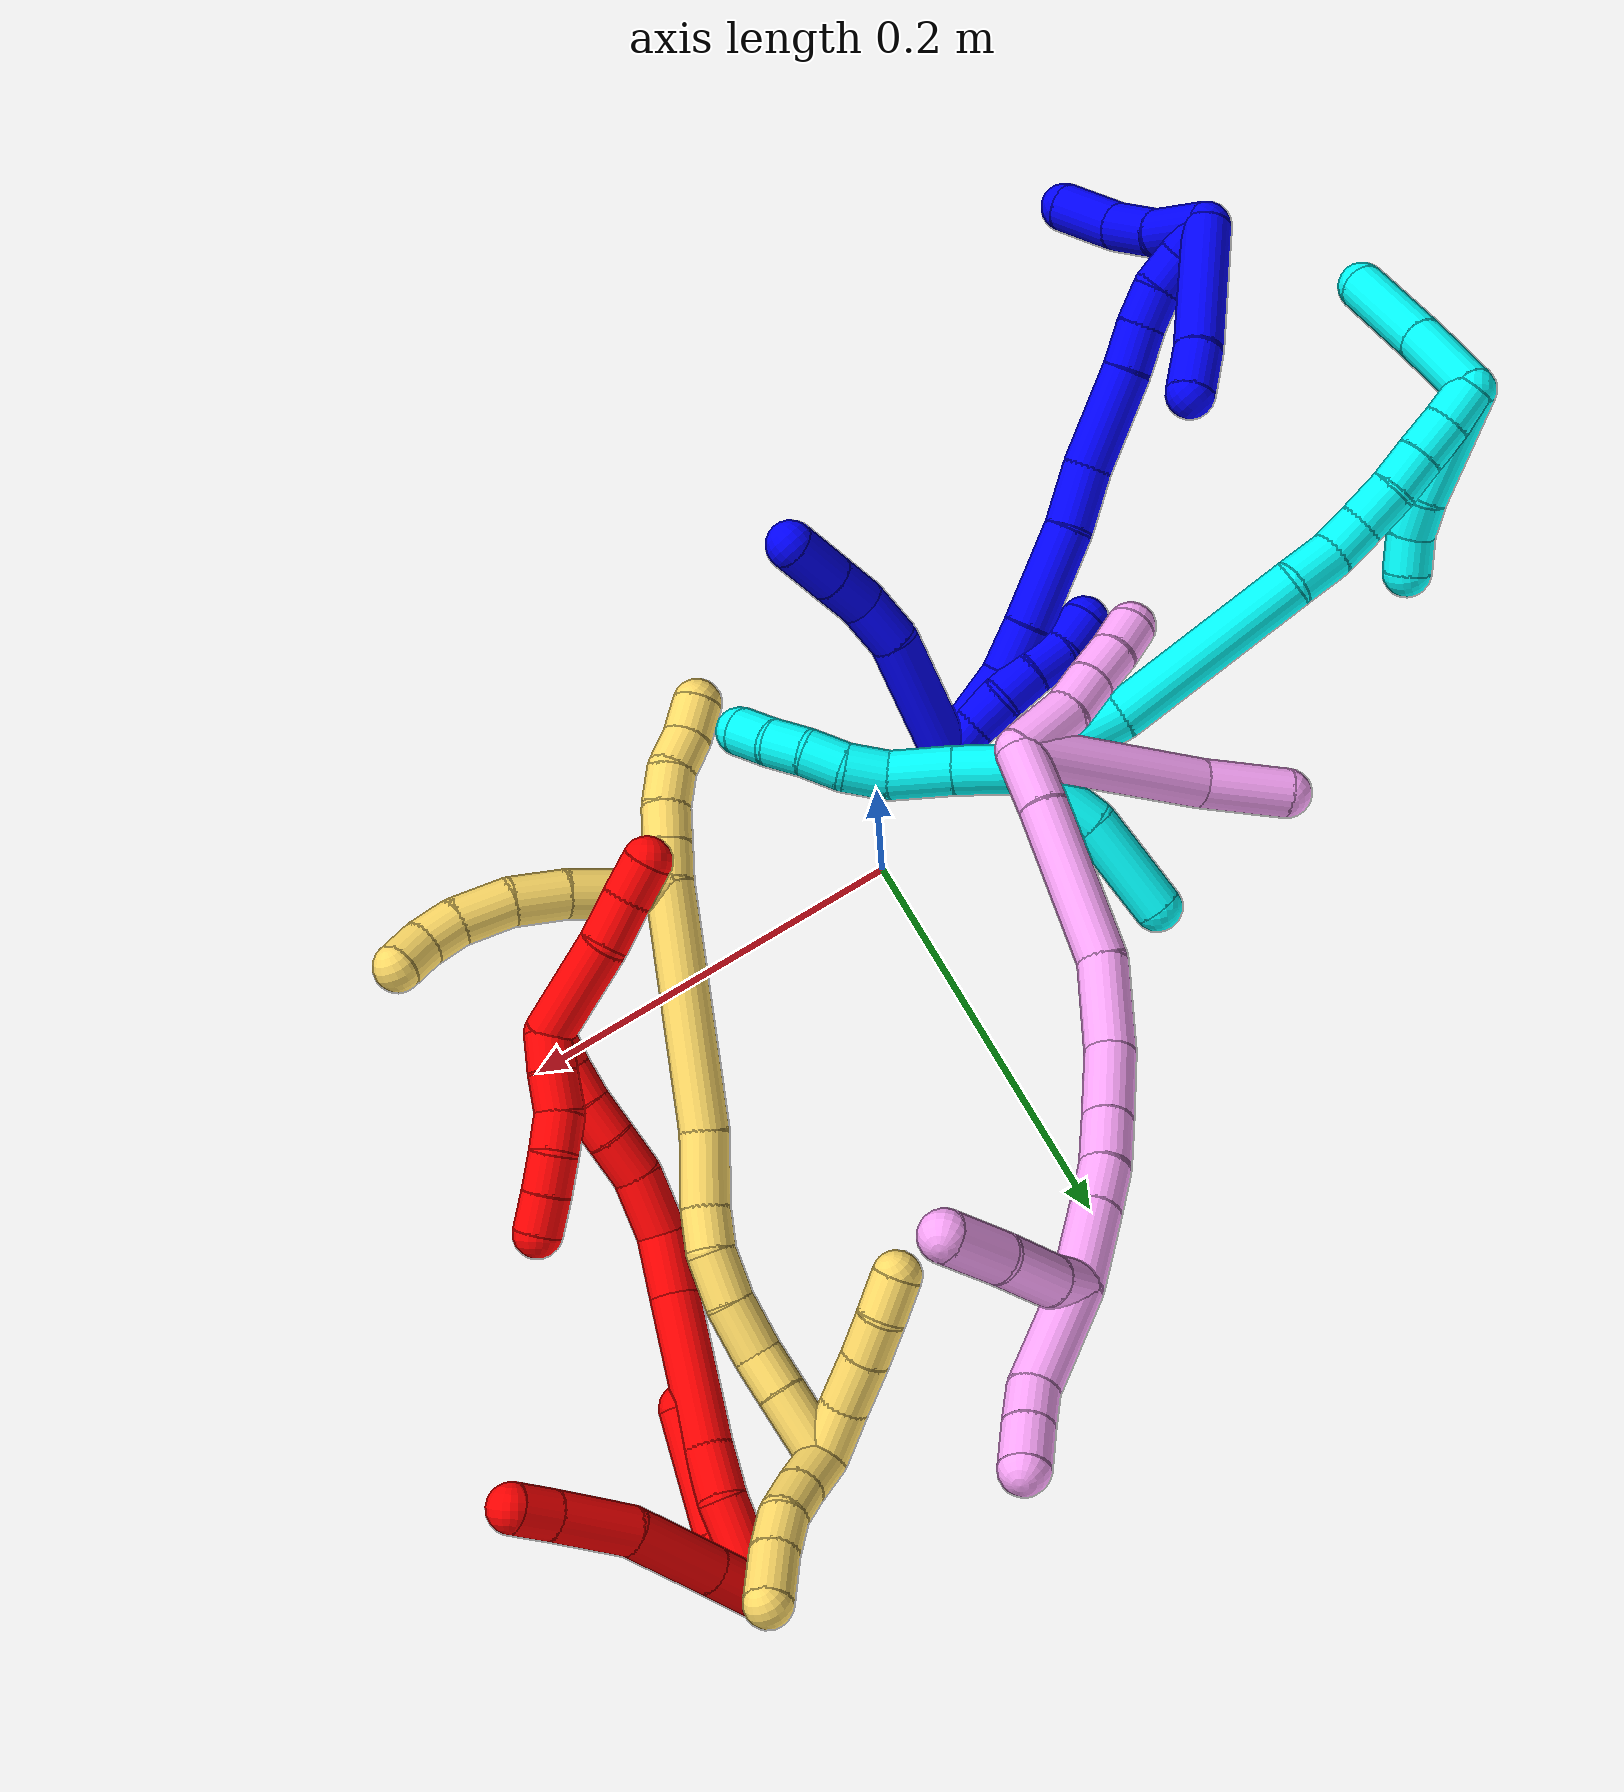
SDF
<sdf version="1.7">
 <world name="default">
  <plugin name="TubeGeneratorPlugin" filename="libtube_generator_plugin.so"/>
  <model name="photoneo_s_sensor">
   <static>1</static>
   <pose>0 0 2 1.57079 1.57079 3.14159</pose>
   <link name="link">
    <inertial><mass>0.1</mass></inertial>
    <sensor name="sensor" type="depth">
     <update_rate>30</update_rate>
     <camera>
      <horizontal_fov>1.22</horizontal_fov>
      <image><width>1920</width><height>1200</height><format>B8G8R8</format></image>
      <clip><near>0.1</near><far>4</far></clip>
      <depth_camera><output>points</output></depth_camera>
     </camera>
     <plugin name="camera_plugin" filename="libgazebo_ros_depth_camera.so">
      <baseline>0.2</baseline>
      <alwaysOn>1</alwaysOn>
      <updateRate>0.0</updateRate>
      <cameraName>camera_ir</cameraName>
      <imageTopicName>/camera/color/image_raw</imageTopicName>
      <cameraInfoTopicName>/camera/color/camera_info</cameraInfoTopicName>
      <depthImageTopicName>/camera/depth/image_raw</depthImageTopicName>
      <depthImageCameraInfoTopicName>/camera/depth/camera_info</depthImageCameraInfoTopicName>
      <pointCloudTopicName>/camera/depth/points</pointCloudTopicName>
      <frameName>fr_optical</frameName>
      <pointCloudCutoff>0.1</pointCloudCutoff>
      <pointCloudCutoffMax>2.0</pointCloudCutoffMax>
      <distortionK1>0</distortionK1>
      <distortionK2>0</distortionK2>
      <distortionK3>0</distortionK3>
      <distortionT1>0</distortionT1>
      <distortionT2>0</distortionT2>
      <CxPrime>0</CxPrime>
      <Cx>0</Cx>
      <Cy>0</Cy>
      <focalLength>0</focalLength>
      <hackBaseline>0</hackBaseline>
     </plugin>
    </sensor>
   </link>
  </model>
  <gravity>0 0 -9.8</gravity>
  <magnetic_field>6e-06 2.3e-05 -4.2e-05</magnetic_field>
  <atmosphere type="adiabatic"/>
  <physics name="default_physics" default="0" type="ode">
   <max_step_size>0.003</max_step_size>
   <real_time_factor>1</real_time_factor>
   <real_time_update_rate>1000</real_time_update_rate>
   <max_contacts>10000</max_contacts>
   <ode>
    <solver>
     <type>quick</type>
     <iters>100</iters>
     <sor>1.3</sor>
     <use_dynamic_moi_rescaling>0</use_dynamic_moi_rescaling>
    </solver>
    <constraints>
     <contact_max_correcting_vel>0</contact_max_correcting_vel>
     <contact_surface_layer>0.001</contact_surface_layer>
     <cfm>0</cfm>
     <erp>0.2</erp>
    </constraints>
   </ode>
  </physics>
  <scene><ambient>0.4 0.4 0.4 1</ambient><background>0.7 0.7 0.7 1</background><shadows>0</shadows></scene>
  <audio><device>default</device></audio>
  <spherical_coordinates>
   <surface_model>EARTH_WGS84</surface_model>
   <latitude_deg>0</latitude_deg>
   <longitude_deg>0</longitude_deg>
   <elevation>0</elevation>
   <heading_deg>0</heading_deg>
  </spherical_coordinates>
  <model name="bin">
   <static>1</static>
   <link name="bottom">
    <collision name="collision-bottom">
     <pose>0 0 -0.01 0 -0 0</pose>
     <geometry><box><size>0.8 0.6 0.02</size></box></geometry>
     <surface>
      <friction><ode><mu>100</mu><mu2>100</mu2></ode></friction>
      <contact><collide_bitmask>65535</collide_bitmask></contact>
     </surface>
    </collision>
   </link>
   <link name="west_wall">
    <collision name="collision-west_wall">
     <pose>-0.41 0 0.1 0 -0 0</pose>
     <geometry><box><size>0.02 0.6 0.2</size></box></geometry>
     <surface>
      <friction><ode><mu>100</mu><mu2>100</mu2></ode></friction>
      <contact><collide_bitmask>65535</collide_bitmask></contact>
     </surface>
    </collision>
   </link>
   <link name="east_wall">
    <collision name="collision-east_wall">
     <pose>0.41 0 0.1 0 -0 0</pose>
     <geometry><box><size>0.02 0.6 0.2</size></box></geometry>
     <surface>
      <friction><ode><mu>100</mu><mu2>100</mu2></ode></friction>
      <contact><collide_bitmask>65535</collide_bitmask></contact>
     </surface>
    </collision>
   </link>
   <link name="south_wall">
    <collision name="collision-south_wall">
     <pose>0 -0.31 0.1 0 -0 0</pose>
     <geometry><box><size>0.8 0.02 0.2</size></box></geometry>
     <surface>
      <friction><ode><mu>100</mu><mu2>100</mu2></ode></friction>
      <contact><collide_bitmask>65535</collide_bitmask></contact>
     </surface>
    </collision>
   </link>
   <link name="north_wall">
    <collision name="collision-north_wall">
     <pose>0 0.31 0.1 0 -0 0</pose>
     <geometry><box><size>0.8 0.02 0.2</size></box></geometry>
     <surface>
      <friction><ode><mu>100</mu><mu2>100</mu2></ode></friction>
      <contact><collide_bitmask>65535</collide_bitmask></contact>
     </surface>
    </collision>
   </link>
  </model>
  <model name="1">
   <static>0</static>
   <link name="1">
    <collision name="collision-cylinder-e_1_2_8">
     <pose>-0.016929 0.003383 0.030576 -0.110182 -0.503087 0.028342</pose>
     <geometry><cylinder><radius>0.0125</radius><length>0.070226</length></cylinder></geometry>
     <surface>
      <friction><ode><mu>1.16</mu><mu2>1.16</mu2><slip1>0</slip1><slip2>0</slip2></ode></friction>
      <contact><ode><kp>1e+06</kp><kd>1</kd><max_vel>0</max_vel><min_depth>0.001</min_depth></ode></contact>
     </surface>
    </collision>
    <visual name="visual-cylinder-e_1_2_8">
     <pose>-0.016929 0.003383 0.030576 -0.110182 -0.503087 0.028342</pose>
     <geometry><cylinder><radius>0.0125</radius><length>0.070226</length></cylinder></geometry>
     <material><ambient>0 0 1 1</ambient></material>
    </visual>
    <collision name="collision-cylinder-e_2_8_9">
     <pose>-0.037752 0.01012 0.073448 -0.266308 -0.296461 0.039998</pose>
     <geometry><cylinder><radius>0.0125</radius><length>0.026655</length></cylinder></geometry>
     <surface>
      <friction><ode><mu>1.16</mu><mu2>1.16</mu2><slip1>0</slip1><slip2>0</slip2></ode></friction>
      <contact><ode><kp>1e+06</kp><kd>1</kd><max_vel>0</max_vel><min_depth>0.001</min_depth></ode></contact>
     </surface>
    </collision>
    <visual name="visual-cylinder-e_2_8_9">
     <pose>-0.037752 0.01012 0.073448 -0.266308 -0.296461 0.039998</pose>
     <geometry><cylinder><radius>0.0125</radius><length>0.026655</length></cylinder></geometry>
     <material><ambient>0 0 1 1</ambient></material>
    </visual>
    <collision name="collision-cylinder-e_3_9_10">
     <pose>-0.045488 0.019197 0.095241 -0.542389 -0.33369 0.093583</pose>
     <geometry><cylinder><radius>0.0125</radius><length>0.023469</length></cylinder></geometry>
     <surface>
      <friction><ode><mu>1.16</mu><mu2>1.16</mu2><slip1>0</slip1><slip2>0</slip2></ode></friction>
      <contact><ode><kp>1e+06</kp><kd>1</kd><max_vel>0</max_vel><min_depth>0.001</min_depth></ode></contact>
     </surface>
    </collision>
    <visual name="visual-cylinder-e_3_9_10">
     <pose>-0.045488 0.019197 0.095241 -0.542389 -0.33369 0.093583</pose>
     <geometry><cylinder><radius>0.0125</radius><length>0.023469</length></cylinder></geometry>
     <material><ambient>0 0 1 1</ambient></material>
    </visual>
    <collision name="collision-cylinder-e_4_10_6">
     <pose>-0.054159 0.032124 0.116761 -0.539784 -0.331678 0.09254</pose>
     <geometry><cylinder><radius>0.0125</radius><length>0.029651</length></cylinder></geometry>
     <surface>
      <friction><ode><mu>1.16</mu><mu2>1.16</mu2><slip1>0</slip1><slip2>0</slip2></ode></friction>
      <contact><ode><kp>1e+06</kp><kd>1</kd><max_vel>0</max_vel><min_depth>0.001</min_depth></ode></contact>
     </surface>
    </collision>
    <visual name="visual-cylinder-e_4_10_6">
     <pose>-0.054159 0.032124 0.116761 -0.539784 -0.331678 0.09254</pose>
     <geometry><cylinder><radius>0.0125</radius><length>0.029651</length></cylinder></geometry>
     <material><ambient>0 0 1 1</ambient></material>
    </visual>
    <collision name="collision-cylinder-e_1_2_11">
     <pose>-0.006022 -0.007878 0.001296 1.4078 -0.646197 -0.553917</pose>
     <geometry><cylinder><radius>0.0125</radius><length>0.02</length></cylinder></geometry>
     <surface>
      <friction><ode><mu>1.16</mu><mu2>1.16</mu2><slip1>0</slip1><slip2>0</slip2></ode></friction>
      <contact><ode><kp>1e+06</kp><kd>1</kd><max_vel>0</max_vel><min_depth>0.001</min_depth></ode></contact>
     </surface>
    </collision>
    <visual name="visual-cylinder-e_1_2_11">
     <pose>-0.006022 -0.007878 0.001296 1.4078 -0.646197 -0.553917</pose>
     <geometry><cylinder><radius>0.0125</radius><length>0.02</length></cylinder></geometry>
     <material><ambient>0 0 1 1</ambient></material>
    </visual>
    <collision name="collision-cylinder-e_2_11_12">
     <pose>-0.019409 -0.022513 0.002871 1.52944 -0.828041 -0.797996</pose>
     <geometry><cylinder><radius>0.0125</radius><length>0.02</length></cylinder></geometry>
     <surface>
      <friction><ode><mu>1.16</mu><mu2>1.16</mu2><slip1>0</slip1><slip2>0</slip2></ode></friction>
      <contact><ode><kp>1e+06</kp><kd>1</kd><max_vel>0</max_vel><min_depth>0.001</min_depth></ode></contact>
     </surface>
    </collision>
    <visual name="visual-cylinder-e_2_11_12">
     <pose>-0.019409 -0.022513 0.002871 1.52944 -0.828041 -0.797996</pose>
     <geometry><cylinder><radius>0.0125</radius><length>0.02</length></cylinder></geometry>
     <material><ambient>0 0 1 1</ambient></material>
    </visual>
    <collision name="collision-cylinder-e_3_12_13">
     <pose>-0.032234 -0.037649 0.003094 1.57758 -0.577449 -0.581162</pose>
     <geometry><cylinder><radius>0.0125</radius><length>0.02</length></cylinder></geometry>
     <surface>
      <friction><ode><mu>1.16</mu><mu2>1.16</mu2><slip1>0</slip1><slip2>0</slip2></ode></friction>
      <contact><ode><kp>1e+06</kp><kd>1</kd><max_vel>0</max_vel><min_depth>0.001</min_depth></ode></contact>
     </surface>
    </collision>
    <visual name="visual-cylinder-e_3_12_13">
     <pose>-0.032234 -0.037649 0.003094 1.57758 -0.577449 -0.581162</pose>
     <geometry><cylinder><radius>0.0125</radius><length>0.02</length></cylinder></geometry>
     <material><ambient>0 0 1 1</ambient></material>
    </visual>
    <collision name="collision-cylinder-e_4_13_14">
     <pose>-0.042366 -0.054818 0.002094 1.67762 -0.486199 -0.538627</pose>
     <geometry><cylinder><radius>0.0125</radius><length>0.02</length></cylinder></geometry>
     <surface>
      <friction><ode><mu>1.16</mu><mu2>1.16</mu2><slip1>0</slip1><slip2>0</slip2></ode></friction>
      <contact><ode><kp>1e+06</kp><kd>1</kd><max_vel>0</max_vel><min_depth>0.001</min_depth></ode></contact>
     </surface>
    </collision>
    <visual name="visual-cylinder-e_4_13_14">
     <pose>-0.042366 -0.054818 0.002094 1.67762 -0.486199 -0.538627</pose>
     <geometry><cylinder><radius>0.0125</radius><length>0.02</length></cylinder></geometry>
     <material><ambient>0 0 1 1</ambient></material>
    </visual>
    <collision name="collision-cylinder-e_5_14_5">
     <pose>-0.050513 -0.072815 0.002937 1.37922 -0.354821 -0.293596</pose>
     <geometry><cylinder><radius>0.0125</radius><length>0.02</length></cylinder></geometry>
     <surface>
      <friction><ode><mu>1.16</mu><mu2>1.16</mu2><slip1>0</slip1><slip2>0</slip2></ode></friction>
      <contact><ode><kp>1e+06</kp><kd>1</kd><max_vel>0</max_vel><min_depth>0.001</min_depth></ode></contact>
     </surface>
    </collision>
    <visual name="visual-cylinder-e_5_14_5">
     <pose>-0.050513 -0.072815 0.002937 1.37922 -0.354821 -0.293596</pose>
     <geometry><cylinder><radius>0.0125</radius><length>0.02</length></cylinder></geometry>
     <material><ambient>0 0 1 1</ambient></material>
    </visual>
    <collision name="collision-cylinder-e_1_2_15">
     <pose>-0.012643 -0.02079 0.005077 1.33128 -0.533608 -0.422801</pose>
     <geometry><cylinder><radius>0.0125</radius><length>0.049712</length></cylinder></geometry>
     <surface>
      <friction><ode><mu>1.16</mu><mu2>1.16</mu2><slip1>0</slip1><slip2>0</slip2></ode></friction>
      <contact><ode><kp>1e+06</kp><kd>1</kd><max_vel>0</max_vel><min_depth>0.001</min_depth></ode></contact>
     </surface>
    </collision>
    <visual name="visual-cylinder-e_1_2_15">
     <pose>-0.012643 -0.02079 0.005077 1.33128 -0.533608 -0.422801</pose>
     <geometry><cylinder><radius>0.0125</radius><length>0.049712</length></cylinder></geometry>
     <material><ambient>0 0 1 1</ambient></material>
    </visual>
    <collision name="collision-cylinder-e_2_15_16">
     <pose>-0.034652 -0.050375 0.015882 0.993596 -0.728547 -0.407691</pose>
     <geometry><cylinder><radius>0.0125</radius><length>0.028136</length></cylinder></geometry>
     <surface>
      <friction><ode><mu>1.16</mu><mu2>1.16</mu2><slip1>0</slip1><slip2>0</slip2></ode></friction>
      <contact><ode><kp>1e+06</kp><kd>1</kd><max_vel>0</max_vel><min_depth>0.001</min_depth></ode></contact>
     </surface>
    </collision>
    <visual name="visual-cylinder-e_2_15_16">
     <pose>-0.034652 -0.050375 0.015882 0.993596 -0.728547 -0.407691</pose>
     <geometry><cylinder><radius>0.0125</radius><length>0.028136</length></cylinder></geometry>
     <material><ambient>0 0 1 1</ambient></material>
    </visual>
    <collision name="collision-cylinder-e_3_16_17">
     <pose>-0.060017 -0.076816 0.033173 0.990664 -0.648843 -0.35946</pose>
     <geometry><cylinder><radius>0.0125</radius><length>0.052951</length></cylinder></geometry>
     <surface>
      <friction><ode><mu>1.16</mu><mu2>1.16</mu2><slip1>0</slip1><slip2>0</slip2></ode></friction>
      <contact><ode><kp>1e+06</kp><kd>1</kd><max_vel>0</max_vel><min_depth>0.001</min_depth></ode></contact>
     </surface>
    </collision>
    <visual name="visual-cylinder-e_3_16_17">
     <pose>-0.060017 -0.076816 0.033173 0.990664 -0.648843 -0.35946</pose>
     <geometry><cylinder><radius>0.0125</radius><length>0.052951</length></cylinder></geometry>
     <material><ambient>0 0 1 1</ambient></material>
    </visual>
    <collision name="collision-cylinder-e_4_17_18">
     <pose>-0.083677 -0.106042 0.0531 0.94534 -0.492257 -0.255515</pose>
     <geometry><cylinder><radius>0.0125</radius><length>0.032423</length></cylinder></geometry>
     <surface>
      <friction><ode><mu>1.16</mu><mu2>1.16</mu2><slip1>0</slip1><slip2>0</slip2></ode></friction>
      <contact><ode><kp>1e+06</kp><kd>1</kd><max_vel>0</max_vel><min_depth>0.001</min_depth></ode></contact>
     </surface>
    </collision>
    <visual name="visual-cylinder-e_4_17_18">
     <pose>-0.083677 -0.106042 0.0531 0.94534 -0.492257 -0.255515</pose>
     <geometry><cylinder><radius>0.0125</radius><length>0.032423</length></cylinder></geometry>
     <material><ambient>0 0 1 1</ambient></material>
    </visual>
    <collision name="collision-cylinder-e_5_18_19">
     <pose>-0.10867 -0.133785 0.073221 0.941862 -0.714399 -0.375553</pose>
     <geometry><cylinder><radius>0.0125</radius><length>0.052908</length></cylinder></geometry>
     <surface>
      <friction><ode><mu>1.16</mu><mu2>1.16</mu2><slip1>0</slip1><slip2>0</slip2></ode></friction>
      <contact><ode><kp>1e+06</kp><kd>1</kd><max_vel>0</max_vel><min_depth>0.001</min_depth></ode></contact>
     </surface>
    </collision>
    <visual name="visual-cylinder-e_5_18_19">
     <pose>-0.10867 -0.133785 0.073221 0.941862 -0.714399 -0.375553</pose>
     <geometry><cylinder><radius>0.0125</radius><length>0.052908</length></cylinder></geometry>
     <material><ambient>0 0 1 1</ambient></material>
    </visual>
    <collision name="collision-cylinder-e_6_19_20">
     <pose>-0.132658 -0.157341 0.090939 0.892343 -0.611292 -0.299605</pose>
     <geometry><cylinder><radius>0.0125</radius><length>0.023196</length></cylinder></geometry>
     <surface>
      <friction><ode><mu>1.16</mu><mu2>1.16</mu2><slip1>0</slip1><slip2>0</slip2></ode></friction>
      <contact><ode><kp>1e+06</kp><kd>1</kd><max_vel>0</max_vel><min_depth>0.001</min_depth></ode></contact>
     </surface>
    </collision>
    <visual name="visual-cylinder-e_6_19_20">
     <pose>-0.132658 -0.157341 0.090939 0.892343 -0.611292 -0.299605</pose>
     <geometry><cylinder><radius>0.0125</radius><length>0.023196</length></cylinder></geometry>
     <material><ambient>0 0 1 1</ambient></material>
    </visual>
    <collision name="collision-cylinder-e_7_20_21">
     <pose>-0.146164 -0.170914 0.10121 0.961716 -0.737841 -0.398062</pose>
     <geometry><cylinder><radius>0.0125</radius><length>0.020364</length></cylinder></geometry>
     <surface>
      <friction><ode><mu>1.16</mu><mu2>1.16</mu2><slip1>0</slip1><slip2>0</slip2></ode></friction>
      <contact><ode><kp>1e+06</kp><kd>1</kd><max_vel>0</max_vel><min_depth>0.001</min_depth></ode></contact>
     </surface>
    </collision>
    <visual name="visual-cylinder-e_7_20_21">
     <pose>-0.146164 -0.170914 0.10121 0.961716 -0.737841 -0.398062</pose>
     <geometry><cylinder><radius>0.0125</radius><length>0.020364</length></cylinder></geometry>
     <material><ambient>0 0 1 1</ambient></material>
    </visual>
    <collision name="collision-cylinder-e_8_21_22">
     <pose>-0.15989 -0.184128 0.107349 1.31644 -0.757665 -0.597197</pose>
     <geometry><cylinder><radius>0.0125</radius><length>0.020011</length></cylinder></geometry>
     <surface>
      <friction><ode><mu>1.16</mu><mu2>1.16</mu2><slip1>0</slip1><slip2>0</slip2></ode></friction>
      <contact><ode><kp>1e+06</kp><kd>1</kd><max_vel>0</max_vel><min_depth>0.001</min_depth></ode></contact>
     </surface>
    </collision>
    <visual name="visual-cylinder-e_8_21_22">
     <pose>-0.15989 -0.184128 0.107349 1.31644 -0.757665 -0.597197</pose>
     <geometry><cylinder><radius>0.0125</radius><length>0.020011</length></cylinder></geometry>
     <material><ambient>0 0 1 1</ambient></material>
    </visual>
    <collision name="collision-cylinder-e_9_22_1">
     <pose>-0.175815 -0.195464 0.110794 1.21142 -1.10095 -0.803839</pose>
     <geometry><cylinder><radius>0.0125</radius><length>0.020299</length></cylinder></geometry>
     <surface>
      <friction><ode><mu>1.16</mu><mu2>1.16</mu2><slip1>0</slip1><slip2>0</slip2></ode></friction>
      <contact><ode><kp>1e+06</kp><kd>1</kd><max_vel>0</max_vel><min_depth>0.001</min_depth></ode></contact>
     </surface>
    </collision>
    <visual name="visual-cylinder-e_9_22_1">
     <pose>-0.175815 -0.195464 0.110794 1.21142 -1.10095 -0.803839</pose>
     <geometry><cylinder><radius>0.0125</radius><length>0.020299</length></cylinder></geometry>
     <material><ambient>0 0 1 1</ambient></material>
    </visual>
    <collision name="collision-cylinder-e_1_1_23">
     <pose>-0.182771 -0.169652 0.090621 -2.19716 0.05627 -0.110087</pose>
     <geometry><cylinder><radius>0.0125</radius><length>0.074459</length></cylinder></geometry>
     <surface>
      <friction><ode><mu>1.16</mu><mu2>1.16</mu2><slip1>0</slip1><slip2>0</slip2></ode></friction>
      <contact><ode><kp>1e+06</kp><kd>1</kd><max_vel>0</max_vel><min_depth>0.001</min_depth></ode></contact>
     </surface>
    </collision>
    <visual name="visual-cylinder-e_1_1_23">
     <pose>-0.182771 -0.169652 0.090621 -2.19716 0.05627 -0.110087</pose>
     <geometry><cylinder><radius>0.0125</radius><length>0.074459</length></cylinder></geometry>
     <material><ambient>0 0 1 1</ambient></material>
    </visual>
    <collision name="collision-cylinder-e_2_23_4">
     <pose>-0.178706 -0.128928 0.062002 -2.14272 0.154961 -0.282707</pose>
     <geometry><cylinder><radius>0.0125</radius><length>0.025541</length></cylinder></geometry>
     <surface>
      <friction><ode><mu>1.16</mu><mu2>1.16</mu2><slip1>0</slip1><slip2>0</slip2></ode></friction>
      <contact><ode><kp>1e+06</kp><kd>1</kd><max_vel>0</max_vel><min_depth>0.001</min_depth></ode></contact>
     </surface>
    </collision>
    <visual name="visual-cylinder-e_2_23_4">
     <pose>-0.178706 -0.128928 0.062002 -2.14272 0.154961 -0.282707</pose>
     <geometry><cylinder><radius>0.0125</radius><length>0.025541</length></cylinder></geometry>
     <material><ambient>0 0 1 1</ambient></material>
    </visual>
    <collision name="collision-cylinder-e_1_1_24">
     <pose>-0.16941 -0.201505 0.119498 0.240618 1.12964 0.152918</pose>
     <geometry><cylinder><radius>0.0125</radius><length>0.034182</length></cylinder></geometry>
     <surface>
      <friction><ode><mu>1.16</mu><mu2>1.16</mu2><slip1>0</slip1><slip2>0</slip2></ode></friction>
      <contact><ode><kp>1e+06</kp><kd>1</kd><max_vel>0</max_vel><min_depth>0.001</min_depth></ode></contact>
     </surface>
    </collision>
    <visual name="visual-cylinder-e_1_1_24">
     <pose>-0.16941 -0.201505 0.119498 0.240618 1.12964 0.152918</pose>
     <geometry><cylinder><radius>0.0125</radius><length>0.034182</length></cylinder></geometry>
     <material><ambient>0 0 1 1</ambient></material>
    </visual>
    <collision name="collision-cylinder-e_2_24_25">
     <pose>-0.141519 -0.207508 0.134961 0.470848 0.923607 0.237643</pose>
     <geometry><cylinder><radius>0.0125</radius><length>0.031176</length></cylinder></geometry>
     <surface>
      <friction><ode><mu>1.16</mu><mu2>1.16</mu2><slip1>0</slip1><slip2>0</slip2></ode></friction>
      <contact><ode><kp>1e+06</kp><kd>1</kd><max_vel>0</max_vel><min_depth>0.001</min_depth></ode></contact>
     </surface>
    </collision>
    <visual name="visual-cylinder-e_2_24_25">
     <pose>-0.141519 -0.207508 0.134961 0.470848 0.923607 0.237643</pose>
     <geometry><cylinder><radius>0.0125</radius><length>0.031176</length></cylinder></geometry>
     <material><ambient>0 0 1 1</ambient></material>
    </visual>
    <collision name="collision-cylinder-e_3_25_3">
     <pose>-0.11787 -0.213992 0.156351 0.168998 0.704118 0.062212</pose>
     <geometry><cylinder><radius>0.0125</radius><length>0.034642</length></cylinder></geometry>
     <surface>
      <friction><ode><mu>1.16</mu><mu2>1.16</mu2><slip1>0</slip1><slip2>0</slip2></ode></friction>
      <contact><ode><kp>1e+06</kp><kd>1</kd><max_vel>0</max_vel><min_depth>0.001</min_depth></ode></contact>
     </surface>
    </collision>
    <visual name="visual-cylinder-e_3_25_3">
     <pose>-0.11787 -0.213992 0.156351 0.168998 0.704118 0.062212</pose>
     <geometry><cylinder><radius>0.0125</radius><length>0.034642</length></cylinder></geometry>
     <material><ambient>0 0 1 1</ambient></material>
    </visual>
    <collision name="collision-sphere-3">
     <pose>-0.106658 -0.216212 0.169364 0 -0 0</pose>
     <geometry><sphere><radius>0.0125</radius></sphere></geometry>
     <surface>
      <friction><ode><mu>1.16</mu><mu2>1.16</mu2><slip1>0</slip1><slip2>0</slip2></ode></friction>
      <contact><ode><kp>1e+06</kp><kd>1</kd><max_vel>0</max_vel><min_depth>0.001</min_depth></ode></contact>
     </surface>
    </collision>
    <visual name="visual-sphere-3">
     <pose>-0.106658 -0.216212 0.169364 0 -0 0</pose>
     <geometry><sphere><radius>0.0125</radius></sphere></geometry>
     <material><ambient>0 0 1 1</ambient></material>
    </visual>
    <collision name="collision-sphere-25">
     <pose>-0.129083 -0.211771 0.143337 0 -0 0</pose>
     <geometry><sphere><radius>0.0125</radius></sphere></geometry>
     <surface>
      <friction><ode><mu>1.16</mu><mu2>1.16</mu2><slip1>0</slip1><slip2>0</slip2></ode></friction>
      <contact><ode><kp>1e+06</kp><kd>1</kd><max_vel>0</max_vel><min_depth>0.001</min_depth></ode></contact>
     </surface>
    </collision>
    <visual name="visual-sphere-25">
     <pose>-0.129083 -0.211771 0.143337 0 -0 0</pose>
     <geometry><sphere><radius>0.0125</radius></sphere></geometry>
     <material><ambient>0 0 1 1</ambient></material>
    </visual>
    <collision name="collision-sphere-24">
     <pose>-0.153955 -0.203244 0.126585 0 -0 0</pose>
     <geometry><sphere><radius>0.0125</radius></sphere></geometry>
     <surface>
      <friction><ode><mu>1.16</mu><mu2>1.16</mu2><slip1>0</slip1><slip2>0</slip2></ode></friction>
      <contact><ode><kp>1e+06</kp><kd>1</kd><max_vel>0</max_vel><min_depth>0.001</min_depth></ode></contact>
     </surface>
    </collision>
    <visual name="visual-sphere-24">
     <pose>-0.153955 -0.203244 0.126585 0 -0 0</pose>
     <geometry><sphere><radius>0.0125</radius></sphere></geometry>
     <material><ambient>0 0 1 1</ambient></material>
    </visual>
    <collision name="collision-sphere-4">
     <pose>-0.176735 -0.118318 0.055173 0 -0 0</pose>
     <geometry><sphere><radius>0.0125</radius></sphere></geometry>
     <surface>
      <friction><ode><mu>1.16</mu><mu2>1.16</mu2><slip1>0</slip1><slip2>0</slip2></ode></friction>
      <contact><ode><kp>1e+06</kp><kd>1</kd><max_vel>0</max_vel><min_depth>0.001</min_depth></ode></contact>
     </surface>
    </collision>
    <visual name="visual-sphere-4">
     <pose>-0.176735 -0.118318 0.055173 0 -0 0</pose>
     <geometry><sphere><radius>0.0125</radius></sphere></geometry>
     <material><ambient>0 0 1 1</ambient></material>
    </visual>
    <collision name="collision-sphere-23">
     <pose>-0.180677 -0.139537 0.068831 0 -0 0</pose>
     <geometry><sphere><radius>0.0125</radius></sphere></geometry>
     <surface>
      <friction><ode><mu>1.16</mu><mu2>1.16</mu2><slip1>0</slip1><slip2>0</slip2></ode></friction>
      <contact><ode><kp>1e+06</kp><kd>1</kd><max_vel>0</max_vel><min_depth>0.001</min_depth></ode></contact>
     </surface>
    </collision>
    <visual name="visual-sphere-23">
     <pose>-0.180677 -0.139537 0.068831 0 -0 0</pose>
     <geometry><sphere><radius>0.0125</radius></sphere></geometry>
     <material><ambient>0 0 1 1</ambient></material>
    </visual>
    <collision name="collision-sphere-1">
     <pose>-0.184865 -0.199766 0.11241 0 -0 0</pose>
     <geometry><sphere><radius>0.0125</radius></sphere></geometry>
     <surface>
      <friction><ode><mu>1.16</mu><mu2>1.16</mu2><slip1>0</slip1><slip2>0</slip2></ode></friction>
      <contact><ode><kp>1e+06</kp><kd>1</kd><max_vel>0</max_vel><min_depth>0.001</min_depth></ode></contact>
     </surface>
    </collision>
    <visual name="visual-sphere-1">
     <pose>-0.184865 -0.199766 0.11241 0 -0 0</pose>
     <geometry><sphere><radius>0.0125</radius></sphere></geometry>
     <material><ambient>0 0 1 1</ambient></material>
    </visual>
    <collision name="collision-sphere-22">
     <pose>-0.166766 -0.191163 0.109178 0 -0 0</pose>
     <geometry><sphere><radius>0.0125</radius></sphere></geometry>
     <surface>
      <friction><ode><mu>1.16</mu><mu2>1.16</mu2><slip1>0</slip1><slip2>0</slip2></ode></friction>
      <contact><ode><kp>1e+06</kp><kd>1</kd><max_vel>0</max_vel><min_depth>0.001</min_depth></ode></contact>
     </surface>
    </collision>
    <visual name="visual-sphere-22">
     <pose>-0.166766 -0.191163 0.109178 0 -0 0</pose>
     <geometry><sphere><radius>0.0125</radius></sphere></geometry>
     <material><ambient>0 0 1 1</ambient></material>
    </visual>
    <collision name="collision-sphere-21">
     <pose>-0.153013 -0.177094 0.10552 0 -0 0</pose>
     <geometry><sphere><radius>0.0125</radius></sphere></geometry>
     <surface>
      <friction><ode><mu>1.16</mu><mu2>1.16</mu2><slip1>0</slip1><slip2>0</slip2></ode></friction>
      <contact><ode><kp>1e+06</kp><kd>1</kd><max_vel>0</max_vel><min_depth>0.001</min_depth></ode></contact>
     </surface>
    </collision>
    <visual name="visual-sphere-21">
     <pose>-0.153013 -0.177094 0.10552 0 -0 0</pose>
     <geometry><sphere><radius>0.0125</radius></sphere></geometry>
     <material><ambient>0 0 1 1</ambient></material>
    </visual>
    <collision name="collision-sphere-11">
     <pose>-0.012043 -0.015756 0.002591 0 -0 0</pose>
     <geometry><sphere><radius>0.0125</radius></sphere></geometry>
     <surface>
      <friction><ode><mu>1.16</mu><mu2>1.16</mu2><slip1>0</slip1><slip2>0</slip2></ode></friction>
      <contact><ode><kp>1e+06</kp><kd>1</kd><max_vel>0</max_vel><min_depth>0.001</min_depth></ode></contact>
     </surface>
    </collision>
    <visual name="visual-sphere-11">
     <pose>-0.012043 -0.015756 0.002591 0 -0 0</pose>
     <geometry><sphere><radius>0.0125</radius></sphere></geometry>
     <material><ambient>0 0 1 1</ambient></material>
    </visual>
    <collision name="collision-sphere-6">
     <pose>-0.058987 0.039328 0.128785 0 -0 0</pose>
     <geometry><sphere><radius>0.0125</radius></sphere></geometry>
     <surface>
      <friction><ode><mu>1.16</mu><mu2>1.16</mu2><slip1>0</slip1><slip2>0</slip2></ode></friction>
      <contact><ode><kp>1e+06</kp><kd>1</kd><max_vel>0</max_vel><min_depth>0.001</min_depth></ode></contact>
     </surface>
    </collision>
    <visual name="visual-sphere-6">
     <pose>-0.058987 0.039328 0.128785 0 -0 0</pose>
     <geometry><sphere><radius>0.0125</radius></sphere></geometry>
     <material><ambient>0 0 1 1</ambient></material>
    </visual>
    <collision name="collision-sphere-10">
     <pose>-0.049332 0.02492 0.104737 0 -0 0</pose>
     <geometry><sphere><radius>0.0125</radius></sphere></geometry>
     <surface>
      <friction><ode><mu>1.16</mu><mu2>1.16</mu2><slip1>0</slip1><slip2>0</slip2></ode></friction>
      <contact><ode><kp>1e+06</kp><kd>1</kd><max_vel>0</max_vel><min_depth>0.001</min_depth></ode></contact>
     </surface>
    </collision>
    <visual name="visual-sphere-10">
     <pose>-0.049332 0.02492 0.104737 0 -0 0</pose>
     <geometry><sphere><radius>0.0125</radius></sphere></geometry>
     <material><ambient>0 0 1 1</ambient></material>
    </visual>
    <collision name="collision-sphere-9">
     <pose>-0.041645 0.013474 0.085745 0 -0 0</pose>
     <geometry><sphere><radius>0.0125</radius></sphere></geometry>
     <surface>
      <friction><ode><mu>1.16</mu><mu2>1.16</mu2><slip1>0</slip1><slip2>0</slip2></ode></friction>
      <contact><ode><kp>1e+06</kp><kd>1</kd><max_vel>0</max_vel><min_depth>0.001</min_depth></ode></contact>
     </surface>
    </collision>
    <visual name="visual-sphere-9">
     <pose>-0.041645 0.013474 0.085745 0 -0 0</pose>
     <geometry><sphere><radius>0.0125</radius></sphere></geometry>
     <material><ambient>0 0 1 1</ambient></material>
    </visual>
    <collision name="collision-sphere-2">
     <geometry><sphere><radius>0.0125</radius></sphere></geometry>
     <surface>
      <friction><ode><mu>1.16</mu><mu2>1.16</mu2><slip1>0</slip1><slip2>0</slip2></ode></friction>
      <contact><ode><kp>1e+06</kp><kd>1</kd><max_vel>0</max_vel><min_depth>0.001</min_depth></ode></contact>
     </surface>
    </collision>
    <visual name="visual-sphere-2">
     <geometry><sphere><radius>0.0125</radius></sphere></geometry>
     <material><ambient>0 0 1 1</ambient></material>
    </visual>
    <collision name="collision-sphere-19">
     <pose>-0.126002 -0.149947 0.084979 0 -0 0</pose>
     <geometry><sphere><radius>0.0125</radius></sphere></geometry>
     <surface>
      <friction><ode><mu>1.16</mu><mu2>1.16</mu2><slip1>0</slip1><slip2>0</slip2></ode></friction>
      <contact><ode><kp>1e+06</kp><kd>1</kd><max_vel>0</max_vel><min_depth>0.001</min_depth></ode></contact>
     </surface>
    </collision>
    <visual name="visual-sphere-19">
     <pose>-0.126002 -0.149947 0.084979 0 -0 0</pose>
     <geometry><sphere><radius>0.0125</radius></sphere></geometry>
     <material><ambient>0 0 1 1</ambient></material>
    </visual>
    <collision name="collision-sphere-8">
     <pose>-0.033858 0.006765 0.061152 0 -0 0</pose>
     <geometry><sphere><radius>0.0125</radius></sphere></geometry>
     <surface>
      <friction><ode><mu>1.16</mu><mu2>1.16</mu2><slip1>0</slip1><slip2>0</slip2></ode></friction>
      <contact><ode><kp>1e+06</kp><kd>1</kd><max_vel>0</max_vel><min_depth>0.001</min_depth></ode></contact>
     </surface>
    </collision>
    <visual name="visual-sphere-8">
     <pose>-0.033858 0.006765 0.061152 0 -0 0</pose>
     <geometry><sphere><radius>0.0125</radius></sphere></geometry>
     <material><ambient>0 0 1 1</ambient></material>
    </visual>
    <collision name="collision-sphere-12">
     <pose>-0.026775 -0.029271 0.00315 0 -0 0</pose>
     <geometry><sphere><radius>0.0125</radius></sphere></geometry>
     <surface>
      <friction><ode><mu>1.16</mu><mu2>1.16</mu2><slip1>0</slip1><slip2>0</slip2></ode></friction>
      <contact><ode><kp>1e+06</kp><kd>1</kd><max_vel>0</max_vel><min_depth>0.001</min_depth></ode></contact>
     </surface>
    </collision>
    <visual name="visual-sphere-12">
     <pose>-0.026775 -0.029271 0.00315 0 -0 0</pose>
     <geometry><sphere><radius>0.0125</radius></sphere></geometry>
     <material><ambient>0 0 1 1</ambient></material>
    </visual>
    <collision name="collision-sphere-13">
     <pose>-0.037693 -0.046028 0.003037 0 -0 0</pose>
     <geometry><sphere><radius>0.0125</radius></sphere></geometry>
     <surface>
      <friction><ode><mu>1.16</mu><mu2>1.16</mu2><slip1>0</slip1><slip2>0</slip2></ode></friction>
      <contact><ode><kp>1e+06</kp><kd>1</kd><max_vel>0</max_vel><min_depth>0.001</min_depth></ode></contact>
     </surface>
    </collision>
    <visual name="visual-sphere-13">
     <pose>-0.037693 -0.046028 0.003037 0 -0 0</pose>
     <geometry><sphere><radius>0.0125</radius></sphere></geometry>
     <material><ambient>0 0 1 1</ambient></material>
    </visual>
    <collision name="collision-sphere-14">
     <pose>-0.047038 -0.063609 0.001152 0 -0 0</pose>
     <geometry><sphere><radius>0.0125</radius></sphere></geometry>
     <surface>
      <friction><ode><mu>1.16</mu><mu2>1.16</mu2><slip1>0</slip1><slip2>0</slip2></ode></friction>
      <contact><ode><kp>1e+06</kp><kd>1</kd><max_vel>0</max_vel><min_depth>0.001</min_depth></ode></contact>
     </surface>
    </collision>
    <visual name="visual-sphere-14">
     <pose>-0.047038 -0.063609 0.001152 0 -0 0</pose>
     <geometry><sphere><radius>0.0125</radius></sphere></geometry>
     <material><ambient>0 0 1 1</ambient></material>
    </visual>
    <collision name="collision-sphere-5">
     <pose>-0.053987 -0.08202 0.004722 0 -0 0</pose>
     <geometry><sphere><radius>0.0125</radius></sphere></geometry>
     <surface>
      <friction><ode><mu>1.16</mu><mu2>1.16</mu2><slip1>0</slip1><slip2>0</slip2></ode></friction>
      <contact><ode><kp>1e+06</kp><kd>1</kd><max_vel>0</max_vel><min_depth>0.001</min_depth></ode></contact>
     </surface>
    </collision>
    <visual name="visual-sphere-5">
     <pose>-0.053987 -0.08202 0.004722 0 -0 0</pose>
     <geometry><sphere><radius>0.0125</radius></sphere></geometry>
     <material><ambient>0 0 1 1</ambient></material>
    </visual>
    <collision name="collision-sphere-15">
     <pose>-0.025286 -0.041579 0.010154 0 -0 0</pose>
     <geometry><sphere><radius>0.0125</radius></sphere></geometry>
     <surface>
      <friction><ode><mu>1.16</mu><mu2>1.16</mu2><slip1>0</slip1><slip2>0</slip2></ode></friction>
      <contact><ode><kp>1e+06</kp><kd>1</kd><max_vel>0</max_vel><min_depth>0.001</min_depth></ode></contact>
     </surface>
    </collision>
    <visual name="visual-sphere-15">
     <pose>-0.025286 -0.041579 0.010154 0 -0 0</pose>
     <geometry><sphere><radius>0.0125</radius></sphere></geometry>
     <material><ambient>0 0 1 1</ambient></material>
    </visual>
    <collision name="collision-sphere-16">
     <pose>-0.044018 -0.059172 0.021609 0 -0 0</pose>
     <geometry><sphere><radius>0.0125</radius></sphere></geometry>
     <surface>
      <friction><ode><mu>1.16</mu><mu2>1.16</mu2><slip1>0</slip1><slip2>0</slip2></ode></friction>
      <contact><ode><kp>1e+06</kp><kd>1</kd><max_vel>0</max_vel><min_depth>0.001</min_depth></ode></contact>
     </surface>
    </collision>
    <visual name="visual-sphere-16">
     <pose>-0.044018 -0.059172 0.021609 0 -0 0</pose>
     <geometry><sphere><radius>0.0125</radius></sphere></geometry>
     <material><ambient>0 0 1 1</ambient></material>
    </visual>
    <collision name="collision-sphere-17">
     <pose>-0.076015 -0.09446 0.044736 0 -0 0</pose>
     <geometry><sphere><radius>0.0125</radius></sphere></geometry>
     <surface>
      <friction><ode><mu>1.16</mu><mu2>1.16</mu2><slip1>0</slip1><slip2>0</slip2></ode></friction>
      <contact><ode><kp>1e+06</kp><kd>1</kd><max_vel>0</max_vel><min_depth>0.001</min_depth></ode></contact>
     </surface>
    </collision>
    <visual name="visual-sphere-17">
     <pose>-0.076015 -0.09446 0.044736 0 -0 0</pose>
     <geometry><sphere><radius>0.0125</radius></sphere></geometry>
     <material><ambient>0 0 1 1</ambient></material>
    </visual>
    <collision name="collision-sphere-18">
     <pose>-0.091339 -0.117624 0.061464 0 -0 0</pose>
     <geometry><sphere><radius>0.0125</radius></sphere></geometry>
     <surface>
      <friction><ode><mu>1.16</mu><mu2>1.16</mu2><slip1>0</slip1><slip2>0</slip2></ode></friction>
      <contact><ode><kp>1e+06</kp><kd>1</kd><max_vel>0</max_vel><min_depth>0.001</min_depth></ode></contact>
     </surface>
    </collision>
    <visual name="visual-sphere-18">
     <pose>-0.091339 -0.117624 0.061464 0 -0 0</pose>
     <geometry><sphere><radius>0.0125</radius></sphere></geometry>
     <material><ambient>0 0 1 1</ambient></material>
    </visual>
    <collision name="collision-sphere-20">
     <pose>-0.139314 -0.164735 0.0969 0 -0 0</pose>
     <geometry><sphere><radius>0.0125</radius></sphere></geometry>
     <surface>
      <friction><ode><mu>1.16</mu><mu2>1.16</mu2><slip1>0</slip1><slip2>0</slip2></ode></friction>
      <contact><ode><kp>1e+06</kp><kd>1</kd><max_vel>0</max_vel><min_depth>0.001</min_depth></ode></contact>
     </surface>
    </collision>
    <visual name="visual-sphere-20">
     <pose>-0.139314 -0.164735 0.0969 0 -0 0</pose>
     <geometry><sphere><radius>0.0125</radius></sphere></geometry>
     <material><ambient>0 0 1 1</ambient></material>
    </visual>
    <inertial>
     <pose>-0.08854 -0.094021 0.064942 0 -0 0</pose>
     <mass>0.75</mass>
     <inertia><ixx>8.9e-05</ixx><ixy>0</ixy><ixz>0</ixz><iyy>3.1e-05</iyy><iyz>0</iyz><izz>6.8e-05</izz></inertia>
    </inertial>
   </link>
   <pose>-0.056778 -0.031767 0.012914 1.25023 0.95078 -0.065929</pose>
  </model>
  <model name="2">
   <static>0</static>
   <link name="2">
    <collision name="collision-cylinder-e_1_2_8">
     <pose>-0.014411 -0.000544 -0.006386 3.05669 -1.15233 -3.01101</pose>
     <geometry><cylinder><radius>0.0125</radius><length>0.031545</length></cylinder></geometry>
     <surface>
      <friction><ode><mu>1.16</mu><mu2>1.16</mu2><slip1>0</slip1><slip2>0</slip2></ode></friction>
      <contact><ode><kp>1e+06</kp><kd>1</kd><max_vel>0</max_vel><min_depth>0.001</min_depth></ode></contact>
     </surface>
    </collision>
    <visual name="visual-cylinder-e_1_2_8">
     <pose>-0.014411 -0.000544 -0.006386 3.05669 -1.15233 -3.01101</pose>
     <geometry><cylinder><radius>0.0125</radius><length>0.031545</length></cylinder></geometry>
     <material><ambient>1 0 0 1</ambient></material>
    </visual>
    <collision name="collision-cylinder-e_2_8_9">
     <pose>-0.052852 -0.000941 -0.023039 -3.12734 -1.16698 3.12</pose>
     <geometry><cylinder><radius>0.0125</radius><length>0.052262</length></cylinder></geometry>
     <surface>
      <friction><ode><mu>1.16</mu><mu2>1.16</mu2><slip1>0</slip1><slip2>0</slip2></ode></friction>
      <contact><ode><kp>1e+06</kp><kd>1</kd><max_vel>0</max_vel><min_depth>0.001</min_depth></ode></contact>
     </surface>
    </collision>
    <visual name="visual-cylinder-e_2_8_9">
     <pose>-0.052852 -0.000941 -0.023039 -3.12734 -1.16698 3.12</pose>
     <geometry><cylinder><radius>0.0125</radius><length>0.052262</length></cylinder></geometry>
     <material><ambient>1 0 0 1</ambient></material>
    </visual>
    <collision name="collision-cylinder-e_3_9_10">
     <pose>-0.098565 -0.00237 -0.037583 2.78859 -1.36362 -2.70899</pose>
     <geometry><cylinder><radius>0.0125</radius><length>0.044315</length></cylinder></geometry>
     <surface>
      <friction><ode><mu>1.16</mu><mu2>1.16</mu2><slip1>0</slip1><slip2>0</slip2></ode></friction>
      <contact><ode><kp>1e+06</kp><kd>1</kd><max_vel>0</max_vel><min_depth>0.001</min_depth></ode></contact>
     </surface>
    </collision>
    <visual name="visual-cylinder-e_3_9_10">
     <pose>-0.098565 -0.00237 -0.037583 2.78859 -1.36362 -2.70899</pose>
     <geometry><cylinder><radius>0.0125</radius><length>0.044315</length></cylinder></geometry>
     <material><ambient>1 0 0 1</ambient></material>
    </visual>
    <collision name="collision-cylinder-e_4_10_6">
     <pose>-0.131007 -0.004439 -0.043776 2.88958 -1.38884 -2.83969</pose>
     <geometry><cylinder><radius>0.0125</radius><length>0.021878</length></cylinder></geometry>
     <surface>
      <friction><ode><mu>1.16</mu><mu2>1.16</mu2><slip1>0</slip1><slip2>0</slip2></ode></friction>
      <contact><ode><kp>1e+06</kp><kd>1</kd><max_vel>0</max_vel><min_depth>0.001</min_depth></ode></contact>
     </surface>
    </collision>
    <visual name="visual-cylinder-e_4_10_6">
     <pose>-0.131007 -0.004439 -0.043776 2.88958 -1.38884 -2.83969</pose>
     <geometry><cylinder><radius>0.0125</radius><length>0.021878</length></cylinder></geometry>
     <material><ambient>1 0 0 1</ambient></material>
    </visual>
    <collision name="collision-cylinder-e_1_2_11">
     <pose>-0.004642 -0.011344 -0.013505 2.44295 -0.257365 -0.682663</pose>
     <geometry><cylinder><radius>0.0125</radius><length>0.036477</length></cylinder></geometry>
     <surface>
      <friction><ode><mu>1.16</mu><mu2>1.16</mu2><slip1>0</slip1><slip2>0</slip2></ode></friction>
      <contact><ode><kp>1e+06</kp><kd>1</kd><max_vel>0</max_vel><min_depth>0.001</min_depth></ode></contact>
     </surface>
    </collision>
    <visual name="visual-cylinder-e_1_2_11">
     <pose>-0.004642 -0.011344 -0.013505 2.44295 -0.257365 -0.682663</pose>
     <geometry><cylinder><radius>0.0125</radius><length>0.036477</length></cylinder></geometry>
     <material><ambient>1 0 0 1</ambient></material>
    </visual>
    <collision name="collision-cylinder-e_2_11_5">
     <pose>-0.012799 -0.034969 -0.056091 2.74199 -0.110886 -0.535001</pose>
     <geometry><cylinder><radius>0.0125</radius><length>0.063523</length></cylinder></geometry>
     <surface>
      <friction><ode><mu>1.16</mu><mu2>1.16</mu2><slip1>0</slip1><slip2>0</slip2></ode></friction>
      <contact><ode><kp>1e+06</kp><kd>1</kd><max_vel>0</max_vel><min_depth>0.001</min_depth></ode></contact>
     </surface>
    </collision>
    <visual name="visual-cylinder-e_2_11_5">
     <pose>-0.012799 -0.034969 -0.056091 2.74199 -0.110886 -0.535001</pose>
     <geometry><cylinder><radius>0.0125</radius><length>0.063523</length></cylinder></geometry>
     <material><ambient>1 0 0 1</ambient></material>
    </visual>
    <collision name="collision-cylinder-e_1_2_12">
     <pose>-0.006137 -0.008557 -0.022023 2.77101 -0.254134 -1.19649</pose>
     <geometry><cylinder><radius>0.0125</radius><length>0.048823</length></cylinder></geometry>
     <surface>
      <friction><ode><mu>1.16</mu><mu2>1.16</mu2><slip1>0</slip1><slip2>0</slip2></ode></friction>
      <contact><ode><kp>1e+06</kp><kd>1</kd><max_vel>0</max_vel><min_depth>0.001</min_depth></ode></contact>
     </surface>
    </collision>
    <visual name="visual-cylinder-e_1_2_12">
     <pose>-0.006137 -0.008557 -0.022023 2.77101 -0.254134 -1.19649</pose>
     <geometry><cylinder><radius>0.0125</radius><length>0.048823</length></cylinder></geometry>
     <material><ambient>1 0 0 1</ambient></material>
    </visual>
    <collision name="collision-cylinder-e_2_12_13">
     <pose>-0.012532 -0.023687 -0.05581 2.63204 -0.019088 -0.073262</pose>
     <geometry><cylinder><radius>0.0125</radius><length>0.026956</length></cylinder></geometry>
     <surface>
      <friction><ode><mu>1.16</mu><mu2>1.16</mu2><slip1>0</slip1><slip2>0</slip2></ode></friction>
      <contact><ode><kp>1e+06</kp><kd>1</kd><max_vel>0</max_vel><min_depth>0.001</min_depth></ode></contact>
     </surface>
    </collision>
    <visual name="visual-cylinder-e_2_12_13">
     <pose>-0.012532 -0.023687 -0.05581 2.63204 -0.019088 -0.073262</pose>
     <geometry><cylinder><radius>0.0125</radius><length>0.026956</length></cylinder></geometry>
     <material><ambient>1 0 0 1</ambient></material>
    </visual>
    <collision name="collision-cylinder-e_3_13_14">
     <pose>-0.01464 -0.044846 -0.103419 2.75515 -0.047795 -0.24311</pose>
     <geometry><cylinder><radius>0.0125</radius><length>0.077487</length></cylinder></geometry>
     <surface>
      <friction><ode><mu>1.16</mu><mu2>1.16</mu2><slip1>0</slip1><slip2>0</slip2></ode></friction>
      <contact><ode><kp>1e+06</kp><kd>1</kd><max_vel>0</max_vel><min_depth>0.001</min_depth></ode></contact>
     </surface>
    </collision>
    <visual name="visual-cylinder-e_3_13_14">
     <pose>-0.01464 -0.044846 -0.103419 2.75515 -0.047795 -0.24311</pose>
     <geometry><cylinder><radius>0.0125</radius><length>0.077487</length></cylinder></geometry>
     <material><ambient>1 0 0 1</ambient></material>
    </visual>
    <collision name="collision-cylinder-e_4_14_15">
     <pose>-0.018309 -0.06381 -0.154306 2.85834 -0.115544 -0.77071</pose>
     <geometry><cylinder><radius>0.0125</radius><length>0.031543</length></cylinder></geometry>
     <surface>
      <friction><ode><mu>1.16</mu><mu2>1.16</mu2><slip1>0</slip1><slip2>0</slip2></ode></friction>
      <contact><ode><kp>1e+06</kp><kd>1</kd><max_vel>0</max_vel><min_depth>0.001</min_depth></ode></contact>
     </surface>
    </collision>
    <visual name="visual-cylinder-e_4_14_15">
     <pose>-0.018309 -0.06381 -0.154306 2.85834 -0.115544 -0.77071</pose>
     <geometry><cylinder><radius>0.0125</radius><length>0.031543</length></cylinder></geometry>
     <material><ambient>1 0 0 1</ambient></material>
    </visual>
    <collision name="collision-cylinder-e_5_15_16">
     <pose>-0.026651 -0.070634 -0.183631 2.972 -0.423038 -2.38775</pose>
     <geometry><cylinder><radius>0.0125</radius><length>0.031782</length></cylinder></geometry>
     <surface>
      <friction><ode><mu>1.16</mu><mu2>1.16</mu2><slip1>0</slip1><slip2>0</slip2></ode></friction>
      <contact><ode><kp>1e+06</kp><kd>1</kd><max_vel>0</max_vel><min_depth>0.001</min_depth></ode></contact>
     </surface>
    </collision>
    <visual name="visual-cylinder-e_5_15_16">
     <pose>-0.026651 -0.070634 -0.183631 2.972 -0.423038 -2.38775</pose>
     <geometry><cylinder><radius>0.0125</radius><length>0.031782</length></cylinder></geometry>
     <material><ambient>1 0 0 1</ambient></material>
    </visual>
    <collision name="collision-cylinder-e_6_16_17">
     <pose>-0.040154 -0.075342 -0.206818 2.8928 -0.649615 -2.43047</pose>
     <geometry><cylinder><radius>0.0125</radius><length>0.023077</length></cylinder></geometry>
     <surface>
      <friction><ode><mu>1.16</mu><mu2>1.16</mu2><slip1>0</slip1><slip2>0</slip2></ode></friction>
      <contact><ode><kp>1e+06</kp><kd>1</kd><max_vel>0</max_vel><min_depth>0.001</min_depth></ode></contact>
     </surface>
    </collision>
    <visual name="visual-cylinder-e_6_16_17">
     <pose>-0.040154 -0.075342 -0.206818 2.8928 -0.649615 -2.43047</pose>
     <geometry><cylinder><radius>0.0125</radius><length>0.023077</length></cylinder></geometry>
     <material><ambient>1 0 0 1</ambient></material>
    </visual>
    <collision name="collision-cylinder-e_7_17_18">
     <pose>-0.05281 -0.08039 -0.223599 2.80168 -0.596853 -2.12385</pose>
     <geometry><cylinder><radius>0.0125</radius><length>0.020197</length></cylinder></geometry>
     <surface>
      <friction><ode><mu>1.16</mu><mu2>1.16</mu2><slip1>0</slip1><slip2>0</slip2></ode></friction>
      <contact><ode><kp>1e+06</kp><kd>1</kd><max_vel>0</max_vel><min_depth>0.001</min_depth></ode></contact>
     </surface>
    </collision>
    <visual name="visual-cylinder-e_7_17_18">
     <pose>-0.05281 -0.08039 -0.223599 2.80168 -0.596853 -2.12385</pose>
     <geometry><cylinder><radius>0.0125</radius><length>0.020197</length></cylinder></geometry>
     <material><ambient>1 0 0 1</ambient></material>
    </visual>
    <collision name="collision-cylinder-e_8_18_19">
     <pose>-0.062914 -0.086432 -0.239873 2.7716 -0.456904 -1.78621</pose>
     <geometry><cylinder><radius>0.0125</radius><length>0.020078</length></cylinder></geometry>
     <surface>
      <friction><ode><mu>1.16</mu><mu2>1.16</mu2><slip1>0</slip1><slip2>0</slip2></ode></friction>
      <contact><ode><kp>1e+06</kp><kd>1</kd><max_vel>0</max_vel><min_depth>0.001</min_depth></ode></contact>
     </surface>
    </collision>
    <visual name="visual-cylinder-e_8_18_19">
     <pose>-0.062914 -0.086432 -0.239873 2.7716 -0.456904 -1.78621</pose>
     <geometry><cylinder><radius>0.0125</radius><length>0.020078</length></cylinder></geometry>
     <material><ambient>1 0 0 1</ambient></material>
    </visual>
    <collision name="collision-cylinder-e_9_19_1">
     <pose>-0.07231 -0.090454 -0.256951 3.05378 -0.518155 -2.81303</pose>
     <geometry><cylinder><radius>0.0125</radius><length>0.020057</length></cylinder></geometry>
     <surface>
      <friction><ode><mu>1.16</mu><mu2>1.16</mu2><slip1>0</slip1><slip2>0</slip2></ode></friction>
      <contact><ode><kp>1e+06</kp><kd>1</kd><max_vel>0</max_vel><min_depth>0.001</min_depth></ode></contact>
     </surface>
    </collision>
    <visual name="visual-cylinder-e_9_19_1">
     <pose>-0.07231 -0.090454 -0.256951 3.05378 -0.518155 -2.81303</pose>
     <geometry><cylinder><radius>0.0125</radius><length>0.020057</length></cylinder></geometry>
     <material><ambient>1 0 0 1</ambient></material>
    </visual>
    <collision name="collision-cylinder-e_1_1_20">
     <pose>-0.072076 -0.077001 -0.287924 -2.5739 0.194242 -0.644656</pose>
     <geometry><cylinder><radius>0.0125</radius><length>0.053896</length></cylinder></geometry>
     <surface>
      <friction><ode><mu>1.16</mu><mu2>1.16</mu2><slip1>0</slip1><slip2>0</slip2></ode></friction>
      <contact><ode><kp>1e+06</kp><kd>1</kd><max_vel>0</max_vel><min_depth>0.001</min_depth></ode></contact>
     </surface>
    </collision>
    <visual name="visual-cylinder-e_1_1_20">
     <pose>-0.072076 -0.077001 -0.287924 -2.5739 0.194242 -0.644656</pose>
     <geometry><cylinder><radius>0.0125</radius><length>0.053896</length></cylinder></geometry>
     <material><ambient>1 0 0 1</ambient></material>
    </visual>
    <collision name="collision-cylinder-e_2_20_21">
     <pose>-0.06313 -0.059345 -0.321572 -2.84749 0.305713 -1.61008</pose>
     <geometry><cylinder><radius>0.0125</radius><length>0.024881</length></cylinder></geometry>
     <surface>
      <friction><ode><mu>1.16</mu><mu2>1.16</mu2><slip1>0</slip1><slip2>0</slip2></ode></friction>
      <contact><ode><kp>1e+06</kp><kd>1</kd><max_vel>0</max_vel><min_depth>0.001</min_depth></ode></contact>
     </surface>
    </collision>
    <visual name="visual-cylinder-e_2_20_21">
     <pose>-0.06313 -0.059345 -0.321572 -2.84749 0.305713 -1.61008</pose>
     <geometry><cylinder><radius>0.0125</radius><length>0.024881</length></cylinder></geometry>
     <material><ambient>1 0 0 1</ambient></material>
    </visual>
    <collision name="collision-cylinder-e_3_21_4">
     <pose>-0.056928 -0.051567 -0.342293 -2.70776 0.23376 -0.979041</pose>
     <geometry><cylinder><radius>0.0125</radius><length>0.021223</length></cylinder></geometry>
     <surface>
      <friction><ode><mu>1.16</mu><mu2>1.16</mu2><slip1>0</slip1><slip2>0</slip2></ode></friction>
      <contact><ode><kp>1e+06</kp><kd>1</kd><max_vel>0</max_vel><min_depth>0.001</min_depth></ode></contact>
     </surface>
    </collision>
    <visual name="visual-cylinder-e_3_21_4">
     <pose>-0.056928 -0.051567 -0.342293 -2.70776 0.23376 -0.979041</pose>
     <geometry><cylinder><radius>0.0125</radius><length>0.021223</length></cylinder></geometry>
     <material><ambient>1 0 0 1</ambient></material>
    </visual>
    <collision name="collision-cylinder-e_1_1_22">
     <pose>-0.077309 -0.088554 -0.255991 -0.269713 -0.003125 0.000424</pose>
     <geometry><cylinder><radius>0.0125</radius><length>0.02</length></cylinder></geometry>
     <surface>
      <friction><ode><mu>1.16</mu><mu2>1.16</mu2><slip1>0</slip1><slip2>0</slip2></ode></friction>
      <contact><ode><kp>1e+06</kp><kd>1</kd><max_vel>0</max_vel><min_depth>0.001</min_depth></ode></contact>
     </surface>
    </collision>
    <visual name="visual-cylinder-e_1_1_22">
     <pose>-0.077309 -0.088554 -0.255991 -0.269713 -0.003125 0.000424</pose>
     <geometry><cylinder><radius>0.0125</radius><length>0.02</length></cylinder></geometry>
     <material><ambient>1 0 0 1</ambient></material>
    </visual>
    <collision name="collision-cylinder-e_2_22_23">
     <pose>-0.076269 -0.083603 -0.236677 -0.232043 0.107273 -0.012514</pose>
     <geometry><cylinder><radius>0.0125</radius><length>0.02</length></cylinder></geometry>
     <surface>
      <friction><ode><mu>1.16</mu><mu2>1.16</mu2><slip1>0</slip1><slip2>0</slip2></ode></friction>
      <contact><ode><kp>1e+06</kp><kd>1</kd><max_vel>0</max_vel><min_depth>0.001</min_depth></ode></contact>
     </surface>
    </collision>
    <visual name="visual-cylinder-e_2_22_23">
     <pose>-0.076269 -0.083603 -0.236677 -0.232043 0.107273 -0.012514</pose>
     <geometry><cylinder><radius>0.0125</radius><length>0.02</length></cylinder></geometry>
     <material><ambient>1 0 0 1</ambient></material>
    </visual>
    <collision name="collision-cylinder-e_3_23_24">
     <pose>-0.077007 -0.080272 -0.217221 -0.106373 -0.181877 0.009709</pose>
     <geometry><cylinder><radius>0.0125</radius><length>0.02</length></cylinder></geometry>
     <surface>
      <friction><ode><mu>1.16</mu><mu2>1.16</mu2><slip1>0</slip1><slip2>0</slip2></ode></friction>
      <contact><ode><kp>1e+06</kp><kd>1</kd><max_vel>0</max_vel><min_depth>0.001</min_depth></ode></contact>
     </surface>
    </collision>
    <visual name="visual-cylinder-e_3_23_24">
     <pose>-0.077007 -0.080272 -0.217221 -0.106373 -0.181877 0.009709</pose>
     <geometry><cylinder><radius>0.0125</radius><length>0.02</length></cylinder></geometry>
     <material><ambient>1 0 0 1</ambient></material>
    </visual>
    <collision name="collision-cylinder-e_4_24_25">
     <pose>-0.079574 -0.080409 -0.197541 0.118737 -0.075838 -0.00451</pose>
     <geometry><cylinder><radius>0.0125</radius><length>0.02</length></cylinder></geometry>
     <surface>
      <friction><ode><mu>1.16</mu><mu2>1.16</mu2><slip1>0</slip1><slip2>0</slip2></ode></friction>
      <contact><ode><kp>1e+06</kp><kd>1</kd><max_vel>0</max_vel><min_depth>0.001</min_depth></ode></contact>
     </surface>
    </collision>
    <visual name="visual-cylinder-e_4_24_25">
     <pose>-0.079574 -0.080409 -0.197541 0.118737 -0.075838 -0.00451</pose>
     <geometry><cylinder><radius>0.0125</radius><length>0.02</length></cylinder></geometry>
     <material><ambient>1 0 0 1</ambient></material>
    </visual>
    <collision name="collision-cylinder-e_5_25_3">
     <pose>-0.081265 -0.083151 -0.177807 0.157393 -0.093478 -0.007377</pose>
     <geometry><cylinder><radius>0.0125</radius><length>0.02</length></cylinder></geometry>
     <surface>
      <friction><ode><mu>1.16</mu><mu2>1.16</mu2><slip1>0</slip1><slip2>0</slip2></ode></friction>
      <contact><ode><kp>1e+06</kp><kd>1</kd><max_vel>0</max_vel><min_depth>0.001</min_depth></ode></contact>
     </surface>
    </collision>
    <visual name="visual-cylinder-e_5_25_3">
     <pose>-0.081265 -0.083151 -0.177807 0.157393 -0.093478 -0.007377</pose>
     <geometry><cylinder><radius>0.0125</radius><length>0.02</length></cylinder></geometry>
     <material><ambient>1 0 0 1</ambient></material>
    </visual>
    <collision name="collision-sphere-3">
     <pose>-0.082198 -0.084711 -0.167973 0 -0 0</pose>
     <geometry><sphere><radius>0.0125</radius></sphere></geometry>
     <surface>
      <friction><ode><mu>1.16</mu><mu2>1.16</mu2><slip1>0</slip1><slip2>0</slip2></ode></friction>
      <contact><ode><kp>1e+06</kp><kd>1</kd><max_vel>0</max_vel><min_depth>0.001</min_depth></ode></contact>
     </surface>
    </collision>
    <visual name="visual-sphere-3">
     <pose>-0.082198 -0.084711 -0.167973 0 -0 0</pose>
     <geometry><sphere><radius>0.0125</radius></sphere></geometry>
     <material><ambient>1 0 0 1</ambient></material>
    </visual>
    <collision name="collision-sphere-25">
     <pose>-0.080331 -0.08159 -0.18764 0 -0 0</pose>
     <geometry><sphere><radius>0.0125</radius></sphere></geometry>
     <surface>
      <friction><ode><mu>1.16</mu><mu2>1.16</mu2><slip1>0</slip1><slip2>0</slip2></ode></friction>
      <contact><ode><kp>1e+06</kp><kd>1</kd><max_vel>0</max_vel><min_depth>0.001</min_depth></ode></contact>
     </surface>
    </collision>
    <visual name="visual-sphere-25">
     <pose>-0.080331 -0.08159 -0.18764 0 -0 0</pose>
     <geometry><sphere><radius>0.0125</radius></sphere></geometry>
     <material><ambient>1 0 0 1</ambient></material>
    </visual>
    <collision name="collision-sphere-24">
     <pose>-0.078816 -0.079228 -0.207442 0 -0 0</pose>
     <geometry><sphere><radius>0.0125</radius></sphere></geometry>
     <surface>
      <friction><ode><mu>1.16</mu><mu2>1.16</mu2><slip1>0</slip1><slip2>0</slip2></ode></friction>
      <contact><ode><kp>1e+06</kp><kd>1</kd><max_vel>0</max_vel><min_depth>0.001</min_depth></ode></contact>
     </surface>
    </collision>
    <visual name="visual-sphere-24">
     <pose>-0.078816 -0.079228 -0.207442 0 -0 0</pose>
     <geometry><sphere><radius>0.0125</radius></sphere></geometry>
     <material><ambient>1 0 0 1</ambient></material>
    </visual>
    <collision name="collision-sphere-23">
     <pose>-0.075198 -0.081316 -0.227001 0 -0 0</pose>
     <geometry><sphere><radius>0.0125</radius></sphere></geometry>
     <surface>
      <friction><ode><mu>1.16</mu><mu2>1.16</mu2><slip1>0</slip1><slip2>0</slip2></ode></friction>
      <contact><ode><kp>1e+06</kp><kd>1</kd><max_vel>0</max_vel><min_depth>0.001</min_depth></ode></contact>
     </surface>
    </collision>
    <visual name="visual-sphere-23">
     <pose>-0.075198 -0.081316 -0.227001 0 -0 0</pose>
     <geometry><sphere><radius>0.0125</radius></sphere></geometry>
     <material><ambient>1 0 0 1</ambient></material>
    </visual>
    <collision name="collision-sphere-22">
     <pose>-0.07734 -0.085889 -0.246353 0 -0 0</pose>
     <geometry><sphere><radius>0.0125</radius></sphere></geometry>
     <surface>
      <friction><ode><mu>1.16</mu><mu2>1.16</mu2><slip1>0</slip1><slip2>0</slip2></ode></friction>
      <contact><ode><kp>1e+06</kp><kd>1</kd><max_vel>0</max_vel><min_depth>0.001</min_depth></ode></contact>
     </surface>
    </collision>
    <visual name="visual-sphere-22">
     <pose>-0.07734 -0.085889 -0.246353 0 -0 0</pose>
     <geometry><sphere><radius>0.0125</radius></sphere></geometry>
     <material><ambient>1 0 0 1</ambient></material>
    </visual>
    <collision name="collision-sphere-4">
     <pose>-0.05447 -0.047228 -0.351659 0 -0 0</pose>
     <geometry><sphere><radius>0.0125</radius></sphere></geometry>
     <surface>
      <friction><ode><mu>1.16</mu><mu2>1.16</mu2><slip1>0</slip1><slip2>0</slip2></ode></friction>
      <contact><ode><kp>1e+06</kp><kd>1</kd><max_vel>0</max_vel><min_depth>0.001</min_depth></ode></contact>
     </surface>
    </collision>
    <visual name="visual-sphere-4">
     <pose>-0.05447 -0.047228 -0.351659 0 -0 0</pose>
     <geometry><sphere><radius>0.0125</radius></sphere></geometry>
     <material><ambient>1 0 0 1</ambient></material>
    </visual>
    <collision name="collision-sphere-21">
     <pose>-0.059386 -0.055906 -0.332926 0 -0 0</pose>
     <geometry><sphere><radius>0.0125</radius></sphere></geometry>
     <surface>
      <friction><ode><mu>1.16</mu><mu2>1.16</mu2><slip1>0</slip1><slip2>0</slip2></ode></friction>
      <contact><ode><kp>1e+06</kp><kd>1</kd><max_vel>0</max_vel><min_depth>0.001</min_depth></ode></contact>
     </surface>
    </collision>
    <visual name="visual-sphere-21">
     <pose>-0.059386 -0.055906 -0.332926 0 -0 0</pose>
     <geometry><sphere><radius>0.0125</radius></sphere></geometry>
     <material><ambient>1 0 0 1</ambient></material>
    </visual>
    <collision name="collision-sphere-20">
     <pose>-0.066874 -0.062784 -0.310217 0 -0 0</pose>
     <geometry><sphere><radius>0.0125</radius></sphere></geometry>
     <surface>
      <friction><ode><mu>1.16</mu><mu2>1.16</mu2><slip1>0</slip1><slip2>0</slip2></ode></friction>
      <contact><ode><kp>1e+06</kp><kd>1</kd><max_vel>0</max_vel><min_depth>0.001</min_depth></ode></contact>
     </surface>
    </collision>
    <visual name="visual-sphere-20">
     <pose>-0.066874 -0.062784 -0.310217 0 -0 0</pose>
     <geometry><sphere><radius>0.0125</radius></sphere></geometry>
     <material><ambient>1 0 0 1</ambient></material>
    </visual>
    <collision name="collision-sphere-11">
     <pose>-0.009284 -0.022688 -0.027011 0 -0 0</pose>
     <geometry><sphere><radius>0.0125</radius></sphere></geometry>
     <surface>
      <friction><ode><mu>1.16</mu><mu2>1.16</mu2><slip1>0</slip1><slip2>0</slip2></ode></friction>
      <contact><ode><kp>1e+06</kp><kd>1</kd><max_vel>0</max_vel><min_depth>0.001</min_depth></ode></contact>
     </surface>
    </collision>
    <visual name="visual-sphere-11">
     <pose>-0.009284 -0.022688 -0.027011 0 -0 0</pose>
     <geometry><sphere><radius>0.0125</radius></sphere></geometry>
     <material><ambient>1 0 0 1</ambient></material>
    </visual>
    <collision name="collision-sphere-6">
     <pose>-0.141766 -0.004933 -0.045693 0 -0 0</pose>
     <geometry><sphere><radius>0.0125</radius></sphere></geometry>
     <surface>
      <friction><ode><mu>1.16</mu><mu2>1.16</mu2><slip1>0</slip1><slip2>0</slip2></ode></friction>
      <contact><ode><kp>1e+06</kp><kd>1</kd><max_vel>0</max_vel><min_depth>0.001</min_depth></ode></contact>
     </surface>
    </collision>
    <visual name="visual-sphere-6">
     <pose>-0.141766 -0.004933 -0.045693 0 -0 0</pose>
     <geometry><sphere><radius>0.0125</radius></sphere></geometry>
     <material><ambient>1 0 0 1</ambient></material>
    </visual>
    <collision name="collision-sphere-10">
     <pose>-0.120249 -0.003946 -0.041859 0 -0 0</pose>
     <geometry><sphere><radius>0.0125</radius></sphere></geometry>
     <surface>
      <friction><ode><mu>1.16</mu><mu2>1.16</mu2><slip1>0</slip1><slip2>0</slip2></ode></friction>
      <contact><ode><kp>1e+06</kp><kd>1</kd><max_vel>0</max_vel><min_depth>0.001</min_depth></ode></contact>
     </surface>
    </collision>
    <visual name="visual-sphere-10">
     <pose>-0.120249 -0.003946 -0.041859 0 -0 0</pose>
     <geometry><sphere><radius>0.0125</radius></sphere></geometry>
     <material><ambient>1 0 0 1</ambient></material>
    </visual>
    <collision name="collision-sphere-9">
     <pose>-0.076882 -0.000794 -0.033306 0 -0 0</pose>
     <geometry><sphere><radius>0.0125</radius></sphere></geometry>
     <surface>
      <friction><ode><mu>1.16</mu><mu2>1.16</mu2><slip1>0</slip1><slip2>0</slip2></ode></friction>
      <contact><ode><kp>1e+06</kp><kd>1</kd><max_vel>0</max_vel><min_depth>0.001</min_depth></ode></contact>
     </surface>
    </collision>
    <visual name="visual-sphere-9">
     <pose>-0.076882 -0.000794 -0.033306 0 -0 0</pose>
     <geometry><sphere><radius>0.0125</radius></sphere></geometry>
     <material><ambient>1 0 0 1</ambient></material>
    </visual>
    <collision name="collision-sphere-2">
     <geometry><sphere><radius>0.0125</radius></sphere></geometry>
     <surface>
      <friction><ode><mu>1.16</mu><mu2>1.16</mu2><slip1>0</slip1><slip2>0</slip2></ode></friction>
      <contact><ode><kp>1e+06</kp><kd>1</kd><max_vel>0</max_vel><min_depth>0.001</min_depth></ode></contact>
     </surface>
    </collision>
    <visual name="visual-sphere-2">
     <geometry><sphere><radius>0.0125</radius></sphere></geometry>
     <material><ambient>1 0 0 1</ambient></material>
    </visual>
    <collision name="collision-sphere-19">
     <pose>-0.067343 -0.08969 -0.248272 0 -0 0</pose>
     <geometry><sphere><radius>0.0125</radius></sphere></geometry>
     <surface>
      <friction><ode><mu>1.16</mu><mu2>1.16</mu2><slip1>0</slip1><slip2>0</slip2></ode></friction>
      <contact><ode><kp>1e+06</kp><kd>1</kd><max_vel>0</max_vel><min_depth>0.001</min_depth></ode></contact>
     </surface>
    </collision>
    <visual name="visual-sphere-19">
     <pose>-0.067343 -0.08969 -0.248272 0 -0 0</pose>
     <geometry><sphere><radius>0.0125</radius></sphere></geometry>
     <material><ambient>1 0 0 1</ambient></material>
    </visual>
    <collision name="collision-sphere-8">
     <pose>-0.028823 -0.001087 -0.012772 0 -0 0</pose>
     <geometry><sphere><radius>0.0125</radius></sphere></geometry>
     <surface>
      <friction><ode><mu>1.16</mu><mu2>1.16</mu2><slip1>0</slip1><slip2>0</slip2></ode></friction>
      <contact><ode><kp>1e+06</kp><kd>1</kd><max_vel>0</max_vel><min_depth>0.001</min_depth></ode></contact>
     </surface>
    </collision>
    <visual name="visual-sphere-8">
     <pose>-0.028823 -0.001087 -0.012772 0 -0 0</pose>
     <geometry><sphere><radius>0.0125</radius></sphere></geometry>
     <material><ambient>1 0 0 1</ambient></material>
    </visual>
    <collision name="collision-sphere-5">
     <pose>-0.016314 -0.04725 -0.08517 0 -0 0</pose>
     <geometry><sphere><radius>0.0125</radius></sphere></geometry>
     <surface>
      <friction><ode><mu>1.16</mu><mu2>1.16</mu2><slip1>0</slip1><slip2>0</slip2></ode></friction>
      <contact><ode><kp>1e+06</kp><kd>1</kd><max_vel>0</max_vel><min_depth>0.001</min_depth></ode></contact>
     </surface>
    </collision>
    <visual name="visual-sphere-5">
     <pose>-0.016314 -0.04725 -0.08517 0 -0 0</pose>
     <geometry><sphere><radius>0.0125</radius></sphere></geometry>
     <material><ambient>1 0 0 1</ambient></material>
    </visual>
    <collision name="collision-sphere-12">
     <pose>-0.012274 -0.017114 -0.044047 0 -0 0</pose>
     <geometry><sphere><radius>0.0125</radius></sphere></geometry>
     <surface>
      <friction><ode><mu>1.16</mu><mu2>1.16</mu2><slip1>0</slip1><slip2>0</slip2></ode></friction>
      <contact><ode><kp>1e+06</kp><kd>1</kd><max_vel>0</max_vel><min_depth>0.001</min_depth></ode></contact>
     </surface>
    </collision>
    <visual name="visual-sphere-12">
     <pose>-0.012274 -0.017114 -0.044047 0 -0 0</pose>
     <geometry><sphere><radius>0.0125</radius></sphere></geometry>
     <material><ambient>1 0 0 1</ambient></material>
    </visual>
    <collision name="collision-sphere-13">
     <pose>-0.012789 -0.03026 -0.067574 0 -0 0</pose>
     <geometry><sphere><radius>0.0125</radius></sphere></geometry>
     <surface>
      <friction><ode><mu>1.16</mu><mu2>1.16</mu2><slip1>0</slip1><slip2>0</slip2></ode></friction>
      <contact><ode><kp>1e+06</kp><kd>1</kd><max_vel>0</max_vel><min_depth>0.001</min_depth></ode></contact>
     </surface>
    </collision>
    <visual name="visual-sphere-13">
     <pose>-0.012789 -0.03026 -0.067574 0 -0 0</pose>
     <geometry><sphere><radius>0.0125</radius></sphere></geometry>
     <material><ambient>1 0 0 1</ambient></material>
    </visual>
    <collision name="collision-sphere-14">
     <pose>-0.016491 -0.059432 -0.139264 0 -0 0</pose>
     <geometry><sphere><radius>0.0125</radius></sphere></geometry>
     <surface>
      <friction><ode><mu>1.16</mu><mu2>1.16</mu2><slip1>0</slip1><slip2>0</slip2></ode></friction>
      <contact><ode><kp>1e+06</kp><kd>1</kd><max_vel>0</max_vel><min_depth>0.001</min_depth></ode></contact>
     </surface>
    </collision>
    <visual name="visual-sphere-14">
     <pose>-0.016491 -0.059432 -0.139264 0 -0 0</pose>
     <geometry><sphere><radius>0.0125</radius></sphere></geometry>
     <material><ambient>1 0 0 1</ambient></material>
    </visual>
    <collision name="collision-sphere-15">
     <pose>-0.020127 -0.068188 -0.169348 0 -0 0</pose>
     <geometry><sphere><radius>0.0125</radius></sphere></geometry>
     <surface>
      <friction><ode><mu>1.16</mu><mu2>1.16</mu2><slip1>0</slip1><slip2>0</slip2></ode></friction>
      <contact><ode><kp>1e+06</kp><kd>1</kd><max_vel>0</max_vel><min_depth>0.001</min_depth></ode></contact>
     </surface>
    </collision>
    <visual name="visual-sphere-15">
     <pose>-0.020127 -0.068188 -0.169348 0 -0 0</pose>
     <geometry><sphere><radius>0.0125</radius></sphere></geometry>
     <material><ambient>1 0 0 1</ambient></material>
    </visual>
    <collision name="collision-sphere-16">
     <pose>-0.033175 -0.07308 -0.197913 0 -0 0</pose>
     <geometry><sphere><radius>0.0125</radius></sphere></geometry>
     <surface>
      <friction><ode><mu>1.16</mu><mu2>1.16</mu2><slip1>0</slip1><slip2>0</slip2></ode></friction>
      <contact><ode><kp>1e+06</kp><kd>1</kd><max_vel>0</max_vel><min_depth>0.001</min_depth></ode></contact>
     </surface>
    </collision>
    <visual name="visual-sphere-16">
     <pose>-0.033175 -0.07308 -0.197913 0 -0 0</pose>
     <geometry><sphere><radius>0.0125</radius></sphere></geometry>
     <material><ambient>1 0 0 1</ambient></material>
    </visual>
    <collision name="collision-sphere-17">
     <pose>-0.047134 -0.077605 -0.215724 0 -0 0</pose>
     <geometry><sphere><radius>0.0125</radius></sphere></geometry>
     <surface>
      <friction><ode><mu>1.16</mu><mu2>1.16</mu2><slip1>0</slip1><slip2>0</slip2></ode></friction>
      <contact><ode><kp>1e+06</kp><kd>1</kd><max_vel>0</max_vel><min_depth>0.001</min_depth></ode></contact>
     </surface>
    </collision>
    <visual name="visual-sphere-17">
     <pose>-0.047134 -0.077605 -0.215724 0 -0 0</pose>
     <geometry><sphere><radius>0.0125</radius></sphere></geometry>
     <material><ambient>1 0 0 1</ambient></material>
    </visual>
    <collision name="collision-sphere-18">
     <pose>-0.058485 -0.083174 -0.231473 0 -0 0</pose>
     <geometry><sphere><radius>0.0125</radius></sphere></geometry>
     <surface>
      <friction><ode><mu>1.16</mu><mu2>1.16</mu2><slip1>0</slip1><slip2>0</slip2></ode></friction>
      <contact><ode><kp>1e+06</kp><kd>1</kd><max_vel>0</max_vel><min_depth>0.001</min_depth></ode></contact>
     </surface>
    </collision>
    <visual name="visual-sphere-18">
     <pose>-0.058485 -0.083174 -0.231473 0 -0 0</pose>
     <geometry><sphere><radius>0.0125</radius></sphere></geometry>
     <material><ambient>1 0 0 1</ambient></material>
    </visual>
    <collision name="collision-sphere-1">
     <pose>-0.077277 -0.091218 -0.26563 0 -0 0</pose>
     <geometry><sphere><radius>0.0125</radius></sphere></geometry>
     <surface>
      <friction><ode><mu>1.16</mu><mu2>1.16</mu2><slip1>0</slip1><slip2>0</slip2></ode></friction>
      <contact><ode><kp>1e+06</kp><kd>1</kd><max_vel>0</max_vel><min_depth>0.001</min_depth></ode></contact>
     </surface>
    </collision>
    <visual name="visual-sphere-1">
     <pose>-0.077277 -0.091218 -0.26563 0 -0 0</pose>
     <geometry><sphere><radius>0.0125</radius></sphere></geometry>
     <material><ambient>1 0 0 1</ambient></material>
    </visual>
    <inertial>
     <pose>-0.045105 -0.04486 -0.134837 0 -0 0</pose>
     <mass>0.75</mass>
     <inertia><ixx>4e-06</ixx><ixy>0</ixy><ixz>0</ixz><iyy>-9.9e-05</iyy><iyz>0</iyz><izz>3.5e-05</izz></inertia>
    </inertial>
   </link>
   <pose>0.236166 0.279183 0.024745 1.77409 0.673029 2.67924</pose>
  </model>
  <model name="3">
   <static>0</static>
   <link name="3">
    <collision name="collision-cylinder-e_1_2_8">
     <pose>0.000871 -0.001662 -0.016306 3.04003 0.053115 0.963239</pose>
     <geometry><cylinder><radius>0.0125</radius><length>0.032827</length></cylinder></geometry>
     <surface>
      <friction><ode><mu>1.16</mu><mu2>1.16</mu2><slip1>0</slip1><slip2>0</slip2></ode></friction>
      <contact><ode><kp>1e+06</kp><kd>1</kd><max_vel>0</max_vel><min_depth>0.001</min_depth></ode></contact>
     </surface>
    </collision>
    <visual name="visual-cylinder-e_1_2_8">
     <pose>0.000871 -0.001662 -0.016306 3.04003 0.053115 0.963239</pose>
     <geometry><cylinder><radius>0.0125</radius><length>0.032827</length></cylinder></geometry>
     <material><ambient>0.003922 1 0.996078 1</ambient></material>
    </visual>
    <collision name="collision-cylinder-e_2_8_9">
     <pose>0.003586 -0.004866 -0.04911 3.04839 0.110805 1.74324</pose>
     <geometry><cylinder><radius>0.0125</radius><length>0.033345</length></cylinder></geometry>
     <surface>
      <friction><ode><mu>1.16</mu><mu2>1.16</mu2><slip1>0</slip1><slip2>0</slip2></ode></friction>
      <contact><ode><kp>1e+06</kp><kd>1</kd><max_vel>0</max_vel><min_depth>0.001</min_depth></ode></contact>
     </surface>
    </collision>
    <visual name="visual-cylinder-e_2_8_9">
     <pose>0.003586 -0.004866 -0.04911 3.04839 0.110805 1.74324</pose>
     <geometry><cylinder><radius>0.0125</radius><length>0.033345</length></cylinder></geometry>
     <material><ambient>0.003922 1 0.996078 1</ambient></material>
    </visual>
    <collision name="collision-cylinder-e_3_9_10">
     <pose>0.005888 -0.010819 -0.075882 2.73603 0.040916 0.19837</pose>
     <geometry><cylinder><radius>0.0125</radius><length>0.02238</length></cylinder></geometry>
     <surface>
      <friction><ode><mu>1.16</mu><mu2>1.16</mu2><slip1>0</slip1><slip2>0</slip2></ode></friction>
      <contact><ode><kp>1e+06</kp><kd>1</kd><max_vel>0</max_vel><min_depth>0.001</min_depth></ode></contact>
     </surface>
    </collision>
    <visual name="visual-cylinder-e_3_9_10">
     <pose>0.005888 -0.010819 -0.075882 2.73603 0.040916 0.19837</pose>
     <geometry><cylinder><radius>0.0125</radius><length>0.02238</length></cylinder></geometry>
     <material><ambient>0.003922 1 0.996078 1</ambient></material>
    </visual>
    <collision name="collision-cylinder-e_4_10_11">
     <pose>0.003956 -0.018858 -0.095644 2.77641 -0.230994 -1.12193</pose>
     <geometry><cylinder><radius>0.0125</radius><length>0.02087</length></cylinder></geometry>
     <surface>
      <friction><ode><mu>1.16</mu><mu2>1.16</mu2><slip1>0</slip1><slip2>0</slip2></ode></friction>
      <contact><ode><kp>1e+06</kp><kd>1</kd><max_vel>0</max_vel><min_depth>0.001</min_depth></ode></contact>
     </surface>
    </collision>
    <visual name="visual-cylinder-e_4_10_11">
     <pose>0.003956 -0.018858 -0.095644 2.77641 -0.230994 -1.12193</pose>
     <geometry><cylinder><radius>0.0125</radius><length>0.02087</length></cylinder></geometry>
     <material><ambient>0.003922 1 0.996078 1</ambient></material>
    </visual>
    <collision name="collision-cylinder-e_5_11_12">
     <pose>-0.001311 -0.023886 -0.114704 2.99626 -0.289183 -2.2144</pose>
     <geometry><cylinder><radius>0.0125</radius><length>0.020187</length></cylinder></geometry>
     <surface>
      <friction><ode><mu>1.16</mu><mu2>1.16</mu2><slip1>0</slip1><slip2>0</slip2></ode></friction>
      <contact><ode><kp>1e+06</kp><kd>1</kd><max_vel>0</max_vel><min_depth>0.001</min_depth></ode></contact>
     </surface>
    </collision>
    <visual name="visual-cylinder-e_5_11_12">
     <pose>-0.001311 -0.023886 -0.114704 2.99626 -0.289183 -2.2144</pose>
     <geometry><cylinder><radius>0.0125</radius><length>0.020187</length></cylinder></geometry>
     <material><ambient>0.003922 1 0.996078 1</ambient></material>
    </visual>
    <collision name="collision-cylinder-e_6_12_6">
     <pose>-0.008786 -0.025193 -0.133377 -3.13124 -0.46769 3.09813</pose>
     <geometry><cylinder><radius>0.0125</radius><length>0.020391</length></cylinder></geometry>
     <surface>
      <friction><ode><mu>1.16</mu><mu2>1.16</mu2><slip1>0</slip1><slip2>0</slip2></ode></friction>
      <contact><ode><kp>1e+06</kp><kd>1</kd><max_vel>0</max_vel><min_depth>0.001</min_depth></ode></contact>
     </surface>
    </collision>
    <visual name="visual-cylinder-e_6_12_6">
     <pose>-0.008786 -0.025193 -0.133377 -3.13124 -0.46769 3.09813</pose>
     <geometry><cylinder><radius>0.0125</radius><length>0.020391</length></cylinder></geometry>
     <material><ambient>0.003922 1 0.996078 1</ambient></material>
    </visual>
    <collision name="collision-cylinder-e_1_2_13">
     <pose>0.005163 0.015937 0.015745 -0.791448 0.226523 -0.094968</pose>
     <geometry><cylinder><radius>0.0125</radius><length>0.045981</length></cylinder></geometry>
     <surface>
      <friction><ode><mu>1.16</mu><mu2>1.16</mu2><slip1>0</slip1><slip2>0</slip2></ode></friction>
      <contact><ode><kp>1e+06</kp><kd>1</kd><max_vel>0</max_vel><min_depth>0.001</min_depth></ode></contact>
     </surface>
    </collision>
    <visual name="visual-cylinder-e_1_2_13">
     <pose>0.005163 0.015937 0.015745 -0.791448 0.226523 -0.094968</pose>
     <geometry><cylinder><radius>0.0125</radius><length>0.045981</length></cylinder></geometry>
     <material><ambient>0.003922 1 0.996078 1</ambient></material>
    </visual>
    <collision name="collision-cylinder-e_2_13_5">
     <pose>0.020364 0.053278 0.044552 -1.02289 0.380762 -0.215488</pose>
     <geometry><cylinder><radius>0.0125</radius><length>0.054019</length></cylinder></geometry>
     <surface>
      <friction><ode><mu>1.16</mu><mu2>1.16</mu2><slip1>0</slip1><slip2>0</slip2></ode></friction>
      <contact><ode><kp>1e+06</kp><kd>1</kd><max_vel>0</max_vel><min_depth>0.001</min_depth></ode></contact>
     </surface>
    </collision>
    <visual name="visual-cylinder-e_2_13_5">
     <pose>0.020364 0.053278 0.044552 -1.02289 0.380762 -0.215488</pose>
     <geometry><cylinder><radius>0.0125</radius><length>0.054019</length></cylinder></geometry>
     <material><ambient>0.003922 1 0.996078 1</ambient></material>
    </visual>
    <collision name="collision-cylinder-e_1_2_14">
     <pose>-0.016146 0.000447 0.023658 -0.018902 -0.598788 0.005835</pose>
     <geometry><cylinder><radius>0.0125</radius><length>0.057292</length></cylinder></geometry>
     <surface>
      <friction><ode><mu>1.16</mu><mu2>1.16</mu2><slip1>0</slip1><slip2>0</slip2></ode></friction>
      <contact><ode><kp>1e+06</kp><kd>1</kd><max_vel>0</max_vel><min_depth>0.001</min_depth></ode></contact>
     </surface>
    </collision>
    <visual name="visual-cylinder-e_1_2_14">
     <pose>-0.016146 0.000447 0.023658 -0.018902 -0.598788 0.005835</pose>
     <geometry><cylinder><radius>0.0125</radius><length>0.057292</length></cylinder></geometry>
     <material><ambient>0.003922 1 0.996078 1</ambient></material>
    </visual>
    <collision name="collision-cylinder-e_2_14_15">
     <pose>-0.062137 -0.011619 0.090547 0.281752 -0.585554 -0.085446</pose>
     <geometry><cylinder><radius>0.0125</radius><length>0.108005</length></cylinder></geometry>
     <surface>
      <friction><ode><mu>1.16</mu><mu2>1.16</mu2><slip1>0</slip1><slip2>0</slip2></ode></friction>
      <contact><ode><kp>1e+06</kp><kd>1</kd><max_vel>0</max_vel><min_depth>0.001</min_depth></ode></contact>
     </surface>
    </collision>
    <visual name="visual-cylinder-e_2_14_15">
     <pose>-0.062137 -0.011619 0.090547 0.281752 -0.585554 -0.085446</pose>
     <geometry><cylinder><radius>0.0125</radius><length>0.108005</length></cylinder></geometry>
     <material><ambient>0.003922 1 0.996078 1</ambient></material>
    </visual>
    <collision name="collision-cylinder-e_3_15_16">
     <pose>-0.101439 -0.024046 0.142613 -0.00975 -0.819434 0.004234</pose>
     <geometry><cylinder><radius>0.0125</radius><length>0.025883</length></cylinder></geometry>
     <surface>
      <friction><ode><mu>1.16</mu><mu2>1.16</mu2><slip1>0</slip1><slip2>0</slip2></ode></friction>
      <contact><ode><kp>1e+06</kp><kd>1</kd><max_vel>0</max_vel><min_depth>0.001</min_depth></ode></contact>
     </surface>
    </collision>
    <visual name="visual-cylinder-e_3_15_16">
     <pose>-0.101439 -0.024046 0.142613 -0.00975 -0.819434 0.004234</pose>
     <geometry><cylinder><radius>0.0125</radius><length>0.025883</length></cylinder></geometry>
     <material><ambient>0.003922 1 0.996078 1</ambient></material>
    </visual>
    <collision name="collision-cylinder-e_4_16_17">
     <pose>-0.118619 -0.025965 0.158311 0.284193 -0.823765 -0.124836</pose>
     <geometry><cylinder><radius>0.0125</radius><length>0.02105</length></cylinder></geometry>
     <surface>
      <friction><ode><mu>1.16</mu><mu2>1.16</mu2><slip1>0</slip1><slip2>0</slip2></ode></friction>
      <contact><ode><kp>1e+06</kp><kd>1</kd><max_vel>0</max_vel><min_depth>0.001</min_depth></ode></contact>
     </surface>
    </collision>
    <visual name="visual-cylinder-e_4_16_17">
     <pose>-0.118619 -0.025965 0.158311 0.284193 -0.823765 -0.124836</pose>
     <geometry><cylinder><radius>0.0125</radius><length>0.02105</length></cylinder></geometry>
     <material><ambient>0.003922 1 0.996078 1</ambient></material>
    </visual>
    <collision name="collision-cylinder-e_5_17_18">
     <pose>-0.133448 -0.032295 0.173522 0.478098 -0.647354 -0.163154</pose>
     <geometry><cylinder><radius>0.0125</radius><length>0.02357</length></cylinder></geometry>
     <surface>
      <friction><ode><mu>1.16</mu><mu2>1.16</mu2><slip1>0</slip1><slip2>0</slip2></ode></friction>
      <contact><ode><kp>1e+06</kp><kd>1</kd><max_vel>0</max_vel><min_depth>0.001</min_depth></ode></contact>
     </surface>
    </collision>
    <visual name="visual-cylinder-e_5_17_18">
     <pose>-0.133448 -0.032295 0.173522 0.478098 -0.647354 -0.163154</pose>
     <geometry><cylinder><radius>0.0125</radius><length>0.02357</length></cylinder></geometry>
     <material><ambient>0.003922 1 0.996078 1</ambient></material>
    </visual>
    <collision name="collision-cylinder-e_6_18_19">
     <pose>-0.148453 -0.039791 0.188267 0.460003 -0.835687 -0.207171</pose>
     <geometry><cylinder><radius>0.0125</radius><length>0.021294</length></cylinder></geometry>
     <surface>
      <friction><ode><mu>1.16</mu><mu2>1.16</mu2><slip1>0</slip1><slip2>0</slip2></ode></friction>
      <contact><ode><kp>1e+06</kp><kd>1</kd><max_vel>0</max_vel><min_depth>0.001</min_depth></ode></contact>
     </surface>
    </collision>
    <visual name="visual-cylinder-e_6_18_19">
     <pose>-0.148453 -0.039791 0.188267 0.460003 -0.835687 -0.207171</pose>
     <geometry><cylinder><radius>0.0125</radius><length>0.021294</length></cylinder></geometry>
     <material><ambient>0.003922 1 0.996078 1</ambient></material>
    </visual>
    <collision name="collision-cylinder-e_7_19_20">
     <pose>-0.164375 -0.045907 0.201343 0.41555 -0.832659 -0.1859</pose>
     <geometry><cylinder><radius>0.0125</radius><length>0.021696</length></cylinder></geometry>
     <surface>
      <friction><ode><mu>1.16</mu><mu2>1.16</mu2><slip1>0</slip1><slip2>0</slip2></ode></friction>
      <contact><ode><kp>1e+06</kp><kd>1</kd><max_vel>0</max_vel><min_depth>0.001</min_depth></ode></contact>
     </surface>
    </collision>
    <visual name="visual-cylinder-e_7_19_20">
     <pose>-0.164375 -0.045907 0.201343 0.41555 -0.832659 -0.1859</pose>
     <geometry><cylinder><radius>0.0125</radius><length>0.021696</length></cylinder></geometry>
     <material><ambient>0.003922 1 0.996078 1</ambient></material>
    </visual>
    <collision name="collision-cylinder-e_8_20_1">
     <pose>-0.180184 -0.052343 0.214323 0.505695 -0.82426 -0.224954</pose>
     <geometry><cylinder><radius>0.0125</radius><length>0.021211</length></cylinder></geometry>
     <surface>
      <friction><ode><mu>1.16</mu><mu2>1.16</mu2><slip1>0</slip1><slip2>0</slip2></ode></friction>
      <contact><ode><kp>1e+06</kp><kd>1</kd><max_vel>0</max_vel><min_depth>0.001</min_depth></ode></contact>
     </surface>
    </collision>
    <visual name="visual-cylinder-e_8_20_1">
     <pose>-0.180184 -0.052343 0.214323 0.505695 -0.82426 -0.224954</pose>
     <geometry><cylinder><radius>0.0125</radius><length>0.021211</length></cylinder></geometry>
     <material><ambient>0.003922 1 0.996078 1</ambient></material>
    </visual>
    <collision name="collision-cylinder-e_1_1_21">
     <pose>-0.171131 -0.036013 0.206073 -2.20408 0.600479 -1.09747</pose>
     <geometry><cylinder><radius>0.0125</radius><length>0.059599</length></cylinder></geometry>
     <surface>
      <friction><ode><mu>1.16</mu><mu2>1.16</mu2><slip1>0</slip1><slip2>0</slip2></ode></friction>
      <contact><ode><kp>1e+06</kp><kd>1</kd><max_vel>0</max_vel><min_depth>0.001</min_depth></ode></contact>
     </surface>
    </collision>
    <visual name="visual-cylinder-e_1_1_21">
     <pose>-0.171131 -0.036013 0.206073 -2.20408 0.600479 -1.09747</pose>
     <geometry><cylinder><radius>0.0125</radius><length>0.059599</length></cylinder></geometry>
     <material><ambient>0.003922 1 0.996078 1</ambient></material>
    </visual>
    <collision name="collision-cylinder-e_2_21_22">
     <pose>-0.150416 -0.007951 0.187328 -2.04159 0.396965 -0.633978</pose>
     <geometry><cylinder><radius>0.0125</radius><length>0.020058</length></cylinder></geometry>
     <surface>
      <friction><ode><mu>1.16</mu><mu2>1.16</mu2><slip1>0</slip1><slip2>0</slip2></ode></friction>
      <contact><ode><kp>1e+06</kp><kd>1</kd><max_vel>0</max_vel><min_depth>0.001</min_depth></ode></contact>
     </surface>
    </collision>
    <visual name="visual-cylinder-e_2_21_22">
     <pose>-0.150416 -0.007951 0.187328 -2.04159 0.396965 -0.633978</pose>
     <geometry><cylinder><radius>0.0125</radius><length>0.020058</length></cylinder></geometry>
     <material><ambient>0.003922 1 0.996078 1</ambient></material>
    </visual>
    <collision name="collision-cylinder-e_3_22_4">
     <pose>-0.140658 0.008358 0.181176 -1.80876 0.616368 -0.769223</pose>
     <geometry><cylinder><radius>0.0125</radius><length>0.020343</length></cylinder></geometry>
     <surface>
      <friction><ode><mu>1.16</mu><mu2>1.16</mu2><slip1>0</slip1><slip2>0</slip2></ode></friction>
      <contact><ode><kp>1e+06</kp><kd>1</kd><max_vel>0</max_vel><min_depth>0.001</min_depth></ode></contact>
     </surface>
    </collision>
    <visual name="visual-cylinder-e_3_22_4">
     <pose>-0.140658 0.008358 0.181176 -1.80876 0.616368 -0.769223</pose>
     <geometry><cylinder><radius>0.0125</radius><length>0.020343</length></cylinder></geometry>
     <material><ambient>0.003922 1 0.996078 1</ambient></material>
    </visual>
    <collision name="collision-cylinder-e_1_1_23">
     <pose>-0.206076 -0.057454 0.206387 3.02813 -0.901379 -2.90793</pose>
     <geometry><cylinder><radius>0.0125</radius><length>0.04618</length></cylinder></geometry>
     <surface>
      <friction><ode><mu>1.16</mu><mu2>1.16</mu2><slip1>0</slip1><slip2>0</slip2></ode></friction>
      <contact><ode><kp>1e+06</kp><kd>1</kd><max_vel>0</max_vel><min_depth>0.001</min_depth></ode></contact>
     </surface>
    </collision>
    <visual name="visual-cylinder-e_1_1_23">
     <pose>-0.206076 -0.057454 0.206387 3.02813 -0.901379 -2.90793</pose>
     <geometry><cylinder><radius>0.0125</radius><length>0.04618</length></cylinder></geometry>
     <material><ambient>0.003922 1 0.996078 1</ambient></material>
    </visual>
    <collision name="collision-cylinder-e_2_23_3">
     <pose>-0.24488 -0.060476 0.175011 3.06012 -0.877496 -2.9683</pose>
     <geometry><cylinder><radius>0.0125</radius><length>0.05382</length></cylinder></geometry>
     <surface>
      <friction><ode><mu>1.16</mu><mu2>1.16</mu2><slip1>0</slip1><slip2>0</slip2></ode></friction>
      <contact><ode><kp>1e+06</kp><kd>1</kd><max_vel>0</max_vel><min_depth>0.001</min_depth></ode></contact>
     </surface>
    </collision>
    <visual name="visual-cylinder-e_2_23_3">
     <pose>-0.24488 -0.060476 0.175011 3.06012 -0.877496 -2.9683</pose>
     <geometry><cylinder><radius>0.0125</radius><length>0.05382</length></cylinder></geometry>
     <material><ambient>0.003922 1 0.996078 1</ambient></material>
    </visual>
    <collision name="collision-sphere-3">
     <pose>-0.265578 -0.061876 0.15787 0 -0 0</pose>
     <geometry><sphere><radius>0.0125</radius></sphere></geometry>
     <surface>
      <friction><ode><mu>1.16</mu><mu2>1.16</mu2><slip1>0</slip1><slip2>0</slip2></ode></friction>
      <contact><ode><kp>1e+06</kp><kd>1</kd><max_vel>0</max_vel><min_depth>0.001</min_depth></ode></contact>
     </surface>
    </collision>
    <visual name="visual-sphere-3">
     <pose>-0.265578 -0.061876 0.15787 0 -0 0</pose>
     <geometry><sphere><radius>0.0125</radius></sphere></geometry>
     <material><ambient>0.003922 1 0.996078 1</ambient></material>
    </visual>
    <collision name="collision-sphere-23">
     <pose>-0.224182 -0.059076 0.192152 0 -0 0</pose>
     <geometry><sphere><radius>0.0125</radius></sphere></geometry>
     <surface>
      <friction><ode><mu>1.16</mu><mu2>1.16</mu2><slip1>0</slip1><slip2>0</slip2></ode></friction>
      <contact><ode><kp>1e+06</kp><kd>1</kd><max_vel>0</max_vel><min_depth>0.001</min_depth></ode></contact>
     </surface>
    </collision>
    <visual name="visual-sphere-23">
     <pose>-0.224182 -0.059076 0.192152 0 -0 0</pose>
     <geometry><sphere><radius>0.0125</radius></sphere></geometry>
     <material><ambient>0.003922 1 0.996078 1</ambient></material>
    </visual>
    <collision name="collision-sphere-4">
     <pose>-0.134778 0.016424 0.179219 0 -0 0</pose>
     <geometry><sphere><radius>0.0125</radius></sphere></geometry>
     <surface>
      <friction><ode><mu>1.16</mu><mu2>1.16</mu2><slip1>0</slip1><slip2>0</slip2></ode></friction>
      <contact><ode><kp>1e+06</kp><kd>1</kd><max_vel>0</max_vel><min_depth>0.001</min_depth></ode></contact>
     </surface>
    </collision>
    <visual name="visual-sphere-4">
     <pose>-0.134778 0.016424 0.179219 0 -0 0</pose>
     <geometry><sphere><radius>0.0125</radius></sphere></geometry>
     <material><ambient>0.003922 1 0.996078 1</ambient></material>
    </visual>
    <collision name="collision-sphere-22">
     <pose>-0.146538 0.000292 0.183132 0 -0 0</pose>
     <geometry><sphere><radius>0.0125</radius></sphere></geometry>
     <surface>
      <friction><ode><mu>1.16</mu><mu2>1.16</mu2><slip1>0</slip1><slip2>0</slip2></ode></friction>
      <contact><ode><kp>1e+06</kp><kd>1</kd><max_vel>0</max_vel><min_depth>0.001</min_depth></ode></contact>
     </surface>
    </collision>
    <visual name="visual-sphere-22">
     <pose>-0.146538 0.000292 0.183132 0 -0 0</pose>
     <geometry><sphere><radius>0.0125</radius></sphere></geometry>
     <material><ambient>0.003922 1 0.996078 1</ambient></material>
    </visual>
    <collision name="collision-sphere-21">
     <pose>-0.154293 -0.016194 0.191523 0 -0 0</pose>
     <geometry><sphere><radius>0.0125</radius></sphere></geometry>
     <surface>
      <friction><ode><mu>1.16</mu><mu2>1.16</mu2><slip1>0</slip1><slip2>0</slip2></ode></friction>
      <contact><ode><kp>1e+06</kp><kd>1</kd><max_vel>0</max_vel><min_depth>0.001</min_depth></ode></contact>
     </surface>
    </collision>
    <visual name="visual-sphere-21">
     <pose>-0.154293 -0.016194 0.191523 0 -0 0</pose>
     <geometry><sphere><radius>0.0125</radius></sphere></geometry>
     <material><ambient>0.003922 1 0.996078 1</ambient></material>
    </visual>
    <collision name="collision-sphere-1">
     <pose>-0.187969 -0.055832 0.220623 0 -0 0</pose>
     <geometry><sphere><radius>0.0125</radius></sphere></geometry>
     <surface>
      <friction><ode><mu>1.16</mu><mu2>1.16</mu2><slip1>0</slip1><slip2>0</slip2></ode></friction>
      <contact><ode><kp>1e+06</kp><kd>1</kd><max_vel>0</max_vel><min_depth>0.001</min_depth></ode></contact>
     </surface>
    </collision>
    <visual name="visual-sphere-1">
     <pose>-0.187969 -0.055832 0.220623 0 -0 0</pose>
     <geometry><sphere><radius>0.0125</radius></sphere></geometry>
     <material><ambient>0.003922 1 0.996078 1</ambient></material>
    </visual>
    <collision name="collision-sphere-12">
     <pose>-0.004189 -0.025287 -0.124277 0 -0 0</pose>
     <geometry><sphere><radius>0.0125</radius></sphere></geometry>
     <surface>
      <friction><ode><mu>1.16</mu><mu2>1.16</mu2><slip1>0</slip1><slip2>0</slip2></ode></friction>
      <contact><ode><kp>1e+06</kp><kd>1</kd><max_vel>0</max_vel><min_depth>0.001</min_depth></ode></contact>
     </surface>
    </collision>
    <visual name="visual-sphere-12">
     <pose>-0.004189 -0.025287 -0.124277 0 -0 0</pose>
     <geometry><sphere><radius>0.0125</radius></sphere></geometry>
     <material><ambient>0.003922 1 0.996078 1</ambient></material>
    </visual>
    <collision name="collision-sphere-11">
     <pose>0.001567 -0.022485 -0.105132 0 -0 0</pose>
     <geometry><sphere><radius>0.0125</radius></sphere></geometry>
     <surface>
      <friction><ode><mu>1.16</mu><mu2>1.16</mu2><slip1>0</slip1><slip2>0</slip2></ode></friction>
      <contact><ode><kp>1e+06</kp><kd>1</kd><max_vel>0</max_vel><min_depth>0.001</min_depth></ode></contact>
     </surface>
    </collision>
    <visual name="visual-sphere-11">
     <pose>0.001567 -0.022485 -0.105132 0 -0 0</pose>
     <geometry><sphere><radius>0.0125</radius></sphere></geometry>
     <material><ambient>0.003922 1 0.996078 1</ambient></material>
    </visual>
    <collision name="collision-sphere-10">
     <pose>0.006345 -0.01523 -0.086156 0 -0 0</pose>
     <geometry><sphere><radius>0.0125</radius></sphere></geometry>
     <surface>
      <friction><ode><mu>1.16</mu><mu2>1.16</mu2><slip1>0</slip1><slip2>0</slip2></ode></friction>
      <contact><ode><kp>1e+06</kp><kd>1</kd><max_vel>0</max_vel><min_depth>0.001</min_depth></ode></contact>
     </surface>
    </collision>
    <visual name="visual-sphere-10">
     <pose>0.006345 -0.01523 -0.086156 0 -0 0</pose>
     <geometry><sphere><radius>0.0125</radius></sphere></geometry>
     <material><ambient>0.003922 1 0.996078 1</ambient></material>
    </visual>
    <collision name="collision-sphere-9">
     <pose>0.00543 -0.006408 -0.065608 0 -0 0</pose>
     <geometry><sphere><radius>0.0125</radius></sphere></geometry>
     <surface>
      <friction><ode><mu>1.16</mu><mu2>1.16</mu2><slip1>0</slip1><slip2>0</slip2></ode></friction>
      <contact><ode><kp>1e+06</kp><kd>1</kd><max_vel>0</max_vel><min_depth>0.001</min_depth></ode></contact>
     </surface>
    </collision>
    <visual name="visual-sphere-9">
     <pose>0.00543 -0.006408 -0.065608 0 -0 0</pose>
     <geometry><sphere><radius>0.0125</radius></sphere></geometry>
     <material><ambient>0.003922 1 0.996078 1</ambient></material>
    </visual>
    <collision name="collision-sphere-2">
     <geometry><sphere><radius>0.0125</radius></sphere></geometry>
     <surface>
      <friction><ode><mu>1.16</mu><mu2>1.16</mu2><slip1>0</slip1><slip2>0</slip2></ode></friction>
      <contact><ode><kp>1e+06</kp><kd>1</kd><max_vel>0</max_vel><min_depth>0.001</min_depth></ode></contact>
     </surface>
    </collision>
    <visual name="visual-sphere-2">
     <geometry><sphere><radius>0.0125</radius></sphere></geometry>
     <material><ambient>0.003922 1 0.996078 1</ambient></material>
    </visual>
    <collision name="collision-sphere-19">
     <pose>-0.15635 -0.042961 0.194665 0 -0 0</pose>
     <geometry><sphere><radius>0.0125</radius></sphere></geometry>
     <surface>
      <friction><ode><mu>1.16</mu><mu2>1.16</mu2><slip1>0</slip1><slip2>0</slip2></ode></friction>
      <contact><ode><kp>1e+06</kp><kd>1</kd><max_vel>0</max_vel><min_depth>0.001</min_depth></ode></contact>
     </surface>
    </collision>
    <visual name="visual-sphere-19">
     <pose>-0.15635 -0.042961 0.194665 0 -0 0</pose>
     <geometry><sphere><radius>0.0125</radius></sphere></geometry>
     <material><ambient>0.003922 1 0.996078 1</ambient></material>
    </visual>
    <collision name="collision-sphere-8">
     <pose>0.001743 -0.003323 -0.032612 0 -0 0</pose>
     <geometry><sphere><radius>0.0125</radius></sphere></geometry>
     <surface>
      <friction><ode><mu>1.16</mu><mu2>1.16</mu2><slip1>0</slip1><slip2>0</slip2></ode></friction>
      <contact><ode><kp>1e+06</kp><kd>1</kd><max_vel>0</max_vel><min_depth>0.001</min_depth></ode></contact>
     </surface>
    </collision>
    <visual name="visual-sphere-8">
     <pose>0.001743 -0.003323 -0.032612 0 -0 0</pose>
     <geometry><sphere><radius>0.0125</radius></sphere></geometry>
     <material><ambient>0.003922 1 0.996078 1</ambient></material>
    </visual>
    <collision name="collision-sphere-6">
     <pose>-0.013382 -0.025099 -0.142477 0 -0 0</pose>
     <geometry><sphere><radius>0.0125</radius></sphere></geometry>
     <surface>
      <friction><ode><mu>1.16</mu><mu2>1.16</mu2><slip1>0</slip1><slip2>0</slip2></ode></friction>
      <contact><ode><kp>1e+06</kp><kd>1</kd><max_vel>0</max_vel><min_depth>0.001</min_depth></ode></contact>
     </surface>
    </collision>
    <visual name="visual-sphere-6">
     <pose>-0.013382 -0.025099 -0.142477 0 -0 0</pose>
     <geometry><sphere><radius>0.0125</radius></sphere></geometry>
     <material><ambient>0.003922 1 0.996078 1</ambient></material>
    </visual>
    <collision name="collision-sphere-13">
     <pose>0.010327 0.031874 0.031491 0 -0 0</pose>
     <geometry><sphere><radius>0.0125</radius></sphere></geometry>
     <surface>
      <friction><ode><mu>1.16</mu><mu2>1.16</mu2><slip1>0</slip1><slip2>0</slip2></ode></friction>
      <contact><ode><kp>1e+06</kp><kd>1</kd><max_vel>0</max_vel><min_depth>0.001</min_depth></ode></contact>
     </surface>
    </collision>
    <visual name="visual-sphere-13">
     <pose>0.010327 0.031874 0.031491 0 -0 0</pose>
     <geometry><sphere><radius>0.0125</radius></sphere></geometry>
     <material><ambient>0.003922 1 0.996078 1</ambient></material>
    </visual>
    <collision name="collision-sphere-5">
     <pose>0.030402 0.074683 0.057614 0 -0 0</pose>
     <geometry><sphere><radius>0.0125</radius></sphere></geometry>
     <surface>
      <friction><ode><mu>1.16</mu><mu2>1.16</mu2><slip1>0</slip1><slip2>0</slip2></ode></friction>
      <contact><ode><kp>1e+06</kp><kd>1</kd><max_vel>0</max_vel><min_depth>0.001</min_depth></ode></contact>
     </surface>
    </collision>
    <visual name="visual-sphere-5">
     <pose>0.030402 0.074683 0.057614 0 -0 0</pose>
     <geometry><sphere><radius>0.0125</radius></sphere></geometry>
     <material><ambient>0.003922 1 0.996078 1</ambient></material>
    </visual>
    <collision name="collision-sphere-14">
     <pose>-0.032292 0.000894 0.047316 0 -0 0</pose>
     <geometry><sphere><radius>0.0125</radius></sphere></geometry>
     <surface>
      <friction><ode><mu>1.16</mu><mu2>1.16</mu2><slip1>0</slip1><slip2>0</slip2></ode></friction>
      <contact><ode><kp>1e+06</kp><kd>1</kd><max_vel>0</max_vel><min_depth>0.001</min_depth></ode></contact>
     </surface>
    </collision>
    <visual name="visual-sphere-14">
     <pose>-0.032292 0.000894 0.047316 0 -0 0</pose>
     <geometry><sphere><radius>0.0125</radius></sphere></geometry>
     <material><ambient>0.003922 1 0.996078 1</ambient></material>
    </visual>
    <collision name="collision-sphere-15">
     <pose>-0.091982 -0.024132 0.133779 0 -0 0</pose>
     <geometry><sphere><radius>0.0125</radius></sphere></geometry>
     <surface>
      <friction><ode><mu>1.16</mu><mu2>1.16</mu2><slip1>0</slip1><slip2>0</slip2></ode></friction>
      <contact><ode><kp>1e+06</kp><kd>1</kd><max_vel>0</max_vel><min_depth>0.001</min_depth></ode></contact>
     </surface>
    </collision>
    <visual name="visual-sphere-15">
     <pose>-0.091982 -0.024132 0.133779 0 -0 0</pose>
     <geometry><sphere><radius>0.0125</radius></sphere></geometry>
     <material><ambient>0.003922 1 0.996078 1</ambient></material>
    </visual>
    <collision name="collision-sphere-16">
     <pose>-0.110897 -0.02396 0.151447 0 -0 0</pose>
     <geometry><sphere><radius>0.0125</radius></sphere></geometry>
     <surface>
      <friction><ode><mu>1.16</mu><mu2>1.16</mu2><slip1>0</slip1><slip2>0</slip2></ode></friction>
      <contact><ode><kp>1e+06</kp><kd>1</kd><max_vel>0</max_vel><min_depth>0.001</min_depth></ode></contact>
     </surface>
    </collision>
    <visual name="visual-sphere-16">
     <pose>-0.110897 -0.02396 0.151447 0 -0 0</pose>
     <geometry><sphere><radius>0.0125</radius></sphere></geometry>
     <material><ambient>0.003922 1 0.996078 1</ambient></material>
    </visual>
    <collision name="collision-sphere-17">
     <pose>-0.126341 -0.02797 0.165175 0 -0 0</pose>
     <geometry><sphere><radius>0.0125</radius></sphere></geometry>
     <surface>
      <friction><ode><mu>1.16</mu><mu2>1.16</mu2><slip1>0</slip1><slip2>0</slip2></ode></friction>
      <contact><ode><kp>1e+06</kp><kd>1</kd><max_vel>0</max_vel><min_depth>0.001</min_depth></ode></contact>
     </surface>
    </collision>
    <visual name="visual-sphere-17">
     <pose>-0.126341 -0.02797 0.165175 0 -0 0</pose>
     <geometry><sphere><radius>0.0125</radius></sphere></geometry>
     <material><ambient>0.003922 1 0.996078 1</ambient></material>
    </visual>
    <collision name="collision-sphere-18">
     <pose>-0.140556 -0.036621 0.181868 0 -0 0</pose>
     <geometry><sphere><radius>0.0125</radius></sphere></geometry>
     <surface>
      <friction><ode><mu>1.16</mu><mu2>1.16</mu2><slip1>0</slip1><slip2>0</slip2></ode></friction>
      <contact><ode><kp>1e+06</kp><kd>1</kd><max_vel>0</max_vel><min_depth>0.001</min_depth></ode></contact>
     </surface>
    </collision>
    <visual name="visual-sphere-18">
     <pose>-0.140556 -0.036621 0.181868 0 -0 0</pose>
     <geometry><sphere><radius>0.0125</radius></sphere></geometry>
     <material><ambient>0.003922 1 0.996078 1</ambient></material>
    </visual>
    <collision name="collision-sphere-20">
     <pose>-0.172399 -0.048854 0.208022 0 -0 0</pose>
     <geometry><sphere><radius>0.0125</radius></sphere></geometry>
     <surface>
      <friction><ode><mu>1.16</mu><mu2>1.16</mu2><slip1>0</slip1><slip2>0</slip2></ode></friction>
      <contact><ode><kp>1e+06</kp><kd>1</kd><max_vel>0</max_vel><min_depth>0.001</min_depth></ode></contact>
     </surface>
    </collision>
    <visual name="visual-sphere-20">
     <pose>-0.172399 -0.048854 0.208022 0 -0 0</pose>
     <geometry><sphere><radius>0.0125</radius></sphere></geometry>
     <material><ambient>0.003922 1 0.996078 1</ambient></material>
    </visual>
    <inertial>
     <pose>-0.084977 -0.016526 0.0881 0 -0 0</pose>
     <mass>0.75</mass>
     <inertia><ixx>9.1e-05</ixx><ixy>0</ixy><ixz>0</ixz><iyy>0.000155</iyy><iyz>0</iyz><izz>7.7e-05</izz></inertia>
    </inertial>
   </link>
   <pose>-0.08077 -0.002241 0.041453 -1.21765 -0.505712 0.846616</pose>
  </model>
  <model name="4">
   <static>0</static>
   <link name="4">
    <collision name="collision-cylinder-e_1_2_8">
     <pose>-0.025064 0.039115 -0.023148 -2.10516 -0.503951 0.848212</pose>
     <geometry><cylinder><radius>0.0125</radius><length>0.103808</length></cylinder></geometry>
     <surface>
      <friction><ode><mu>1.16</mu><mu2>1.16</mu2><slip1>0</slip1><slip2>0</slip2></ode></friction>
      <contact><ode><kp>1e+06</kp><kd>1</kd><max_vel>0</max_vel><min_depth>0.001</min_depth></ode></contact>
     </surface>
    </collision>
    <visual name="visual-cylinder-e_1_2_8">
     <pose>-0.025064 0.039115 -0.023148 -2.10516 -0.503951 0.848212</pose>
     <geometry><cylinder><radius>0.0125</radius><length>0.103808</length></cylinder></geometry>
     <material><ambient>1 0.65098 0.996078 1</ambient></material>
    </visual>
    <collision name="collision-cylinder-e_2_8_6">
     <pose>-0.065086 0.094283 -0.053506 -1.99293 -0.704517 1.03321</pose>
     <geometry><cylinder><radius>0.0125</radius><length>0.046192</length></cylinder></geometry>
     <surface>
      <friction><ode><mu>1.16</mu><mu2>1.16</mu2><slip1>0</slip1><slip2>0</slip2></ode></friction>
      <contact><ode><kp>1e+06</kp><kd>1</kd><max_vel>0</max_vel><min_depth>0.001</min_depth></ode></contact>
     </surface>
    </collision>
    <visual name="visual-cylinder-e_2_8_6">
     <pose>-0.065086 0.094283 -0.053506 -1.99293 -0.704517 1.03321</pose>
     <geometry><cylinder><radius>0.0125</radius><length>0.046192</length></cylinder></geometry>
     <material><ambient>1 0.65098 0.996078 1</ambient></material>
    </visual>
    <collision name="collision-cylinder-e_1_2_9">
     <pose>-0.010264 0.002342 -0.014507 -2.98155 -0.609718 2.64253</pose>
     <geometry><cylinder><radius>0.0125</radius><length>0.035849</length></cylinder></geometry>
     <surface>
      <friction><ode><mu>1.16</mu><mu2>1.16</mu2><slip1>0</slip1><slip2>0</slip2></ode></friction>
      <contact><ode><kp>1e+06</kp><kd>1</kd><max_vel>0</max_vel><min_depth>0.001</min_depth></ode></contact>
     </surface>
    </collision>
    <visual name="visual-cylinder-e_1_2_9">
     <pose>-0.010264 0.002342 -0.014507 -2.98155 -0.609718 2.64253</pose>
     <geometry><cylinder><radius>0.0125</radius><length>0.035849</length></cylinder></geometry>
     <material><ambient>1 0.65098 0.996078 1</ambient></material>
    </visual>
    <collision name="collision-cylinder-e_2_9_10">
     <pose>-0.026142 0.004082 -0.038555 3.07866 -0.530948 -2.91109</pose>
     <geometry><cylinder><radius>0.0125</radius><length>0.022172</length></cylinder></geometry>
     <surface>
      <friction><ode><mu>1.16</mu><mu2>1.16</mu2><slip1>0</slip1><slip2>0</slip2></ode></friction>
      <contact><ode><kp>1e+06</kp><kd>1</kd><max_vel>0</max_vel><min_depth>0.001</min_depth></ode></contact>
     </surface>
    </collision>
    <visual name="visual-cylinder-e_2_9_10">
     <pose>-0.026142 0.004082 -0.038555 3.07866 -0.530948 -2.91109</pose>
     <geometry><cylinder><radius>0.0125</radius><length>0.022172</length></cylinder></geometry>
     <material><ambient>1 0.65098 0.996078 1</ambient></material>
    </visual>
    <collision name="collision-cylinder-e_3_10_11">
     <pose>-0.037341 0.003226 -0.057348 3.11399 -0.542961 -3.0425</pose>
     <geometry><cylinder><radius>0.0125</radius><length>0.021623</length></cylinder></geometry>
     <surface>
      <friction><ode><mu>1.16</mu><mu2>1.16</mu2><slip1>0</slip1><slip2>0</slip2></ode></friction>
      <contact><ode><kp>1e+06</kp><kd>1</kd><max_vel>0</max_vel><min_depth>0.001</min_depth></ode></contact>
     </surface>
    </collision>
    <visual name="visual-cylinder-e_3_10_11">
     <pose>-0.037341 0.003226 -0.057348 3.11399 -0.542961 -3.0425</pose>
     <geometry><cylinder><radius>0.0125</radius><length>0.021623</length></cylinder></geometry>
     <material><ambient>1 0.65098 0.996078 1</ambient></material>
    </visual>
    <collision name="collision-cylinder-e_4_11_5">
     <pose>-0.047281 0.002399 -0.075784 3.07947 -0.442 -2.86675</pose>
     <geometry><cylinder><radius>0.0125</radius><length>0.020356</length></cylinder></geometry>
     <surface>
      <friction><ode><mu>1.16</mu><mu2>1.16</mu2><slip1>0</slip1><slip2>0</slip2></ode></friction>
      <contact><ode><kp>1e+06</kp><kd>1</kd><max_vel>0</max_vel><min_depth>0.001</min_depth></ode></contact>
     </surface>
    </collision>
    <visual name="visual-cylinder-e_4_11_5">
     <pose>-0.047281 0.002399 -0.075784 3.07947 -0.442 -2.86675</pose>
     <geometry><cylinder><radius>0.0125</radius><length>0.020356</length></cylinder></geometry>
     <material><ambient>1 0.65098 0.996078 1</ambient></material>
    </visual>
    <collision name="collision-cylinder-e_1_2_12">
     <pose>-0.001675 0.011181 0.011891 -0.754645 -0.102245 0.040551</pose>
     <geometry><cylinder><radius>0.0125</radius><length>0.032815</length></cylinder></geometry>
     <surface>
      <friction><ode><mu>1.16</mu><mu2>1.16</mu2><slip1>0</slip1><slip2>0</slip2></ode></friction>
      <contact><ode><kp>1e+06</kp><kd>1</kd><max_vel>0</max_vel><min_depth>0.001</min_depth></ode></contact>
     </surface>
    </collision>
    <visual name="visual-cylinder-e_1_2_12">
     <pose>-0.001675 0.011181 0.011891 -0.754645 -0.102245 0.040551</pose>
     <geometry><cylinder><radius>0.0125</radius><length>0.032815</length></cylinder></geometry>
     <material><ambient>1 0.65098 0.996078 1</ambient></material>
    </visual>
    <collision name="collision-cylinder-e_2_12_13">
     <pose>-0.005191 0.052971 0.052012 -0.825794 -0.044192 0.019362</pose>
     <geometry><cylinder><radius>0.0125</radius><length>0.083362</length></cylinder></geometry>
     <surface>
      <friction><ode><mu>1.16</mu><mu2>1.16</mu2><slip1>0</slip1><slip2>0</slip2></ode></friction>
      <contact><ode><kp>1e+06</kp><kd>1</kd><max_vel>0</max_vel><min_depth>0.001</min_depth></ode></contact>
     </surface>
    </collision>
    <visual name="visual-cylinder-e_2_12_13">
     <pose>-0.005191 0.052971 0.052012 -0.825794 -0.044192 0.019362</pose>
     <geometry><cylinder><radius>0.0125</radius><length>0.083362</length></cylinder></geometry>
     <material><ambient>1 0.65098 0.996078 1</ambient></material>
    </visual>
    <collision name="collision-cylinder-e_3_13_14">
     <pose>-0.003315 0.097358 0.099517 -0.620619 0.155612 -0.04999</pose>
     <geometry><cylinder><radius>0.0125</radius><length>0.047964</length></cylinder></geometry>
     <surface>
      <friction><ode><mu>1.16</mu><mu2>1.16</mu2><slip1>0</slip1><slip2>0</slip2></ode></friction>
      <contact><ode><kp>1e+06</kp><kd>1</kd><max_vel>0</max_vel><min_depth>0.001</min_depth></ode></contact>
     </surface>
    </collision>
    <visual name="visual-cylinder-e_3_13_14">
     <pose>-0.003315 0.097358 0.099517 -0.620619 0.155612 -0.04999</pose>
     <geometry><cylinder><radius>0.0125</radius><length>0.047964</length></cylinder></geometry>
     <material><ambient>1 0.65098 0.996078 1</ambient></material>
    </visual>
    <collision name="collision-cylinder-e_4_14_15">
     <pose>0.002165 0.117214 0.138184 -0.303715 0.086557 -0.013254</pose>
     <geometry><cylinder><radius>0.0125</radius><length>0.040799</length></cylinder></geometry>
     <surface>
      <friction><ode><mu>1.16</mu><mu2>1.16</mu2><slip1>0</slip1><slip2>0</slip2></ode></friction>
      <contact><ode><kp>1e+06</kp><kd>1</kd><max_vel>0</max_vel><min_depth>0.001</min_depth></ode></contact>
     </surface>
    </collision>
    <visual name="visual-cylinder-e_4_14_15">
     <pose>0.002165 0.117214 0.138184 -0.303715 0.086557 -0.013254</pose>
     <geometry><cylinder><radius>0.0125</radius><length>0.040799</length></cylinder></geometry>
     <material><ambient>1 0.65098 0.996078 1</ambient></material>
    </visual>
    <collision name="collision-cylinder-e_5_15_16">
     <pose>0.005347 0.127363 0.170572 -0.303561 0.103771 -0.015886</pose>
     <geometry><cylinder><radius>0.0125</radius><length>0.027383</length></cylinder></geometry>
     <surface>
      <friction><ode><mu>1.16</mu><mu2>1.16</mu2><slip1>0</slip1><slip2>0</slip2></ode></friction>
      <contact><ode><kp>1e+06</kp><kd>1</kd><max_vel>0</max_vel><min_depth>0.001</min_depth></ode></contact>
     </surface>
    </collision>
    <visual name="visual-cylinder-e_5_15_16">
     <pose>0.005347 0.127363 0.170572 -0.303561 0.103771 -0.015886</pose>
     <geometry><cylinder><radius>0.0125</radius><length>0.027383</length></cylinder></geometry>
     <material><ambient>1 0.65098 0.996078 1</ambient></material>
    </visual>
    <collision name="collision-cylinder-e_6_16_17">
     <pose>0.009696 0.134574 0.195214 -0.263356 0.238337 -0.031714</pose>
     <geometry><cylinder><radius>0.0125</radius><length>0.024826</length></cylinder></geometry>
     <surface>
      <friction><ode><mu>1.16</mu><mu2>1.16</mu2><slip1>0</slip1><slip2>0</slip2></ode></friction>
      <contact><ode><kp>1e+06</kp><kd>1</kd><max_vel>0</max_vel><min_depth>0.001</min_depth></ode></contact>
     </surface>
    </collision>
    <visual name="visual-cylinder-e_6_16_17">
     <pose>0.009696 0.134574 0.195214 -0.263356 0.238337 -0.031714</pose>
     <geometry><cylinder><radius>0.0125</radius><length>0.024826</length></cylinder></geometry>
     <material><ambient>1 0.65098 0.996078 1</ambient></material>
    </visual>
    <collision name="collision-cylinder-e_7_17_1">
     <pose>0.01789 0.142902 0.226971 -0.252501 0.248204 -0.031664</pose>
     <geometry><cylinder><radius>0.0125</radius><length>0.042851</length></cylinder></geometry>
     <surface>
      <friction><ode><mu>1.16</mu><mu2>1.16</mu2><slip1>0</slip1><slip2>0</slip2></ode></friction>
      <contact><ode><kp>1e+06</kp><kd>1</kd><max_vel>0</max_vel><min_depth>0.001</min_depth></ode></contact>
     </surface>
    </collision>
    <visual name="visual-cylinder-e_7_17_1">
     <pose>0.01789 0.142902 0.226971 -0.252501 0.248204 -0.031664</pose>
     <geometry><cylinder><radius>0.0125</radius><length>0.042851</length></cylinder></geometry>
     <material><ambient>1 0.65098 0.996078 1</ambient></material>
    </visual>
    <collision name="collision-cylinder-e_1_1_18">
     <pose>0.034572 0.153465 0.271932 -0.212996 0.422118 -0.0458</pose>
     <geometry><cylinder><radius>0.0125</radius><length>0.055744</length></cylinder></geometry>
     <surface>
      <friction><ode><mu>1.16</mu><mu2>1.16</mu2><slip1>0</slip1><slip2>0</slip2></ode></friction>
      <contact><ode><kp>1e+06</kp><kd>1</kd><max_vel>0</max_vel><min_depth>0.001</min_depth></ode></contact>
     </surface>
    </collision>
    <visual name="visual-cylinder-e_1_1_18">
     <pose>0.034572 0.153465 0.271932 -0.212996 0.422118 -0.0458</pose>
     <geometry><cylinder><radius>0.0125</radius><length>0.055744</length></cylinder></geometry>
     <material><ambient>1 0.65098 0.996078 1</ambient></material>
    </visual>
    <collision name="collision-cylinder-e_2_18_19">
     <pose>0.047197 0.161253 0.307062 -0.230538 0.113715 -0.01318</pose>
     <geometry><cylinder><radius>0.0125</radius><length>0.021256</length></cylinder></geometry>
     <surface>
      <friction><ode><mu>1.16</mu><mu2>1.16</mu2><slip1>0</slip1><slip2>0</slip2></ode></friction>
      <contact><ode><kp>1e+06</kp><kd>1</kd><max_vel>0</max_vel><min_depth>0.001</min_depth></ode></contact>
     </surface>
    </collision>
    <visual name="visual-cylinder-e_2_18_19">
     <pose>0.047197 0.161253 0.307062 -0.230538 0.113715 -0.01318</pose>
     <geometry><cylinder><radius>0.0125</radius><length>0.021256</length></cylinder></geometry>
     <material><ambient>1 0.65098 0.996078 1</ambient></material>
    </visual>
    <collision name="collision-cylinder-e_3_19_4">
     <pose>0.049581 0.166672 0.32838 -0.265959 0.102597 -0.013736</pose>
     <geometry><cylinder><radius>0.0125</radius><length>0.023001</length></cylinder></geometry>
     <surface>
      <friction><ode><mu>1.16</mu><mu2>1.16</mu2><slip1>0</slip1><slip2>0</slip2></ode></friction>
      <contact><ode><kp>1e+06</kp><kd>1</kd><max_vel>0</max_vel><min_depth>0.001</min_depth></ode></contact>
     </surface>
    </collision>
    <visual name="visual-cylinder-e_3_19_4">
     <pose>0.049581 0.166672 0.32838 -0.265959 0.102597 -0.013736</pose>
     <geometry><cylinder><radius>0.0125</radius><length>0.023001</length></cylinder></geometry>
     <material><ambient>1 0.65098 0.996078 1</ambient></material>
    </visual>
    <collision name="collision-cylinder-e_1_1_20">
     <pose>0.023987 0.139515 0.254301 0.870999 0.074219 0.034546</pose>
     <geometry><cylinder><radius>0.0125</radius><length>0.022482</length></cylinder></geometry>
     <surface>
      <friction><ode><mu>1.16</mu><mu2>1.16</mu2><slip1>0</slip1><slip2>0</slip2></ode></friction>
      <contact><ode><kp>1e+06</kp><kd>1</kd><max_vel>0</max_vel><min_depth>0.001</min_depth></ode></contact>
     </surface>
    </collision>
    <visual name="visual-cylinder-e_1_1_20">
     <pose>0.023987 0.139515 0.254301 0.870999 0.074219 0.034546</pose>
     <geometry><cylinder><radius>0.0125</radius><length>0.022482</length></cylinder></geometry>
     <material><ambient>1 0.65098 0.996078 1</ambient></material>
    </visual>
    <collision name="collision-cylinder-e_2_20_21">
     <pose>0.025319 0.113663 0.273707 0.956491 0.023562 0.012214</pose>
     <geometry><cylinder><radius>0.0125</radius><length>0.042296</length></cylinder></geometry>
     <surface>
      <friction><ode><mu>1.16</mu><mu2>1.16</mu2><slip1>0</slip1><slip2>0</slip2></ode></friction>
      <contact><ode><kp>1e+06</kp><kd>1</kd><max_vel>0</max_vel><min_depth>0.001</min_depth></ode></contact>
     </surface>
    </collision>
    <visual name="visual-cylinder-e_2_20_21">
     <pose>0.025319 0.113663 0.273707 0.956491 0.023562 0.012214</pose>
     <geometry><cylinder><radius>0.0125</radius><length>0.042296</length></cylinder></geometry>
     <material><ambient>1 0.65098 0.996078 1</ambient></material>
    </visual>
    <collision name="collision-cylinder-e_3_21_3">
     <pose>0.029214 0.081261 0.29425 1.06603 0.194131 0.114767</pose>
     <geometry><cylinder><radius>0.0125</radius><length>0.035222</length></cylinder></geometry>
     <surface>
      <friction><ode><mu>1.16</mu><mu2>1.16</mu2><slip1>0</slip1><slip2>0</slip2></ode></friction>
      <contact><ode><kp>1e+06</kp><kd>1</kd><max_vel>0</max_vel><min_depth>0.001</min_depth></ode></contact>
     </surface>
    </collision>
    <visual name="visual-cylinder-e_3_21_3">
     <pose>0.029214 0.081261 0.29425 1.06603 0.194131 0.114767</pose>
     <geometry><cylinder><radius>0.0125</radius><length>0.035222</length></cylinder></geometry>
     <material><ambient>1 0.65098 0.996078 1</ambient></material>
    </visual>
    <collision name="collision-sphere-3">
     <pose>0.032612 0.066136 0.302607 0 -0 0</pose>
     <geometry><sphere><radius>0.0125</radius></sphere></geometry>
     <surface>
      <friction><ode><mu>1.16</mu><mu2>1.16</mu2><slip1>0</slip1><slip2>0</slip2></ode></friction>
      <contact><ode><kp>1e+06</kp><kd>1</kd><max_vel>0</max_vel><min_depth>0.001</min_depth></ode></contact>
     </surface>
    </collision>
    <visual name="visual-sphere-3">
     <pose>0.032612 0.066136 0.302607 0 -0 0</pose>
     <geometry><sphere><radius>0.0125</radius></sphere></geometry>
     <material><ambient>1 0.65098 0.996078 1</ambient></material>
    </visual>
    <collision name="collision-sphere-21">
     <pose>0.025817 0.096386 0.285893 0 -0 0</pose>
     <geometry><sphere><radius>0.0125</radius></sphere></geometry>
     <surface>
      <friction><ode><mu>1.16</mu><mu2>1.16</mu2><slip1>0</slip1><slip2>0</slip2></ode></friction>
      <contact><ode><kp>1e+06</kp><kd>1</kd><max_vel>0</max_vel><min_depth>0.001</min_depth></ode></contact>
     </surface>
    </collision>
    <visual name="visual-sphere-21">
     <pose>0.025817 0.096386 0.285893 0 -0 0</pose>
     <geometry><sphere><radius>0.0125</radius></sphere></geometry>
     <material><ambient>1 0.65098 0.996078 1</ambient></material>
    </visual>
    <collision name="collision-sphere-20">
     <pose>0.02482 0.13094 0.261521 0 -0 0</pose>
     <geometry><sphere><radius>0.0125</radius></sphere></geometry>
     <surface>
      <friction><ode><mu>1.16</mu><mu2>1.16</mu2><slip1>0</slip1><slip2>0</slip2></ode></friction>
      <contact><ode><kp>1e+06</kp><kd>1</kd><max_vel>0</max_vel><min_depth>0.001</min_depth></ode></contact>
     </surface>
    </collision>
    <visual name="visual-sphere-20">
     <pose>0.02482 0.13094 0.261521 0 -0 0</pose>
     <geometry><sphere><radius>0.0125</radius></sphere></geometry>
     <material><ambient>1 0.65098 0.996078 1</ambient></material>
    </visual>
    <collision name="collision-sphere-4">
     <pose>0.050759 0.169679 0.339418 0 -0 0</pose>
     <geometry><sphere><radius>0.0125</radius></sphere></geometry>
     <surface>
      <friction><ode><mu>1.16</mu><mu2>1.16</mu2><slip1>0</slip1><slip2>0</slip2></ode></friction>
      <contact><ode><kp>1e+06</kp><kd>1</kd><max_vel>0</max_vel><min_depth>0.001</min_depth></ode></contact>
     </surface>
    </collision>
    <visual name="visual-sphere-4">
     <pose>0.050759 0.169679 0.339418 0 -0 0</pose>
     <geometry><sphere><radius>0.0125</radius></sphere></geometry>
     <material><ambient>1 0.65098 0.996078 1</ambient></material>
    </visual>
    <collision name="collision-sphere-11">
     <pose>-0.042927 0.00297 -0.066601 0 -0 0</pose>
     <geometry><sphere><radius>0.0125</radius></sphere></geometry>
     <surface>
      <friction><ode><mu>1.16</mu><mu2>1.16</mu2><slip1>0</slip1><slip2>0</slip2></ode></friction>
      <contact><ode><kp>1e+06</kp><kd>1</kd><max_vel>0</max_vel><min_depth>0.001</min_depth></ode></contact>
     </surface>
    </collision>
    <visual name="visual-sphere-11">
     <pose>-0.042927 0.00297 -0.066601 0 -0 0</pose>
     <geometry><sphere><radius>0.0125</radius></sphere></geometry>
     <material><ambient>1 0.65098 0.996078 1</ambient></material>
    </visual>
    <collision name="collision-sphere-10">
     <pose>-0.031755 0.003481 -0.048095 0 -0 0</pose>
     <geometry><sphere><radius>0.0125</radius></sphere></geometry>
     <surface>
      <friction><ode><mu>1.16</mu><mu2>1.16</mu2><slip1>0</slip1><slip2>0</slip2></ode></friction>
      <contact><ode><kp>1e+06</kp><kd>1</kd><max_vel>0</max_vel><min_depth>0.001</min_depth></ode></contact>
     </surface>
    </collision>
    <visual name="visual-sphere-10">
     <pose>-0.031755 0.003481 -0.048095 0 -0 0</pose>
     <geometry><sphere><radius>0.0125</radius></sphere></geometry>
     <material><ambient>1 0.65098 0.996078 1</ambient></material>
    </visual>
    <collision name="collision-sphere-6">
     <pose>-0.080045 0.110336 -0.060716 0 -0 0</pose>
     <geometry><sphere><radius>0.0125</radius></sphere></geometry>
     <surface>
      <friction><ode><mu>1.16</mu><mu2>1.16</mu2><slip1>0</slip1><slip2>0</slip2></ode></friction>
      <contact><ode><kp>1e+06</kp><kd>1</kd><max_vel>0</max_vel><min_depth>0.001</min_depth></ode></contact>
     </surface>
    </collision>
    <visual name="visual-sphere-6">
     <pose>-0.080045 0.110336 -0.060716 0 -0 0</pose>
     <geometry><sphere><radius>0.0125</radius></sphere></geometry>
     <material><ambient>1 0.65098 0.996078 1</ambient></material>
    </visual>
    <collision name="collision-sphere-9">
     <pose>-0.020529 0.004683 -0.029014 0 -0 0</pose>
     <geometry><sphere><radius>0.0125</radius></sphere></geometry>
     <surface>
      <friction><ode><mu>1.16</mu><mu2>1.16</mu2><slip1>0</slip1><slip2>0</slip2></ode></friction>
      <contact><ode><kp>1e+06</kp><kd>1</kd><max_vel>0</max_vel><min_depth>0.001</min_depth></ode></contact>
     </surface>
    </collision>
    <visual name="visual-sphere-9">
     <pose>-0.020529 0.004683 -0.029014 0 -0 0</pose>
     <geometry><sphere><radius>0.0125</radius></sphere></geometry>
     <material><ambient>1 0.65098 0.996078 1</ambient></material>
    </visual>
    <collision name="collision-sphere-2">
     <geometry><sphere><radius>0.0125</radius></sphere></geometry>
     <surface>
      <friction><ode><mu>1.16</mu><mu2>1.16</mu2><slip1>0</slip1><slip2>0</slip2></ode></friction>
      <contact><ode><kp>1e+06</kp><kd>1</kd><max_vel>0</max_vel><min_depth>0.001</min_depth></ode></contact>
     </surface>
    </collision>
    <visual name="visual-sphere-2">
     <geometry><sphere><radius>0.0125</radius></sphere></geometry>
     <material><ambient>1 0.65098 0.996078 1</ambient></material>
    </visual>
    <collision name="collision-sphere-19">
     <pose>0.048403 0.163666 0.317342 0 -0 0</pose>
     <geometry><sphere><radius>0.0125</radius></sphere></geometry>
     <surface>
      <friction><ode><mu>1.16</mu><mu2>1.16</mu2><slip1>0</slip1><slip2>0</slip2></ode></friction>
      <contact><ode><kp>1e+06</kp><kd>1</kd><max_vel>0</max_vel><min_depth>0.001</min_depth></ode></contact>
     </surface>
    </collision>
    <visual name="visual-sphere-19">
     <pose>0.048403 0.163666 0.317342 0 -0 0</pose>
     <geometry><sphere><radius>0.0125</radius></sphere></geometry>
     <material><ambient>1 0.65098 0.996078 1</ambient></material>
    </visual>
    <collision name="collision-sphere-8">
     <pose>-0.050128 0.07823 -0.046296 0 -0 0</pose>
     <geometry><sphere><radius>0.0125</radius></sphere></geometry>
     <surface>
      <friction><ode><mu>1.16</mu><mu2>1.16</mu2><slip1>0</slip1><slip2>0</slip2></ode></friction>
      <contact><ode><kp>1e+06</kp><kd>1</kd><max_vel>0</max_vel><min_depth>0.001</min_depth></ode></contact>
     </surface>
    </collision>
    <visual name="visual-sphere-8">
     <pose>-0.050128 0.07823 -0.046296 0 -0 0</pose>
     <geometry><sphere><radius>0.0125</radius></sphere></geometry>
     <material><ambient>1 0.65098 0.996078 1</ambient></material>
    </visual>
    <collision name="collision-sphere-5">
     <pose>-0.051635 0.001828 -0.084966 0 -0 0</pose>
     <geometry><sphere><radius>0.0125</radius></sphere></geometry>
     <surface>
      <friction><ode><mu>1.16</mu><mu2>1.16</mu2><slip1>0</slip1><slip2>0</slip2></ode></friction>
      <contact><ode><kp>1e+06</kp><kd>1</kd><max_vel>0</max_vel><min_depth>0.001</min_depth></ode></contact>
     </surface>
    </collision>
    <visual name="visual-sphere-5">
     <pose>-0.051635 0.001828 -0.084966 0 -0 0</pose>
     <geometry><sphere><radius>0.0125</radius></sphere></geometry>
     <material><ambient>1 0.65098 0.996078 1</ambient></material>
    </visual>
    <collision name="collision-sphere-12">
     <pose>-0.003349 0.022362 0.023781 0 -0 0</pose>
     <geometry><sphere><radius>0.0125</radius></sphere></geometry>
     <surface>
      <friction><ode><mu>1.16</mu><mu2>1.16</mu2><slip1>0</slip1><slip2>0</slip2></ode></friction>
      <contact><ode><kp>1e+06</kp><kd>1</kd><max_vel>0</max_vel><min_depth>0.001</min_depth></ode></contact>
     </surface>
    </collision>
    <visual name="visual-sphere-12">
     <pose>-0.003349 0.022362 0.023781 0 -0 0</pose>
     <geometry><sphere><radius>0.0125</radius></sphere></geometry>
     <material><ambient>1 0.65098 0.996078 1</ambient></material>
    </visual>
    <collision name="collision-sphere-13">
     <pose>-0.007032 0.08358 0.080243 0 -0 0</pose>
     <geometry><sphere><radius>0.0125</radius></sphere></geometry>
     <surface>
      <friction><ode><mu>1.16</mu><mu2>1.16</mu2><slip1>0</slip1><slip2>0</slip2></ode></friction>
      <contact><ode><kp>1e+06</kp><kd>1</kd><max_vel>0</max_vel><min_depth>0.001</min_depth></ode></contact>
     </surface>
    </collision>
    <visual name="visual-sphere-13">
     <pose>-0.007032 0.08358 0.080243 0 -0 0</pose>
     <geometry><sphere><radius>0.0125</radius></sphere></geometry>
     <material><ambient>1 0.65098 0.996078 1</ambient></material>
    </visual>
    <collision name="collision-sphere-14">
     <pose>0.000402 0.111136 0.118791 0 -0 0</pose>
     <geometry><sphere><radius>0.0125</radius></sphere></geometry>
     <surface>
      <friction><ode><mu>1.16</mu><mu2>1.16</mu2><slip1>0</slip1><slip2>0</slip2></ode></friction>
      <contact><ode><kp>1e+06</kp><kd>1</kd><max_vel>0</max_vel><min_depth>0.001</min_depth></ode></contact>
     </surface>
    </collision>
    <visual name="visual-sphere-14">
     <pose>0.000402 0.111136 0.118791 0 -0 0</pose>
     <geometry><sphere><radius>0.0125</radius></sphere></geometry>
     <material><ambient>1 0.65098 0.996078 1</ambient></material>
    </visual>
    <collision name="collision-sphere-15">
     <pose>0.003929 0.123292 0.157577 0 -0 0</pose>
     <geometry><sphere><radius>0.0125</radius></sphere></geometry>
     <surface>
      <friction><ode><mu>1.16</mu><mu2>1.16</mu2><slip1>0</slip1><slip2>0</slip2></ode></friction>
      <contact><ode><kp>1e+06</kp><kd>1</kd><max_vel>0</max_vel><min_depth>0.001</min_depth></ode></contact>
     </surface>
    </collision>
    <visual name="visual-sphere-15">
     <pose>0.003929 0.123292 0.157577 0 -0 0</pose>
     <geometry><sphere><radius>0.0125</radius></sphere></geometry>
     <material><ambient>1 0.65098 0.996078 1</ambient></material>
    </visual>
    <collision name="collision-sphere-16">
     <pose>0.006765 0.131433 0.183568 0 -0 0</pose>
     <geometry><sphere><radius>0.0125</radius></sphere></geometry>
     <surface>
      <friction><ode><mu>1.16</mu><mu2>1.16</mu2><slip1>0</slip1><slip2>0</slip2></ode></friction>
      <contact><ode><kp>1e+06</kp><kd>1</kd><max_vel>0</max_vel><min_depth>0.001</min_depth></ode></contact>
     </surface>
    </collision>
    <visual name="visual-sphere-16">
     <pose>0.006765 0.131433 0.183568 0 -0 0</pose>
     <geometry><sphere><radius>0.0125</radius></sphere></geometry>
     <material><ambient>1 0.65098 0.996078 1</ambient></material>
    </visual>
    <collision name="collision-sphere-17">
     <pose>0.012626 0.137714 0.206861 0 -0 0</pose>
     <geometry><sphere><radius>0.0125</radius></sphere></geometry>
     <surface>
      <friction><ode><mu>1.16</mu><mu2>1.16</mu2><slip1>0</slip1><slip2>0</slip2></ode></friction>
      <contact><ode><kp>1e+06</kp><kd>1</kd><max_vel>0</max_vel><min_depth>0.001</min_depth></ode></contact>
     </surface>
    </collision>
    <visual name="visual-sphere-17">
     <pose>0.012626 0.137714 0.206861 0 -0 0</pose>
     <geometry><sphere><radius>0.0125</radius></sphere></geometry>
     <material><ambient>1 0.65098 0.996078 1</ambient></material>
    </visual>
    <collision name="collision-sphere-1">
     <pose>0.023153 0.148091 0.247081 0 -0 0</pose>
     <geometry><sphere><radius>0.0125</radius></sphere></geometry>
     <surface>
      <friction><ode><mu>1.16</mu><mu2>1.16</mu2><slip1>0</slip1><slip2>0</slip2></ode></friction>
      <contact><ode><kp>1e+06</kp><kd>1</kd><max_vel>0</max_vel><min_depth>0.001</min_depth></ode></contact>
     </surface>
    </collision>
    <visual name="visual-sphere-1">
     <pose>0.023153 0.148091 0.247081 0 -0 0</pose>
     <geometry><sphere><radius>0.0125</radius></sphere></geometry>
     <material><ambient>1 0.65098 0.996078 1</ambient></material>
    </visual>
    <collision name="collision-sphere-18">
     <pose>0.045991 0.15884 0.296783 0 -0 0</pose>
     <geometry><sphere><radius>0.0125</radius></sphere></geometry>
     <surface>
      <friction><ode><mu>1.16</mu><mu2>1.16</mu2><slip1>0</slip1><slip2>0</slip2></ode></friction>
      <contact><ode><kp>1e+06</kp><kd>1</kd><max_vel>0</max_vel><min_depth>0.001</min_depth></ode></contact>
     </surface>
    </collision>
    <visual name="visual-sphere-18">
     <pose>0.045991 0.15884 0.296783 0 -0 0</pose>
     <geometry><sphere><radius>0.0125</radius></sphere></geometry>
     <material><ambient>1 0.65098 0.996078 1</ambient></material>
    </visual>
    <inertial>
     <pose>-0.001361 0.083356 0.109659 0 -0 0</pose>
     <mass>0.75</mass>
     <inertia>
      <ixx>0.000239</ixx>
      <ixy>0</ixy>
      <ixz>0</ixz>
      <iyy>0.000192</iyy>
      <iyz>0</iyz>
      <izz>-5.8e-05</izz>
     </inertia>
    </inertial>
   </link>
   <pose>-0.081329 -0.003911 0.076727 -0.598855 0.478192 -0.169126</pose>
  </model>
  <model name="5">
   <static>0</static>
   <link name="5">
    <collision name="collision-cylinder-e_1_2_8">
     <pose>0.004878 0.010454 0.003561 -1.24252 0.415942 -0.299839</pose>
     <geometry><cylinder><radius>0.0125</radius><length>0.024147</length></cylinder></geometry>
     <surface>
      <friction><ode><mu>1.16</mu><mu2>1.16</mu2><slip1>0</slip1><slip2>0</slip2></ode></friction>
      <contact><ode><kp>1e+06</kp><kd>1</kd><max_vel>0</max_vel><min_depth>0.001</min_depth></ode></contact>
     </surface>
    </collision>
    <visual name="visual-cylinder-e_1_2_8">
     <pose>0.004878 0.010454 0.003561 -1.24252 0.415942 -0.299839</pose>
     <geometry><cylinder><radius>0.0125</radius><length>0.024147</length></cylinder></geometry>
     <material><ambient>1 0.858824 0.4 1</ambient></material>
    </visual>
    <collision name="collision-cylinder-e_2_8_9">
     <pose>0.015107 0.031897 0.014594 -0.97356 0.382792 -0.204392</pose>
     <geometry><cylinder><radius>0.0125</radius><length>0.02865</length></cylinder></geometry>
     <surface>
      <friction><ode><mu>1.16</mu><mu2>1.16</mu2><slip1>0</slip1><slip2>0</slip2></ode></friction>
      <contact><ode><kp>1e+06</kp><kd>1</kd><max_vel>0</max_vel><min_depth>0.001</min_depth></ode></contact>
     </surface>
    </collision>
    <visual name="visual-cylinder-e_2_8_9">
     <pose>0.015107 0.031897 0.014594 -0.97356 0.382792 -0.204392</pose>
     <geometry><cylinder><radius>0.0125</radius><length>0.02865</length></cylinder></geometry>
     <material><ambient>1 0.858824 0.4 1</ambient></material>
    </visual>
    <collision name="collision-cylinder-e_3_9_10">
     <pose>0.025554 0.054806 0.027838 -1.11993 0.367276 -0.231826</pose>
     <geometry><cylinder><radius>0.0125</radius><length>0.028382</length></cylinder></geometry>
     <surface>
      <friction><ode><mu>1.16</mu><mu2>1.16</mu2><slip1>0</slip1><slip2>0</slip2></ode></friction>
      <contact><ode><kp>1e+06</kp><kd>1</kd><max_vel>0</max_vel><min_depth>0.001</min_depth></ode></contact>
     </surface>
    </collision>
    <visual name="visual-cylinder-e_3_9_10">
     <pose>0.025554 0.054806 0.027838 -1.11993 0.367276 -0.231826</pose>
     <geometry><cylinder><radius>0.0125</radius><length>0.028382</length></cylinder></geometry>
     <material><ambient>1 0.858824 0.4 1</ambient></material>
    </visual>
    <collision name="collision-cylinder-e_4_10_11">
     <pose>0.035275 0.079966 0.036595 -1.34901 0.32853 -0.263548</pose>
     <geometry><cylinder><radius>0.0125</radius><length>0.028676</length></cylinder></geometry>
     <surface>
      <friction><ode><mu>1.16</mu><mu2>1.16</mu2><slip1>0</slip1><slip2>0</slip2></ode></friction>
      <contact><ode><kp>1e+06</kp><kd>1</kd><max_vel>0</max_vel><min_depth>0.001</min_depth></ode></contact>
     </surface>
    </collision>
    <visual name="visual-cylinder-e_4_10_11">
     <pose>0.035275 0.079966 0.036595 -1.34901 0.32853 -0.263548</pose>
     <geometry><cylinder><radius>0.0125</radius><length>0.028676</length></cylinder></geometry>
     <material><ambient>1 0.858824 0.4 1</ambient></material>
    </visual>
    <collision name="collision-cylinder-e_5_11_12">
     <pose>0.041483 0.103131 0.04015 -1.51348 0.157692 -0.148936</pose>
     <geometry><cylinder><radius>0.0125</radius><length>0.020136</length></cylinder></geometry>
     <surface>
      <friction><ode><mu>1.16</mu><mu2>1.16</mu2><slip1>0</slip1><slip2>0</slip2></ode></friction>
      <contact><ode><kp>1e+06</kp><kd>1</kd><max_vel>0</max_vel><min_depth>0.001</min_depth></ode></contact>
     </surface>
    </collision>
    <visual name="visual-cylinder-e_5_11_12">
     <pose>0.041483 0.103131 0.04015 -1.51348 0.157692 -0.148936</pose>
     <geometry><cylinder><radius>0.0125</radius><length>0.020136</length></cylinder></geometry>
     <material><ambient>1 0.858824 0.4 1</ambient></material>
    </visual>
    <collision name="collision-cylinder-e_6_12_6">
     <pose>0.041208 0.122863 0.041434 -1.49808 -0.186557 0.17353</pose>
     <geometry><cylinder><radius>0.0125</radius><length>0.020009</length></cylinder></geometry>
     <surface>
      <friction><ode><mu>1.16</mu><mu2>1.16</mu2><slip1>0</slip1><slip2>0</slip2></ode></friction>
      <contact><ode><kp>1e+06</kp><kd>1</kd><max_vel>0</max_vel><min_depth>0.001</min_depth></ode></contact>
     </surface>
    </collision>
    <visual name="visual-cylinder-e_6_12_6">
     <pose>0.041208 0.122863 0.041434 -1.49808 -0.186557 0.17353</pose>
     <geometry><cylinder><radius>0.0125</radius><length>0.020009</length></cylinder></geometry>
     <material><ambient>1 0.858824 0.4 1</ambient></material>
    </visual>
    <collision name="collision-cylinder-e_1_2_13">
     <pose>0.004085 -0.006805 0.006083 0.84139 0.420763 0.190501</pose>
     <geometry><cylinder><radius>0.0125</radius><length>0.02</length></cylinder></geometry>
     <surface>
      <friction><ode><mu>1.16</mu><mu2>1.16</mu2><slip1>0</slip1><slip2>0</slip2></ode></friction>
      <contact><ode><kp>1e+06</kp><kd>1</kd><max_vel>0</max_vel><min_depth>0.001</min_depth></ode></contact>
     </surface>
    </collision>
    <visual name="visual-cylinder-e_1_2_13">
     <pose>0.004085 -0.006805 0.006083 0.84139 0.420763 0.190501</pose>
     <geometry><cylinder><radius>0.0125</radius><length>0.02</length></cylinder></geometry>
     <material><ambient>1 0.858824 0.4 1</ambient></material>
    </visual>
    <collision name="collision-cylinder-e_2_13_14">
     <pose>0.012347 -0.020399 0.018205 0.843765 0.431061 0.195898</pose>
     <geometry><cylinder><radius>0.0125</radius><length>0.02</length></cylinder></geometry>
     <surface>
      <friction><ode><mu>1.16</mu><mu2>1.16</mu2><slip1>0</slip1><slip2>0</slip2></ode></friction>
      <contact><ode><kp>1e+06</kp><kd>1</kd><max_vel>0</max_vel><min_depth>0.001</min_depth></ode></contact>
     </surface>
    </collision>
    <visual name="visual-cylinder-e_2_13_14">
     <pose>0.012347 -0.020399 0.018205 0.843765 0.431061 0.195898</pose>
     <geometry><cylinder><radius>0.0125</radius><length>0.02</length></cylinder></geometry>
     <material><ambient>1 0.858824 0.4 1</ambient></material>
    </visual>
    <collision name="collision-cylinder-e_3_14_15">
     <pose>0.019444 -0.035135 0.029564 0.980876 0.29614 0.158954</pose>
     <geometry><cylinder><radius>0.0125</radius><length>0.02</length></cylinder></geometry>
     <surface>
      <friction><ode><mu>1.16</mu><mu2>1.16</mu2><slip1>0</slip1><slip2>0</slip2></ode></friction>
      <contact><ode><kp>1e+06</kp><kd>1</kd><max_vel>0</max_vel><min_depth>0.001</min_depth></ode></contact>
     </surface>
    </collision>
    <visual name="visual-cylinder-e_3_14_15">
     <pose>0.019444 -0.035135 0.029564 0.980876 0.29614 0.158954</pose>
     <geometry><cylinder><radius>0.0125</radius><length>0.02</length></cylinder></geometry>
     <material><ambient>1 0.858824 0.4 1</ambient></material>
    </visual>
    <collision name="collision-cylinder-e_4_15_16">
     <pose>0.024576 -0.052429 0.03767 1.28118 0.223169 0.166671</pose>
     <geometry><cylinder><radius>0.0125</radius><length>0.02</length></cylinder></geometry>
     <surface>
      <friction><ode><mu>1.16</mu><mu2>1.16</mu2><slip1>0</slip1><slip2>0</slip2></ode></friction>
      <contact><ode><kp>1e+06</kp><kd>1</kd><max_vel>0</max_vel><min_depth>0.001</min_depth></ode></contact>
     </surface>
    </collision>
    <visual name="visual-cylinder-e_4_15_16">
     <pose>0.024576 -0.052429 0.03767 1.28118 0.223169 0.166671</pose>
     <geometry><cylinder><radius>0.0125</radius><length>0.02</length></cylinder></geometry>
     <material><ambient>1 0.858824 0.4 1</ambient></material>
    </visual>
    <collision name="collision-cylinder-e_5_16_5">
     <pose>0.02906 -0.07042 0.044938 1.09241 0.229133 0.139674</pose>
     <geometry><cylinder><radius>0.0125</radius><length>0.02</length></cylinder></geometry>
     <surface>
      <friction><ode><mu>1.16</mu><mu2>1.16</mu2><slip1>0</slip1><slip2>0</slip2></ode></friction>
      <contact><ode><kp>1e+06</kp><kd>1</kd><max_vel>0</max_vel><min_depth>0.001</min_depth></ode></contact>
     </surface>
    </collision>
    <visual name="visual-cylinder-e_5_16_5">
     <pose>0.02906 -0.07042 0.044938 1.09241 0.229133 0.139674</pose>
     <geometry><cylinder><radius>0.0125</radius><length>0.02</length></cylinder></geometry>
     <material><ambient>1 0.858824 0.4 1</ambient></material>
    </visual>
    <collision name="collision-cylinder-e_1_2_17">
     <pose>-0.018715 0.033789 -0.049151 -2.53934 -0.304044 0.916537</pose>
     <geometry><cylinder><radius>0.0125</radius><length>0.125025</length></cylinder></geometry>
     <surface>
      <friction><ode><mu>1.16</mu><mu2>1.16</mu2><slip1>0</slip1><slip2>0</slip2></ode></friction>
      <contact><ode><kp>1e+06</kp><kd>1</kd><max_vel>0</max_vel><min_depth>0.001</min_depth></ode></contact>
     </surface>
    </collision>
    <visual name="visual-cylinder-e_1_2_17">
     <pose>-0.018715 0.033789 -0.049151 -2.53934 -0.304044 0.916537</pose>
     <geometry><cylinder><radius>0.0125</radius><length>0.125025</length></cylinder></geometry>
     <material><ambient>1 0.858824 0.4 1</ambient></material>
    </visual>
    <collision name="collision-cylinder-e_2_17_18">
     <pose>-0.042566 0.079985 -0.111731 -2.39576 -0.273858 0.677276</pose>
     <geometry><cylinder><radius>0.0125</radius><length>0.037982</length></cylinder></geometry>
     <surface>
      <friction><ode><mu>1.16</mu><mu2>1.16</mu2><slip1>0</slip1><slip2>0</slip2></ode></friction>
      <contact><ode><kp>1e+06</kp><kd>1</kd><max_vel>0</max_vel><min_depth>0.001</min_depth></ode></contact>
     </surface>
    </collision>
    <visual name="visual-cylinder-e_2_17_18">
     <pose>-0.042566 0.079985 -0.111731 -2.39576 -0.273858 0.677276</pose>
     <geometry><cylinder><radius>0.0125</radius><length>0.037982</length></cylinder></geometry>
     <material><ambient>1 0.858824 0.4 1</ambient></material>
    </visual>
    <collision name="collision-cylinder-e_3_18_19">
     <pose>-0.052405 0.099058 -0.132443 -2.4003 -0.444581 1.05361</pose>
     <geometry><cylinder><radius>0.0125</radius><length>0.021872</length></cylinder></geometry>
     <surface>
      <friction><ode><mu>1.16</mu><mu2>1.16</mu2><slip1>0</slip1><slip2>0</slip2></ode></friction>
      <contact><ode><kp>1e+06</kp><kd>1</kd><max_vel>0</max_vel><min_depth>0.001</min_depth></ode></contact>
     </surface>
    </collision>
    <visual name="visual-cylinder-e_3_18_19">
     <pose>-0.052405 0.099058 -0.132443 -2.4003 -0.444581 1.05361</pose>
     <geometry><cylinder><radius>0.0125</radius><length>0.021872</length></cylinder></geometry>
     <material><ambient>1 0.858824 0.4 1</ambient></material>
    </visual>
    <collision name="collision-cylinder-e_4_19_20">
     <pose>-0.062356 0.110427 -0.150891 -2.74302 -0.408743 1.5967</pose>
     <geometry><cylinder><radius>0.0125</radius><length>0.026405</length></cylinder></geometry>
     <surface>
      <friction><ode><mu>1.16</mu><mu2>1.16</mu2><slip1>0</slip1><slip2>0</slip2></ode></friction>
      <contact><ode><kp>1e+06</kp><kd>1</kd><max_vel>0</max_vel><min_depth>0.001</min_depth></ode></contact>
     </surface>
    </collision>
    <visual name="visual-cylinder-e_4_19_20">
     <pose>-0.062356 0.110427 -0.150891 -2.74302 -0.408743 1.5967</pose>
     <geometry><cylinder><radius>0.0125</radius><length>0.026405</length></cylinder></geometry>
     <material><ambient>1 0.858824 0.4 1</ambient></material>
    </visual>
    <collision name="collision-cylinder-e_5_20_21">
     <pose>-0.07352 0.118115 -0.174868 -2.91257 -0.42265 2.15735</pose>
     <geometry><cylinder><radius>0.0125</radius><length>0.02885</length></cylinder></geometry>
     <surface>
      <friction><ode><mu>1.16</mu><mu2>1.16</mu2><slip1>0</slip1><slip2>0</slip2></ode></friction>
      <contact><ode><kp>1e+06</kp><kd>1</kd><max_vel>0</max_vel><min_depth>0.001</min_depth></ode></contact>
     </surface>
    </collision>
    <visual name="visual-cylinder-e_5_20_21">
     <pose>-0.07352 0.118115 -0.174868 -2.91257 -0.42265 2.15735</pose>
     <geometry><cylinder><radius>0.0125</radius><length>0.02885</length></cylinder></geometry>
     <material><ambient>1 0.858824 0.4 1</ambient></material>
    </visual>
    <collision name="collision-cylinder-e_6_21_22">
     <pose>-0.086015 0.123559 -0.196074 -2.85683 -0.64484 2.33093</pose>
     <geometry><cylinder><radius>0.0125</radius><length>0.021888</length></cylinder></geometry>
     <surface>
      <friction><ode><mu>1.16</mu><mu2>1.16</mu2><slip1>0</slip1><slip2>0</slip2></ode></friction>
      <contact><ode><kp>1e+06</kp><kd>1</kd><max_vel>0</max_vel><min_depth>0.001</min_depth></ode></contact>
     </surface>
    </collision>
    <visual name="visual-cylinder-e_6_21_22">
     <pose>-0.086015 0.123559 -0.196074 -2.85683 -0.64484 2.33093</pose>
     <geometry><cylinder><radius>0.0125</radius><length>0.021888</length></cylinder></geometry>
     <material><ambient>1 0.858824 0.4 1</ambient></material>
    </visual>
    <collision name="collision-cylinder-e_7_22_1">
     <pose>-0.102956 0.129694 -0.219951 -2.90837 -0.577204 2.38998</pose>
     <geometry><cylinder><radius>0.0125</radius><length>0.037979</length></cylinder></geometry>
     <surface>
      <friction><ode><mu>1.16</mu><mu2>1.16</mu2><slip1>0</slip1><slip2>0</slip2></ode></friction>
      <contact><ode><kp>1e+06</kp><kd>1</kd><max_vel>0</max_vel><min_depth>0.001</min_depth></ode></contact>
     </surface>
    </collision>
    <visual name="visual-cylinder-e_7_22_1">
     <pose>-0.102956 0.129694 -0.219951 -2.90837 -0.577204 2.38998</pose>
     <geometry><cylinder><radius>0.0125</radius><length>0.037979</length></cylinder></geometry>
     <material><ambient>1 0.858824 0.4 1</ambient></material>
    </visual>
    <collision name="collision-cylinder-e_1_1_23">
     <pose>-0.116318 0.123162 -0.22648 0.850869 -0.217469 -0.098846</pose>
     <geometry><cylinder><radius>0.0125</radius><length>0.027812</length></cylinder></geometry>
     <surface>
      <friction><ode><mu>1.16</mu><mu2>1.16</mu2><slip1>0</slip1><slip2>0</slip2></ode></friction>
      <contact><ode><kp>1e+06</kp><kd>1</kd><max_vel>0</max_vel><min_depth>0.001</min_depth></ode></contact>
     </surface>
    </collision>
    <visual name="visual-cylinder-e_1_1_23">
     <pose>-0.116318 0.123162 -0.22648 0.850869 -0.217469 -0.098846</pose>
     <geometry><cylinder><radius>0.0125</radius><length>0.027812</length></cylinder></geometry>
     <material><ambient>1 0.858824 0.4 1</ambient></material>
    </visual>
    <collision name="collision-cylinder-e_2_23_24">
     <pose>-0.124026 0.104107 -0.207987 0.747675 -0.347166 -0.137356</pose>
     <geometry><cylinder><radius>0.0125</radius><length>0.027672</length></cylinder></geometry>
     <surface>
      <friction><ode><mu>1.16</mu><mu2>1.16</mu2><slip1>0</slip1><slip2>0</slip2></ode></friction>
      <contact><ode><kp>1e+06</kp><kd>1</kd><max_vel>0</max_vel><min_depth>0.001</min_depth></ode></contact>
     </surface>
    </collision>
    <visual name="visual-cylinder-e_2_23_24">
     <pose>-0.124026 0.104107 -0.207987 0.747675 -0.347166 -0.137356</pose>
     <geometry><cylinder><radius>0.0125</radius><length>0.027672</length></cylinder></geometry>
     <material><ambient>1 0.858824 0.4 1</ambient></material>
    </visual>
    <collision name="collision-cylinder-e_3_24_25">
     <pose>-0.13212 0.088237 -0.190571 0.728228 -0.310501 -0.119153</pose>
     <geometry><cylinder><radius>0.0125</radius><length>0.022165</length></cylinder></geometry>
     <surface>
      <friction><ode><mu>1.16</mu><mu2>1.16</mu2><slip1>0</slip1><slip2>0</slip2></ode></friction>
      <contact><ode><kp>1e+06</kp><kd>1</kd><max_vel>0</max_vel><min_depth>0.001</min_depth></ode></contact>
     </surface>
    </collision>
    <visual name="visual-cylinder-e_3_24_25">
     <pose>-0.13212 0.088237 -0.190571 0.728228 -0.310501 -0.119153</pose>
     <geometry><cylinder><radius>0.0125</radius><length>0.022165</length></cylinder></geometry>
     <material><ambient>1 0.858824 0.4 1</ambient></material>
    </visual>
    <collision name="collision-cylinder-e_4_25_4">
     <pose>-0.137203 0.072792 -0.175548 0.86706 -0.152481 -0.070691</pose>
     <geometry><cylinder><radius>0.0125</radius><length>0.022351</length></cylinder></geometry>
     <surface>
      <friction><ode><mu>1.16</mu><mu2>1.16</mu2><slip1>0</slip1><slip2>0</slip2></ode></friction>
      <contact><ode><kp>1e+06</kp><kd>1</kd><max_vel>0</max_vel><min_depth>0.001</min_depth></ode></contact>
     </surface>
    </collision>
    <visual name="visual-cylinder-e_4_25_4">
     <pose>-0.137203 0.072792 -0.175548 0.86706 -0.152481 -0.070691</pose>
     <geometry><cylinder><radius>0.0125</radius><length>0.022351</length></cylinder></geometry>
     <material><ambient>1 0.858824 0.4 1</ambient></material>
    </visual>
    <collision name="collision-cylinder-e_1_1_26">
     <pose>-0.118263 0.145491 -0.233476 -1.41072 -0.382934 0.327159</pose>
     <geometry><cylinder><radius>0.0125</radius><length>0.026471</length></cylinder></geometry>
     <surface>
      <friction><ode><mu>1.16</mu><mu2>1.16</mu2><slip1>0</slip1><slip2>0</slip2></ode></friction>
      <contact><ode><kp>1e+06</kp><kd>1</kd><max_vel>0</max_vel><min_depth>0.001</min_depth></ode></contact>
     </surface>
    </collision>
    <visual name="visual-cylinder-e_1_1_26">
     <pose>-0.118263 0.145491 -0.233476 -1.41072 -0.382934 0.327159</pose>
     <geometry><cylinder><radius>0.0125</radius><length>0.026471</length></cylinder></geometry>
     <material><ambient>1 0.858824 0.4 1</ambient></material>
    </visual>
    <collision name="collision-cylinder-e_2_26_27">
     <pose>-0.12779 0.167182 -0.230139 -1.42757 -0.442459 0.384784</pose>
     <geometry><cylinder><radius>0.0125</radius><length>0.021401</length></cylinder></geometry>
     <surface>
      <friction><ode><mu>1.16</mu><mu2>1.16</mu2><slip1>0</slip1><slip2>0</slip2></ode></friction>
      <contact><ode><kp>1e+06</kp><kd>1</kd><max_vel>0</max_vel><min_depth>0.001</min_depth></ode></contact>
     </surface>
    </collision>
    <visual name="visual-cylinder-e_2_26_27">
     <pose>-0.12779 0.167182 -0.230139 -1.42757 -0.442459 0.384784</pose>
     <geometry><cylinder><radius>0.0125</radius><length>0.021401</length></cylinder></geometry>
     <material><ambient>1 0.858824 0.4 1</ambient></material>
    </visual>
    <collision name="collision-cylinder-e_3_27_28">
     <pose>-0.138037 0.186315 -0.23038 -1.73875 -0.528654 0.620155</pose>
     <geometry><cylinder><radius>0.0125</radius><length>0.022463</length></cylinder></geometry>
     <surface>
      <friction><ode><mu>1.16</mu><mu2>1.16</mu2><slip1>0</slip1><slip2>0</slip2></ode></friction>
      <contact><ode><kp>1e+06</kp><kd>1</kd><max_vel>0</max_vel><min_depth>0.001</min_depth></ode></contact>
     </surface>
    </collision>
    <visual name="visual-cylinder-e_3_27_28">
     <pose>-0.138037 0.186315 -0.23038 -1.73875 -0.528654 0.620155</pose>
     <geometry><cylinder><radius>0.0125</radius><length>0.022463</length></cylinder></geometry>
     <material><ambient>1 0.858824 0.4 1</ambient></material>
    </visual>
    <collision name="collision-cylinder-e_4_28_3">
     <pose>-0.15229 0.207691 -0.234582 -1.78591 -0.617543 0.754436</pose>
     <geometry><cylinder><radius>0.0125</radius><length>0.029665</length></cylinder></geometry>
     <surface>
      <friction><ode><mu>1.16</mu><mu2>1.16</mu2><slip1>0</slip1><slip2>0</slip2></ode></friction>
      <contact><ode><kp>1e+06</kp><kd>1</kd><max_vel>0</max_vel><min_depth>0.001</min_depth></ode></contact>
     </surface>
    </collision>
    <visual name="visual-cylinder-e_4_28_3">
     <pose>-0.15229 0.207691 -0.234582 -1.78591 -0.617543 0.754436</pose>
     <geometry><cylinder><radius>0.0125</radius><length>0.029665</length></cylinder></geometry>
     <material><ambient>1 0.858824 0.4 1</ambient></material>
    </visual>
    <collision name="collision-sphere-3">
     <pose>-0.160878 0.219505 -0.237164 0 -0 0</pose>
     <geometry><sphere><radius>0.0125</radius></sphere></geometry>
     <surface>
      <friction><ode><mu>1.16</mu><mu2>1.16</mu2><slip1>0</slip1><slip2>0</slip2></ode></friction>
      <contact><ode><kp>1e+06</kp><kd>1</kd><max_vel>0</max_vel><min_depth>0.001</min_depth></ode></contact>
     </surface>
    </collision>
    <visual name="visual-sphere-3">
     <pose>-0.160878 0.219505 -0.237164 0 -0 0</pose>
     <geometry><sphere><radius>0.0125</radius></sphere></geometry>
     <material><ambient>1 0.858824 0.4 1</ambient></material>
    </visual>
    <collision name="collision-sphere-28">
     <pose>-0.143701 0.195877 -0.232001 0 -0 0</pose>
     <geometry><sphere><radius>0.0125</radius></sphere></geometry>
     <surface>
      <friction><ode><mu>1.16</mu><mu2>1.16</mu2><slip1>0</slip1><slip2>0</slip2></ode></friction>
      <contact><ode><kp>1e+06</kp><kd>1</kd><max_vel>0</max_vel><min_depth>0.001</min_depth></ode></contact>
     </surface>
    </collision>
    <visual name="visual-sphere-28">
     <pose>-0.143701 0.195877 -0.232001 0 -0 0</pose>
     <geometry><sphere><radius>0.0125</radius></sphere></geometry>
     <material><ambient>1 0.858824 0.4 1</ambient></material>
    </visual>
    <collision name="collision-sphere-27">
     <pose>-0.132372 0.176753 -0.228759 0 -0 0</pose>
     <geometry><sphere><radius>0.0125</radius></sphere></geometry>
     <surface>
      <friction><ode><mu>1.16</mu><mu2>1.16</mu2><slip1>0</slip1><slip2>0</slip2></ode></friction>
      <contact><ode><kp>1e+06</kp><kd>1</kd><max_vel>0</max_vel><min_depth>0.001</min_depth></ode></contact>
     </surface>
    </collision>
    <visual name="visual-sphere-27">
     <pose>-0.132372 0.176753 -0.228759 0 -0 0</pose>
     <geometry><sphere><radius>0.0125</radius></sphere></geometry>
     <material><ambient>1 0.858824 0.4 1</ambient></material>
    </visual>
    <collision name="collision-sphere-26">
     <pose>-0.123209 0.157611 -0.231519 0 -0 0</pose>
     <geometry><sphere><radius>0.0125</radius></sphere></geometry>
     <surface>
      <friction><ode><mu>1.16</mu><mu2>1.16</mu2><slip1>0</slip1><slip2>0</slip2></ode></friction>
      <contact><ode><kp>1e+06</kp><kd>1</kd><max_vel>0</max_vel><min_depth>0.001</min_depth></ode></contact>
     </surface>
    </collision>
    <visual name="visual-sphere-26">
     <pose>-0.123209 0.157611 -0.231519 0 -0 0</pose>
     <geometry><sphere><radius>0.0125</radius></sphere></geometry>
     <material><ambient>1 0.858824 0.4 1</ambient></material>
    </visual>
    <collision name="collision-sphere-4">
     <pose>-0.138901 0.064371 -0.1684 0 -0 0</pose>
     <geometry><sphere><radius>0.0125</radius></sphere></geometry>
     <surface>
      <friction><ode><mu>1.16</mu><mu2>1.16</mu2><slip1>0</slip1><slip2>0</slip2></ode></friction>
      <contact><ode><kp>1e+06</kp><kd>1</kd><max_vel>0</max_vel><min_depth>0.001</min_depth></ode></contact>
     </surface>
    </collision>
    <visual name="visual-sphere-4">
     <pose>-0.138901 0.064371 -0.1684 0 -0 0</pose>
     <geometry><sphere><radius>0.0125</radius></sphere></geometry>
     <material><ambient>1 0.858824 0.4 1</ambient></material>
    </visual>
    <collision name="collision-sphere-25">
     <pose>-0.135506 0.081214 -0.182695 0 -0 0</pose>
     <geometry><sphere><radius>0.0125</radius></sphere></geometry>
     <surface>
      <friction><ode><mu>1.16</mu><mu2>1.16</mu2><slip1>0</slip1><slip2>0</slip2></ode></friction>
      <contact><ode><kp>1e+06</kp><kd>1</kd><max_vel>0</max_vel><min_depth>0.001</min_depth></ode></contact>
     </surface>
    </collision>
    <visual name="visual-sphere-25">
     <pose>-0.135506 0.081214 -0.182695 0 -0 0</pose>
     <geometry><sphere><radius>0.0125</radius></sphere></geometry>
     <material><ambient>1 0.858824 0.4 1</ambient></material>
    </visual>
    <collision name="collision-sphere-24">
     <pose>-0.128733 0.09526 -0.198447 0 -0 0</pose>
     <geometry><sphere><radius>0.0125</radius></sphere></geometry>
     <surface>
      <friction><ode><mu>1.16</mu><mu2>1.16</mu2><slip1>0</slip1><slip2>0</slip2></ode></friction>
      <contact><ode><kp>1e+06</kp><kd>1</kd><max_vel>0</max_vel><min_depth>0.001</min_depth></ode></contact>
     </surface>
    </collision>
    <visual name="visual-sphere-24">
     <pose>-0.128733 0.09526 -0.198447 0 -0 0</pose>
     <geometry><sphere><radius>0.0125</radius></sphere></geometry>
     <material><ambient>1 0.858824 0.4 1</ambient></material>
    </visual>
    <collision name="collision-sphere-23">
     <pose>-0.119318 0.112953 -0.217528 0 -0 0</pose>
     <geometry><sphere><radius>0.0125</radius></sphere></geometry>
     <surface>
      <friction><ode><mu>1.16</mu><mu2>1.16</mu2><slip1>0</slip1><slip2>0</slip2></ode></friction>
      <contact><ode><kp>1e+06</kp><kd>1</kd><max_vel>0</max_vel><min_depth>0.001</min_depth></ode></contact>
     </surface>
    </collision>
    <visual name="visual-sphere-23">
     <pose>-0.119318 0.112953 -0.217528 0 -0 0</pose>
     <geometry><sphere><radius>0.0125</radius></sphere></geometry>
     <material><ambient>1 0.858824 0.4 1</ambient></material>
    </visual>
    <collision name="collision-sphere-1">
     <pose>-0.113318 0.133371 -0.235433 0 -0 0</pose>
     <geometry><sphere><radius>0.0125</radius></sphere></geometry>
     <surface>
      <friction><ode><mu>1.16</mu><mu2>1.16</mu2><slip1>0</slip1><slip2>0</slip2></ode></friction>
      <contact><ode><kp>1e+06</kp><kd>1</kd><max_vel>0</max_vel><min_depth>0.001</min_depth></ode></contact>
     </surface>
    </collision>
    <visual name="visual-sphere-1">
     <pose>-0.113318 0.133371 -0.235433 0 -0 0</pose>
     <geometry><sphere><radius>0.0125</radius></sphere></geometry>
     <material><ambient>1 0.858824 0.4 1</ambient></material>
    </visual>
    <collision name="collision-sphere-22">
     <pose>-0.092593 0.126016 -0.204469 0 -0 0</pose>
     <geometry><sphere><radius>0.0125</radius></sphere></geometry>
     <surface>
      <friction><ode><mu>1.16</mu><mu2>1.16</mu2><slip1>0</slip1><slip2>0</slip2></ode></friction>
      <contact><ode><kp>1e+06</kp><kd>1</kd><max_vel>0</max_vel><min_depth>0.001</min_depth></ode></contact>
     </surface>
    </collision>
    <visual name="visual-sphere-22">
     <pose>-0.092593 0.126016 -0.204469 0 -0 0</pose>
     <geometry><sphere><radius>0.0125</radius></sphere></geometry>
     <material><ambient>1 0.858824 0.4 1</ambient></material>
    </visual>
    <collision name="collision-sphere-21">
     <pose>-0.079437 0.121102 -0.18768 0 -0 0</pose>
     <geometry><sphere><radius>0.0125</radius></sphere></geometry>
     <surface>
      <friction><ode><mu>1.16</mu><mu2>1.16</mu2><slip1>0</slip1><slip2>0</slip2></ode></friction>
      <contact><ode><kp>1e+06</kp><kd>1</kd><max_vel>0</max_vel><min_depth>0.001</min_depth></ode></contact>
     </surface>
    </collision>
    <visual name="visual-sphere-21">
     <pose>-0.079437 0.121102 -0.18768 0 -0 0</pose>
     <geometry><sphere><radius>0.0125</radius></sphere></geometry>
     <material><ambient>1 0.858824 0.4 1</ambient></material>
    </visual>
    <collision name="collision-sphere-12">
     <pose>0.043064 0.113058 0.040719 0 -0 0</pose>
     <geometry><sphere><radius>0.0125</radius></sphere></geometry>
     <surface>
      <friction><ode><mu>1.16</mu><mu2>1.16</mu2><slip1>0</slip1><slip2>0</slip2></ode></friction>
      <contact><ode><kp>1e+06</kp><kd>1</kd><max_vel>0</max_vel><min_depth>0.001</min_depth></ode></contact>
     </surface>
    </collision>
    <visual name="visual-sphere-12">
     <pose>0.043064 0.113058 0.040719 0 -0 0</pose>
     <geometry><sphere><radius>0.0125</radius></sphere></geometry>
     <material><ambient>1 0.858824 0.4 1</ambient></material>
    </visual>
    <collision name="collision-sphere-11">
     <pose>0.039901 0.093204 0.03958 0 -0 0</pose>
     <geometry><sphere><radius>0.0125</radius></sphere></geometry>
     <surface>
      <friction><ode><mu>1.16</mu><mu2>1.16</mu2><slip1>0</slip1><slip2>0</slip2></ode></friction>
      <contact><ode><kp>1e+06</kp><kd>1</kd><max_vel>0</max_vel><min_depth>0.001</min_depth></ode></contact>
     </surface>
    </collision>
    <visual name="visual-sphere-11">
     <pose>0.039901 0.093204 0.03958 0 -0 0</pose>
     <geometry><sphere><radius>0.0125</radius></sphere></geometry>
     <material><ambient>1 0.858824 0.4 1</ambient></material>
    </visual>
    <collision name="collision-sphere-10">
     <pose>0.030649 0.066727 0.03361 0 -0 0</pose>
     <geometry><sphere><radius>0.0125</radius></sphere></geometry>
     <surface>
      <friction><ode><mu>1.16</mu><mu2>1.16</mu2><slip1>0</slip1><slip2>0</slip2></ode></friction>
      <contact><ode><kp>1e+06</kp><kd>1</kd><max_vel>0</max_vel><min_depth>0.001</min_depth></ode></contact>
     </surface>
    </collision>
    <visual name="visual-sphere-10">
     <pose>0.030649 0.066727 0.03361 0 -0 0</pose>
     <geometry><sphere><radius>0.0125</radius></sphere></geometry>
     <material><ambient>1 0.858824 0.4 1</ambient></material>
    </visual>
    <collision name="collision-sphere-9">
     <pose>0.020458 0.042885 0.022067 0 -0 0</pose>
     <geometry><sphere><radius>0.0125</radius></sphere></geometry>
     <surface>
      <friction><ode><mu>1.16</mu><mu2>1.16</mu2><slip1>0</slip1><slip2>0</slip2></ode></friction>
      <contact><ode><kp>1e+06</kp><kd>1</kd><max_vel>0</max_vel><min_depth>0.001</min_depth></ode></contact>
     </surface>
    </collision>
    <visual name="visual-sphere-9">
     <pose>0.020458 0.042885 0.022067 0 -0 0</pose>
     <geometry><sphere><radius>0.0125</radius></sphere></geometry>
     <material><ambient>1 0.858824 0.4 1</ambient></material>
    </visual>
    <collision name="collision-sphere-2">
     <geometry><sphere><radius>0.0125</radius></sphere></geometry>
     <surface>
      <friction><ode><mu>1.16</mu><mu2>1.16</mu2><slip1>0</slip1><slip2>0</slip2></ode></friction>
      <contact><ode><kp>1e+06</kp><kd>1</kd><max_vel>0</max_vel><min_depth>0.001</min_depth></ode></contact>
     </surface>
    </collision>
    <visual name="visual-sphere-2">
     <geometry><sphere><radius>0.0125</radius></sphere></geometry>
     <material><ambient>1 0.858824 0.4 1</ambient></material>
    </visual>
    <collision name="collision-sphere-19">
     <pose>-0.057109 0.105725 -0.139725 0 -0 0</pose>
     <geometry><sphere><radius>0.0125</radius></sphere></geometry>
     <surface>
      <friction><ode><mu>1.16</mu><mu2>1.16</mu2><slip1>0</slip1><slip2>0</slip2></ode></friction>
      <contact><ode><kp>1e+06</kp><kd>1</kd><max_vel>0</max_vel><min_depth>0.001</min_depth></ode></contact>
     </surface>
    </collision>
    <visual name="visual-sphere-19">
     <pose>-0.057109 0.105725 -0.139725 0 -0 0</pose>
     <geometry><sphere><radius>0.0125</radius></sphere></geometry>
     <material><ambient>1 0.858824 0.4 1</ambient></material>
    </visual>
    <collision name="collision-sphere-8">
     <pose>0.009757 0.020909 0.007121 0 -0 0</pose>
     <geometry><sphere><radius>0.0125</radius></sphere></geometry>
     <surface>
      <friction><ode><mu>1.16</mu><mu2>1.16</mu2><slip1>0</slip1><slip2>0</slip2></ode></friction>
      <contact><ode><kp>1e+06</kp><kd>1</kd><max_vel>0</max_vel><min_depth>0.001</min_depth></ode></contact>
     </surface>
    </collision>
    <visual name="visual-sphere-8">
     <pose>0.009757 0.020909 0.007121 0 -0 0</pose>
     <geometry><sphere><radius>0.0125</radius></sphere></geometry>
     <material><ambient>1 0.858824 0.4 1</ambient></material>
    </visual>
    <collision name="collision-sphere-6">
     <pose>0.039352 0.132667 0.042148 0 -0 0</pose>
     <geometry><sphere><radius>0.0125</radius></sphere></geometry>
     <surface>
      <friction><ode><mu>1.16</mu><mu2>1.16</mu2><slip1>0</slip1><slip2>0</slip2></ode></friction>
      <contact><ode><kp>1e+06</kp><kd>1</kd><max_vel>0</max_vel><min_depth>0.001</min_depth></ode></contact>
     </surface>
    </collision>
    <visual name="visual-sphere-6">
     <pose>0.039352 0.132667 0.042148 0 -0 0</pose>
     <geometry><sphere><radius>0.0125</radius></sphere></geometry>
     <material><ambient>1 0.858824 0.4 1</ambient></material>
    </visual>
    <collision name="collision-sphere-13">
     <pose>0.008169 -0.013611 0.012166 0 -0 0</pose>
     <geometry><sphere><radius>0.0125</radius></sphere></geometry>
     <surface>
      <friction><ode><mu>1.16</mu><mu2>1.16</mu2><slip1>0</slip1><slip2>0</slip2></ode></friction>
      <contact><ode><kp>1e+06</kp><kd>1</kd><max_vel>0</max_vel><min_depth>0.001</min_depth></ode></contact>
     </surface>
    </collision>
    <visual name="visual-sphere-13">
     <pose>0.008169 -0.013611 0.012166 0 -0 0</pose>
     <geometry><sphere><radius>0.0125</radius></sphere></geometry>
     <material><ambient>1 0.858824 0.4 1</ambient></material>
    </visual>
    <collision name="collision-sphere-14">
     <pose>0.016526 -0.027187 0.024243 0 -0 0</pose>
     <geometry><sphere><radius>0.0125</radius></sphere></geometry>
     <surface>
      <friction><ode><mu>1.16</mu><mu2>1.16</mu2><slip1>0</slip1><slip2>0</slip2></ode></friction>
      <contact><ode><kp>1e+06</kp><kd>1</kd><max_vel>0</max_vel><min_depth>0.001</min_depth></ode></contact>
     </surface>
    </collision>
    <visual name="visual-sphere-14">
     <pose>0.016526 -0.027187 0.024243 0 -0 0</pose>
     <geometry><sphere><radius>0.0125</radius></sphere></geometry>
     <material><ambient>1 0.858824 0.4 1</ambient></material>
    </visual>
    <collision name="collision-sphere-15">
     <pose>0.022362 -0.043083 0.034885 0 -0 0</pose>
     <geometry><sphere><radius>0.0125</radius></sphere></geometry>
     <surface>
      <friction><ode><mu>1.16</mu><mu2>1.16</mu2><slip1>0</slip1><slip2>0</slip2></ode></friction>
      <contact><ode><kp>1e+06</kp><kd>1</kd><max_vel>0</max_vel><min_depth>0.001</min_depth></ode></contact>
     </surface>
    </collision>
    <visual name="visual-sphere-15">
     <pose>0.022362 -0.043083 0.034885 0 -0 0</pose>
     <geometry><sphere><radius>0.0125</radius></sphere></geometry>
     <material><ambient>1 0.858824 0.4 1</ambient></material>
    </visual>
    <collision name="collision-sphere-16">
     <pose>0.026789 -0.061775 0.040455 0 -0 0</pose>
     <geometry><sphere><radius>0.0125</radius></sphere></geometry>
     <surface>
      <friction><ode><mu>1.16</mu><mu2>1.16</mu2><slip1>0</slip1><slip2>0</slip2></ode></friction>
      <contact><ode><kp>1e+06</kp><kd>1</kd><max_vel>0</max_vel><min_depth>0.001</min_depth></ode></contact>
     </surface>
    </collision>
    <visual name="visual-sphere-16">
     <pose>0.026789 -0.061775 0.040455 0 -0 0</pose>
     <geometry><sphere><radius>0.0125</radius></sphere></geometry>
     <material><ambient>1 0.858824 0.4 1</ambient></material>
    </visual>
    <collision name="collision-sphere-5">
     <pose>0.031332 -0.079066 0.049421 0 -0 0</pose>
     <geometry><sphere><radius>0.0125</radius></sphere></geometry>
     <surface>
      <friction><ode><mu>1.16</mu><mu2>1.16</mu2><slip1>0</slip1><slip2>0</slip2></ode></friction>
      <contact><ode><kp>1e+06</kp><kd>1</kd><max_vel>0</max_vel><min_depth>0.001</min_depth></ode></contact>
     </surface>
    </collision>
    <visual name="visual-sphere-5">
     <pose>0.031332 -0.079066 0.049421 0 -0 0</pose>
     <geometry><sphere><radius>0.0125</radius></sphere></geometry>
     <material><ambient>1 0.858824 0.4 1</ambient></material>
    </visual>
    <collision name="collision-sphere-17">
     <pose>-0.03743 0.067578 -0.098302 0 -0 0</pose>
     <geometry><sphere><radius>0.0125</radius></sphere></geometry>
     <surface>
      <friction><ode><mu>1.16</mu><mu2>1.16</mu2><slip1>0</slip1><slip2>0</slip2></ode></friction>
      <contact><ode><kp>1e+06</kp><kd>1</kd><max_vel>0</max_vel><min_depth>0.001</min_depth></ode></contact>
     </surface>
    </collision>
    <visual name="visual-sphere-17">
     <pose>-0.03743 0.067578 -0.098302 0 -0 0</pose>
     <geometry><sphere><radius>0.0125</radius></sphere></geometry>
     <material><ambient>1 0.858824 0.4 1</ambient></material>
    </visual>
    <collision name="collision-sphere-18">
     <pose>-0.047702 0.092392 -0.125161 0 -0 0</pose>
     <geometry><sphere><radius>0.0125</radius></sphere></geometry>
     <surface>
      <friction><ode><mu>1.16</mu><mu2>1.16</mu2><slip1>0</slip1><slip2>0</slip2></ode></friction>
      <contact><ode><kp>1e+06</kp><kd>1</kd><max_vel>0</max_vel><min_depth>0.001</min_depth></ode></contact>
     </surface>
    </collision>
    <visual name="visual-sphere-18">
     <pose>-0.047702 0.092392 -0.125161 0 -0 0</pose>
     <geometry><sphere><radius>0.0125</radius></sphere></geometry>
     <material><ambient>1 0.858824 0.4 1</ambient></material>
    </visual>
    <collision name="collision-sphere-20">
     <pose>-0.067604 0.115128 -0.162056 0 -0 0</pose>
     <geometry><sphere><radius>0.0125</radius></sphere></geometry>
     <surface>
      <friction><ode><mu>1.16</mu><mu2>1.16</mu2><slip1>0</slip1><slip2>0</slip2></ode></friction>
      <contact><ode><kp>1e+06</kp><kd>1</kd><max_vel>0</max_vel><min_depth>0.001</min_depth></ode></contact>
     </surface>
    </collision>
    <visual name="visual-sphere-20">
     <pose>-0.067604 0.115128 -0.162056 0 -0 0</pose>
     <geometry><sphere><radius>0.0125</radius></sphere></geometry>
     <material><ambient>1 0.858824 0.4 1</ambient></material>
    </visual>
    <inertial>
     <pose>-0.046762 0.075857 -0.095588 0 -0 0</pose>
     <mass>0.75</mass>
     <inertia>
      <ixx>0.000266</ixx>
      <ixy>0</ixy>
      <ixz>0</ixz>
      <iyy>0.000121</iyy>
      <iyz>0</iyz>
      <izz>-5.3e-05</izz>
     </inertia>
    </inertial>
   </link>
   <pose>0.09701 -0.04407 0.030778 0.518253 0.776906 -0.926063</pose>
  </model>
 </world>
</sdf>
